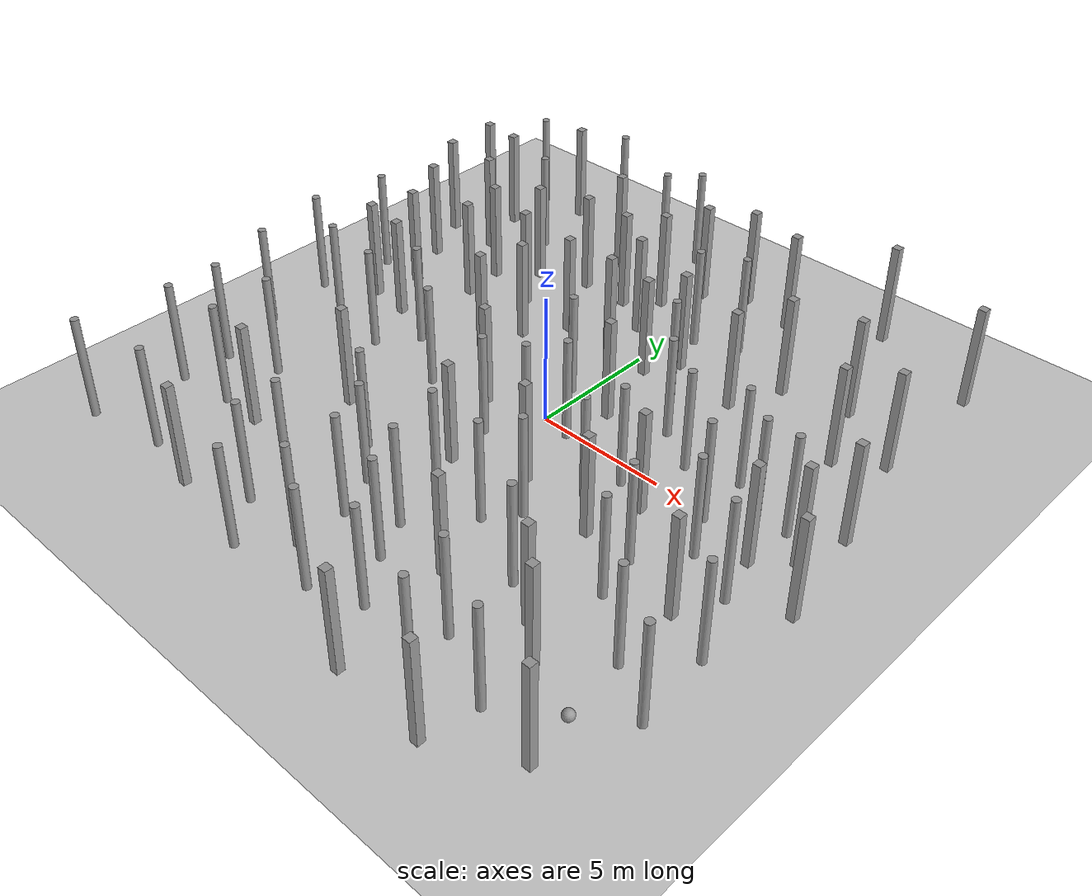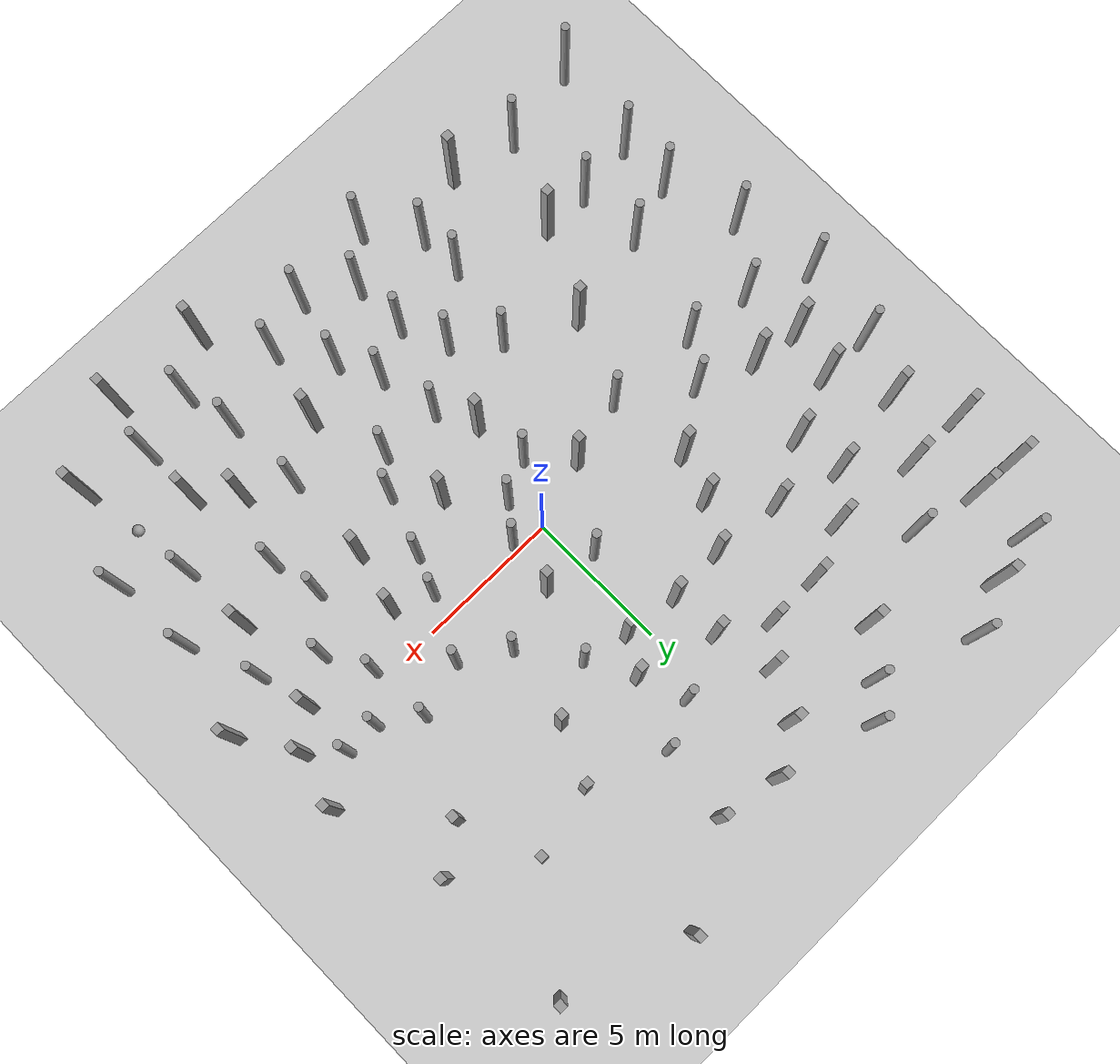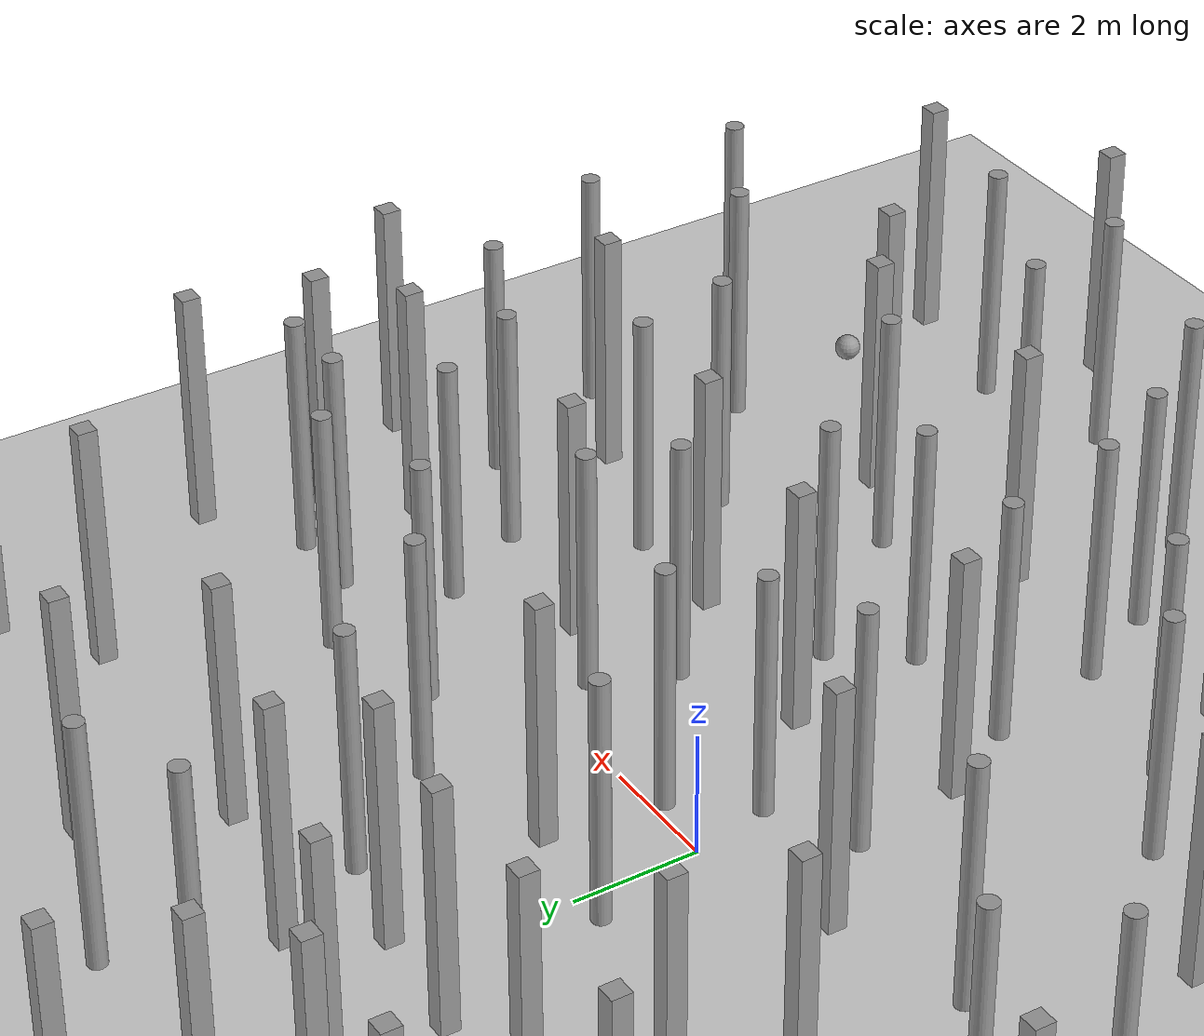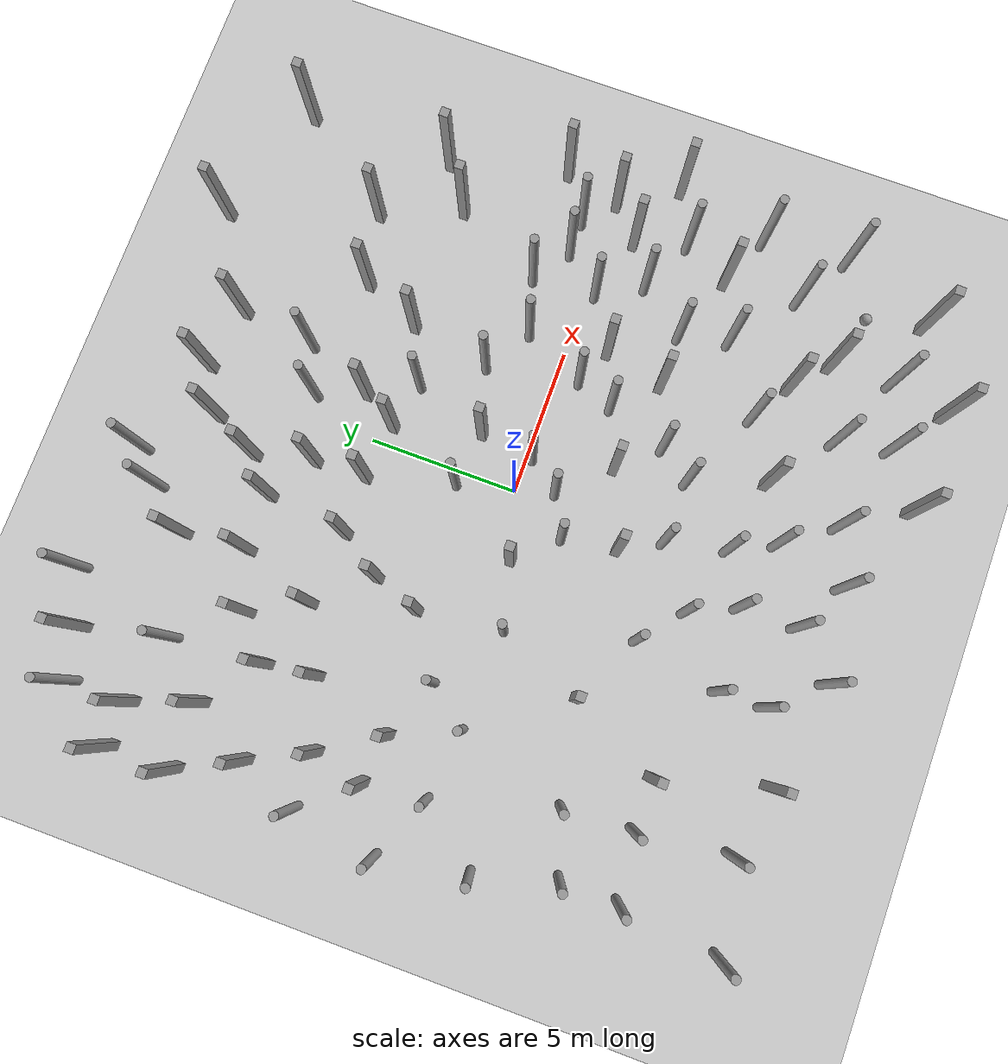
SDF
<sdf version="1.6">
 <world name="default">
  <light name="sun" type="directional">
   <pose>0 0 10 0 -0 0</pose>
   <diffuse>0.8 0.8 0.8 1</diffuse>
   <specular>0.2 0.2 0.2 1</specular>
   <attenuation>
    <range>1000</range>
    <constant>0.9</constant>
    <linear>0.01</linear>
    <quadratic>0.001</quadratic>
   </attenuation>
   <direction>-0.5 0.1 -0.9</direction>
  </light>
  <model name="ground_plane">
   <static>1</static>
   <link name="link">
    <collision name="collision">
     <geometry><plane><normal>0 0 1</normal><size>100 100</size></plane></geometry>
    </collision>
    <visual name="visual">
     <cast_shadows>0</cast_shadows>
     <geometry><plane><normal>0 0 1</normal><size>100 100</size></plane></geometry>
     <material>
      <script><uri>file://media/materials/scripts/gazebo.material</uri><name>Gazebo/Gray</name></script>
     </material>
    </visual>
   </link>
  </model>
  <gravity>0 0 -9.8</gravity>
  <magnetic_field>6e-06 2.3e-05 -4.2e-05</magnetic_field>
  <atmosphere type="adiabatic"/>
  <physics name="default_physics" default="0" type="ode">
   <max_step_size>0.002</max_step_size>
   <real_time_factor>1</real_time_factor>
   <real_time_update_rate>500</real_time_update_rate>
  </physics>
  <scene><ambient>0.4 0.4 0.4 1</ambient><background>0.7 0.7 0.7 1</background><shadows>1</shadows></scene>
  <spherical_coordinates>
   <surface_model>EARTH_WGS84</surface_model>
   <latitude_deg>0</latitude_deg>
   <longitude_deg>0</longitude_deg>
   <elevation>0</elevation>
   <heading_deg>0</heading_deg>
  </spherical_coordinates>
  <model name="unit_sphere">
   <link name="link">
    <inertial>
     <mass>1</mass>
     <inertia><ixx>0.1</ixx><ixy>0</ixy><ixz>0</ixz><iyy>0.1</iyy><iyz>0</iyz><izz>0.1</izz></inertia>
    </inertial>
    <gravity>0</gravity>
    <visual name="visual">
     <geometry><sphere><radius>0.203941</radius></sphere></geometry>
     <material>
      <script><name>Gazebo/Grey</name><uri>file://media/materials/scripts/gazebo.material</uri></script>
      <shader type="pixel"><normal_map>__default__</normal_map></shader>
     </material>
    </visual>
    <collision name="collision">
     <geometry><sphere><radius>0.203941</radius></sphere></geometry>
     <surface>
      <friction>
       <ode><mu>1</mu><mu2>1</mu2><fdir1>0 0 0</fdir1><slip1>0</slip1><slip2>0</slip2></ode>
       <torsional>
        <coefficient>1</coefficient>
        <patch_radius>0</patch_radius>
        <surface_radius>0</surface_radius>
        <use_patch_radius>1</use_patch_radius>
        <ode><slip>0</slip></ode>
       </torsional>
      </friction>
      <bounce><restitution_coefficient>0</restitution_coefficient><threshold>1e+06</threshold></bounce>
      <contact>
       <collide_without_contact>0</collide_without_contact>
       <collide_without_contact_bitmask>1</collide_without_contact_bitmask>
       <collide_bitmask>1</collide_bitmask>
       <ode>
        <soft_cfm>0</soft_cfm>
        <soft_erp>0.2</soft_erp>
        <kp>1e+13</kp>
        <kd>1</kd>
        <max_vel>0.01</max_vel>
        <min_depth>0</min_depth>
       </ode>
       <bullet>
        <split_impulse>1</split_impulse>
        <split_impulse_penetration_threshold>-0.01</split_impulse_penetration_threshold>
        <soft_cfm>0</soft_cfm>
        <soft_erp>0.2</soft_erp>
        <kp>1e+13</kp>
        <kd>1</kd>
       </bullet>
      </contact>
     </surface>
    </collision>
   </link>
   <static>0</static>
   <pose>9.54607 -9.14462 0.203941 0 -0 0</pose>
  </model>
  <audio><device>default</device></audio>
  <model name="unit_box">
   <link name="link">
    <inertial>
     <mass>1000</mass>
     <inertia><ixx>166.667</ixx><ixy>0</ixy><ixz>0</ixz><iyy>166.667</iyy><iyz>0</iyz><izz>166.667</izz></inertia>
    </inertial>
    <visual name="visual">
     <geometry><box><size>0.3 0.3 4</size></box></geometry>
     <material>
      <script><name>Gazebo/Grey</name><uri>file://media/materials/scripts/gazebo.material</uri></script>
      <shader type="vertex"><normal_map>__default__</normal_map></shader>
      <ambient>0.3 0.3 0.3 1</ambient>
      <diffuse>0.7 0.7 0.7 1</diffuse>
      <specular>0.01 0.01 0.01 1</specular>
      <emissive>0 0 0 1</emissive>
     </material>
    </visual>
    <collision name="collision">
     <geometry><box><size>0.3 0.3 4</size></box></geometry>
     <surface>
      <friction>
       <ode><mu>1</mu><mu2>1</mu2><fdir1>0 0 0</fdir1><slip1>0</slip1><slip2>0</slip2></ode>
       <torsional>
        <coefficient>1</coefficient>
        <patch_radius>0</patch_radius>
        <surface_radius>0</surface_radius>
        <use_patch_radius>1</use_patch_radius>
        <ode><slip>0</slip></ode>
       </torsional>
      </friction>
      <bounce><restitution_coefficient>0</restitution_coefficient><threshold>1e+06</threshold></bounce>
      <contact>
       <collide_without_contact>0</collide_without_contact>
       <collide_without_contact_bitmask>1</collide_without_contact_bitmask>
       <collide_bitmask>1</collide_bitmask>
       <ode>
        <soft_cfm>0</soft_cfm>
        <soft_erp>0.2</soft_erp>
        <kp>1e+13</kp>
        <kd>1</kd>
        <max_vel>0.01</max_vel>
        <min_depth>0</min_depth>
       </ode>
       <bullet>
        <split_impulse>1</split_impulse>
        <split_impulse_penetration_threshold>-0.01</split_impulse_penetration_threshold>
        <soft_cfm>0</soft_cfm>
        <soft_erp>0.2</soft_erp>
        <kp>1e+13</kp>
        <kd>1</kd>
       </bullet>
      </contact>
     </surface>
    </collision>
   </link>
   <static>0</static>
   <pose>-1.26727 4.71523 2 -1e-06 1e-06 -0.004556</pose>
  </model>
  <model name="unit_box_clone">
   <link name="link">
    <inertial>
     <mass>1000</mass>
     <inertia><ixx>166.667</ixx><ixy>0</ixy><ixz>0</ixz><iyy>166.667</iyy><iyz>0</iyz><izz>166.667</izz></inertia>
    </inertial>
    <visual name="visual">
     <geometry><box><size>0.3 0.3 4</size></box></geometry>
     <material>
      <script><name>Gazebo/Grey</name><uri>file://media/materials/scripts/gazebo.material</uri></script>
      <shader type="vertex"><normal_map>__default__</normal_map></shader>
      <ambient>0.3 0.3 0.3 1</ambient>
      <diffuse>0.7 0.7 0.7 1</diffuse>
      <specular>0.01 0.01 0.01 1</specular>
      <emissive>0 0 0 1</emissive>
     </material>
    </visual>
    <collision name="collision">
     <geometry><box><size>0.3 0.3 4</size></box></geometry>
     <surface>
      <friction>
       <ode><mu>1</mu><mu2>1</mu2><fdir1>0 0 0</fdir1><slip1>0</slip1><slip2>0</slip2></ode>
       <torsional>
        <coefficient>1</coefficient>
        <patch_radius>0</patch_radius>
        <surface_radius>0</surface_radius>
        <use_patch_radius>1</use_patch_radius>
        <ode><slip>0</slip></ode>
       </torsional>
      </friction>
      <bounce><restitution_coefficient>0</restitution_coefficient><threshold>1e+06</threshold></bounce>
      <contact>
       <collide_without_contact>0</collide_without_contact>
       <collide_without_contact_bitmask>1</collide_without_contact_bitmask>
       <collide_bitmask>1</collide_bitmask>
       <ode>
        <soft_cfm>0</soft_cfm>
        <soft_erp>0.2</soft_erp>
        <kp>1e+13</kp>
        <kd>1</kd>
        <max_vel>0.01</max_vel>
        <min_depth>0</min_depth>
       </ode>
       <bullet>
        <split_impulse>1</split_impulse>
        <split_impulse_penetration_threshold>-0.01</split_impulse_penetration_threshold>
        <soft_cfm>0</soft_cfm>
        <soft_erp>0.2</soft_erp>
        <kp>1e+13</kp>
        <kd>1</kd>
       </bullet>
      </contact>
     </surface>
    </collision>
   </link>
   <static>0</static>
   <pose>-2.25018 -0.681045 2 -9e-06 8e-06 -0.007469</pose>
  </model>
  <model name="unit_box_clone_1">
   <link name="link">
    <inertial>
     <mass>1000</mass>
     <inertia><ixx>166.667</ixx><ixy>0</ixy><ixz>0</ixz><iyy>166.667</iyy><iyz>0</iyz><izz>166.667</izz></inertia>
    </inertial>
    <visual name="visual">
     <geometry><box><size>0.3 0.3 4</size></box></geometry>
     <material>
      <script><name>Gazebo/Grey</name><uri>file://media/materials/scripts/gazebo.material</uri></script>
      <shader type="vertex"><normal_map>__default__</normal_map></shader>
      <ambient>0.3 0.3 0.3 1</ambient>
      <diffuse>0.7 0.7 0.7 1</diffuse>
      <specular>0.01 0.01 0.01 1</specular>
      <emissive>0 0 0 1</emissive>
     </material>
    </visual>
    <collision name="collision">
     <geometry><box><size>0.3 0.3 4</size></box></geometry>
     <surface>
      <friction>
       <ode><mu>1</mu><mu2>1</mu2><fdir1>0 0 0</fdir1><slip1>0</slip1><slip2>0</slip2></ode>
       <torsional>
        <coefficient>1</coefficient>
        <patch_radius>0</patch_radius>
        <surface_radius>0</surface_radius>
        <use_patch_radius>1</use_patch_radius>
        <ode><slip>0</slip></ode>
       </torsional>
      </friction>
      <bounce><restitution_coefficient>0</restitution_coefficient><threshold>1e+06</threshold></bounce>
      <contact>
       <collide_without_contact>0</collide_without_contact>
       <collide_without_contact_bitmask>1</collide_without_contact_bitmask>
       <collide_bitmask>1</collide_bitmask>
       <ode>
        <soft_cfm>0</soft_cfm>
        <soft_erp>0.2</soft_erp>
        <kp>1e+13</kp>
        <kd>1</kd>
        <max_vel>0.01</max_vel>
        <min_depth>0</min_depth>
       </ode>
       <bullet>
        <split_impulse>1</split_impulse>
        <split_impulse_penetration_threshold>-0.01</split_impulse_penetration_threshold>
        <soft_cfm>0</soft_cfm>
        <soft_erp>0.2</soft_erp>
        <kp>1e+13</kp>
        <kd>1</kd>
       </bullet>
      </contact>
     </surface>
    </collision>
   </link>
   <static>0</static>
   <pose>-2.89921 7.41397 2 1e-06 -1e-06 -0.001788</pose>
  </model>
  <model name="unit_box_clone_2">
   <link name="link">
    <inertial>
     <mass>1000</mass>
     <inertia><ixx>166.667</ixx><ixy>0</ixy><ixz>0</ixz><iyy>166.667</iyy><iyz>0</iyz><izz>166.667</izz></inertia>
    </inertial>
    <visual name="visual">
     <geometry><box><size>0.3 0.3 4</size></box></geometry>
     <material>
      <script><name>Gazebo/Grey</name><uri>file://media/materials/scripts/gazebo.material</uri></script>
      <shader type="vertex"><normal_map>__default__</normal_map></shader>
      <ambient>0.3 0.3 0.3 1</ambient>
      <diffuse>0.7 0.7 0.7 1</diffuse>
      <specular>0.01 0.01 0.01 1</specular>
      <emissive>0 0 0 1</emissive>
     </material>
    </visual>
    <collision name="collision">
     <geometry><box><size>0.3 0.3 4</size></box></geometry>
     <surface>
      <friction>
       <ode><mu>1</mu><mu2>1</mu2><fdir1>0 0 0</fdir1><slip1>0</slip1><slip2>0</slip2></ode>
       <torsional>
        <coefficient>1</coefficient>
        <patch_radius>0</patch_radius>
        <surface_radius>0</surface_radius>
        <use_patch_radius>1</use_patch_radius>
        <ode><slip>0</slip></ode>
       </torsional>
      </friction>
      <bounce><restitution_coefficient>0</restitution_coefficient><threshold>1e+06</threshold></bounce>
      <contact>
       <collide_without_contact>0</collide_without_contact>
       <collide_without_contact_bitmask>1</collide_without_contact_bitmask>
       <collide_bitmask>1</collide_bitmask>
       <ode>
        <soft_cfm>0</soft_cfm>
        <soft_erp>0.2</soft_erp>
        <kp>1e+13</kp>
        <kd>1</kd>
        <max_vel>0.01</max_vel>
        <min_depth>0</min_depth>
       </ode>
       <bullet>
        <split_impulse>1</split_impulse>
        <split_impulse_penetration_threshold>-0.01</split_impulse_penetration_threshold>
        <soft_cfm>0</soft_cfm>
        <soft_erp>0.2</soft_erp>
        <kp>1e+13</kp>
        <kd>1</kd>
       </bullet>
      </contact>
     </surface>
    </collision>
   </link>
   <static>0</static>
   <pose>4.92523 -3.34791 2 -1e-06 -7e-06 0.005354</pose>
  </model>
  <model name="unit_box_clone_3">
   <link name="link">
    <inertial>
     <mass>1000</mass>
     <inertia><ixx>166.667</ixx><ixy>0</ixy><ixz>0</ixz><iyy>166.667</iyy><iyz>0</iyz><izz>166.667</izz></inertia>
    </inertial>
    <visual name="visual">
     <geometry><box><size>0.3 0.3 4</size></box></geometry>
     <material>
      <script><name>Gazebo/Grey</name><uri>file://media/materials/scripts/gazebo.material</uri></script>
      <shader type="vertex"><normal_map>__default__</normal_map></shader>
      <ambient>0.3 0.3 0.3 1</ambient>
      <diffuse>0.7 0.7 0.7 1</diffuse>
      <specular>0.01 0.01 0.01 1</specular>
      <emissive>0 0 0 1</emissive>
     </material>
    </visual>
    <collision name="collision">
     <geometry><box><size>0.3 0.3 4</size></box></geometry>
     <surface>
      <friction>
       <ode><mu>1</mu><mu2>1</mu2><fdir1>0 0 0</fdir1><slip1>0</slip1><slip2>0</slip2></ode>
       <torsional>
        <coefficient>1</coefficient>
        <patch_radius>0</patch_radius>
        <surface_radius>0</surface_radius>
        <use_patch_radius>1</use_patch_radius>
        <ode><slip>0</slip></ode>
       </torsional>
      </friction>
      <bounce><restitution_coefficient>0</restitution_coefficient><threshold>1e+06</threshold></bounce>
      <contact>
       <collide_without_contact>0</collide_without_contact>
       <collide_without_contact_bitmask>1</collide_without_contact_bitmask>
       <collide_bitmask>1</collide_bitmask>
       <ode>
        <soft_cfm>0</soft_cfm>
        <soft_erp>0.2</soft_erp>
        <kp>1e+13</kp>
        <kd>1</kd>
        <max_vel>0.01</max_vel>
        <min_depth>0</min_depth>
       </ode>
       <bullet>
        <split_impulse>1</split_impulse>
        <split_impulse_penetration_threshold>-0.01</split_impulse_penetration_threshold>
        <soft_cfm>0</soft_cfm>
        <soft_erp>0.2</soft_erp>
        <kp>1e+13</kp>
        <kd>1</kd>
       </bullet>
      </contact>
     </surface>
    </collision>
   </link>
   <static>0</static>
   <pose>-9.81575 6.97351 2.00001 4.7e-05 5.2e-05 -0.001996</pose>
  </model>
  <model name="unit_box_clone_4">
   <link name="link">
    <inertial>
     <mass>1000</mass>
     <inertia><ixx>166.667</ixx><ixy>0</ixy><ixz>0</ixz><iyy>166.667</iyy><iyz>0</iyz><izz>166.667</izz></inertia>
    </inertial>
    <visual name="visual">
     <geometry><box><size>0.3 0.3 4</size></box></geometry>
     <material>
      <script><name>Gazebo/Grey</name><uri>file://media/materials/scripts/gazebo.material</uri></script>
      <shader type="vertex"><normal_map>__default__</normal_map></shader>
      <ambient>0.3 0.3 0.3 1</ambient>
      <diffuse>0.7 0.7 0.7 1</diffuse>
      <specular>0.01 0.01 0.01 1</specular>
      <emissive>0 0 0 1</emissive>
     </material>
    </visual>
    <collision name="collision">
     <geometry><box><size>0.3 0.3 4</size></box></geometry>
     <surface>
      <friction>
       <ode><mu>1</mu><mu2>1</mu2><fdir1>0 0 0</fdir1><slip1>0</slip1><slip2>0</slip2></ode>
       <torsional>
        <coefficient>1</coefficient>
        <patch_radius>0</patch_radius>
        <surface_radius>0</surface_radius>
        <use_patch_radius>1</use_patch_radius>
        <ode><slip>0</slip></ode>
       </torsional>
      </friction>
      <bounce><restitution_coefficient>0</restitution_coefficient><threshold>1e+06</threshold></bounce>
      <contact>
       <collide_without_contact>0</collide_without_contact>
       <collide_without_contact_bitmask>1</collide_without_contact_bitmask>
       <collide_bitmask>1</collide_bitmask>
       <ode>
        <soft_cfm>0</soft_cfm>
        <soft_erp>0.2</soft_erp>
        <kp>1e+13</kp>
        <kd>1</kd>
        <max_vel>0.01</max_vel>
        <min_depth>0</min_depth>
       </ode>
       <bullet>
        <split_impulse>1</split_impulse>
        <split_impulse_penetration_threshold>-0.01</split_impulse_penetration_threshold>
        <soft_cfm>0</soft_cfm>
        <soft_erp>0.2</soft_erp>
        <kp>1e+13</kp>
        <kd>1</kd>
       </bullet>
      </contact>
     </surface>
    </collision>
   </link>
   <static>0</static>
   <pose>-12.0641 9.20916 2.00001 -2e-06 -4.1e-05 -0.0015</pose>
  </model>
  <model name="unit_box_clone_6">
   <link name="link">
    <inertial>
     <mass>1000</mass>
     <inertia><ixx>166.667</ixx><ixy>0</ixy><ixz>0</ixz><iyy>166.667</iyy><iyz>0</iyz><izz>166.667</izz></inertia>
    </inertial>
    <visual name="visual">
     <geometry><box><size>0.3 0.3 4</size></box></geometry>
     <material>
      <script><name>Gazebo/Grey</name><uri>file://media/materials/scripts/gazebo.material</uri></script>
      <shader type="vertex"><normal_map>__default__</normal_map></shader>
      <ambient>0.3 0.3 0.3 1</ambient>
      <diffuse>0.7 0.7 0.7 1</diffuse>
      <specular>0.01 0.01 0.01 1</specular>
      <emissive>0 0 0 1</emissive>
     </material>
    </visual>
    <collision name="collision">
     <geometry><box><size>0.3 0.3 4</size></box></geometry>
     <surface>
      <friction>
       <ode><mu>1</mu><mu2>1</mu2><fdir1>0 0 0</fdir1><slip1>0</slip1><slip2>0</slip2></ode>
       <torsional>
        <coefficient>1</coefficient>
        <patch_radius>0</patch_radius>
        <surface_radius>0</surface_radius>
        <use_patch_radius>1</use_patch_radius>
        <ode><slip>0</slip></ode>
       </torsional>
      </friction>
      <bounce><restitution_coefficient>0</restitution_coefficient><threshold>1e+06</threshold></bounce>
      <contact>
       <collide_without_contact>0</collide_without_contact>
       <collide_without_contact_bitmask>1</collide_without_contact_bitmask>
       <collide_bitmask>1</collide_bitmask>
       <ode>
        <soft_cfm>0</soft_cfm>
        <soft_erp>0.2</soft_erp>
        <kp>1e+13</kp>
        <kd>1</kd>
        <max_vel>0.01</max_vel>
        <min_depth>0</min_depth>
       </ode>
       <bullet>
        <split_impulse>1</split_impulse>
        <split_impulse_penetration_threshold>-0.01</split_impulse_penetration_threshold>
        <soft_cfm>0</soft_cfm>
        <soft_erp>0.2</soft_erp>
        <kp>1e+13</kp>
        <kd>1</kd>
       </bullet>
      </contact>
     </surface>
    </collision>
   </link>
   <static>0</static>
   <pose>10.5124 0.091606 2 -3e-06 1e-05 -0.009171</pose>
  </model>
  <model name="unit_box_clone_7">
   <link name="link">
    <inertial>
     <mass>1000</mass>
     <inertia><ixx>166.667</ixx><ixy>0</ixy><ixz>0</ixz><iyy>166.667</iyy><iyz>0</iyz><izz>166.667</izz></inertia>
    </inertial>
    <visual name="visual">
     <geometry><box><size>0.3 0.3 4</size></box></geometry>
     <material>
      <script><name>Gazebo/Grey</name><uri>file://media/materials/scripts/gazebo.material</uri></script>
      <shader type="vertex"><normal_map>__default__</normal_map></shader>
      <ambient>0.3 0.3 0.3 1</ambient>
      <diffuse>0.7 0.7 0.7 1</diffuse>
      <specular>0.01 0.01 0.01 1</specular>
      <emissive>0 0 0 1</emissive>
     </material>
    </visual>
    <collision name="collision">
     <geometry><box><size>0.3 0.3 4</size></box></geometry>
     <surface>
      <friction>
       <ode><mu>1</mu><mu2>1</mu2><fdir1>0 0 0</fdir1><slip1>0</slip1><slip2>0</slip2></ode>
       <torsional>
        <coefficient>1</coefficient>
        <patch_radius>0</patch_radius>
        <surface_radius>0</surface_radius>
        <use_patch_radius>1</use_patch_radius>
        <ode><slip>0</slip></ode>
       </torsional>
      </friction>
      <bounce><restitution_coefficient>0</restitution_coefficient><threshold>1e+06</threshold></bounce>
      <contact>
       <collide_without_contact>0</collide_without_contact>
       <collide_without_contact_bitmask>1</collide_without_contact_bitmask>
       <collide_bitmask>1</collide_bitmask>
       <ode>
        <soft_cfm>0</soft_cfm>
        <soft_erp>0.2</soft_erp>
        <kp>1e+13</kp>
        <kd>1</kd>
        <max_vel>0.01</max_vel>
        <min_depth>0</min_depth>
       </ode>
       <bullet>
        <split_impulse>1</split_impulse>
        <split_impulse_penetration_threshold>-0.01</split_impulse_penetration_threshold>
        <soft_cfm>0</soft_cfm>
        <soft_erp>0.2</soft_erp>
        <kp>1e+13</kp>
        <kd>1</kd>
       </bullet>
      </contact>
     </surface>
    </collision>
   </link>
   <static>0</static>
   <pose>9.8605 -10.963 2 5e-06 -1.8e-05 -0.005667</pose>
  </model>
  <model name="unit_box_clone_8">
   <link name="link">
    <inertial>
     <mass>1000</mass>
     <inertia><ixx>166.667</ixx><ixy>0</ixy><ixz>0</ixz><iyy>166.667</iyy><iyz>0</iyz><izz>166.667</izz></inertia>
    </inertial>
    <visual name="visual">
     <geometry><box><size>0.3 0.3 4</size></box></geometry>
     <material>
      <script><name>Gazebo/Grey</name><uri>file://media/materials/scripts/gazebo.material</uri></script>
      <shader type="vertex"><normal_map>__default__</normal_map></shader>
      <ambient>0.3 0.3 0.3 1</ambient>
      <diffuse>0.7 0.7 0.7 1</diffuse>
      <specular>0.01 0.01 0.01 1</specular>
      <emissive>0 0 0 1</emissive>
     </material>
    </visual>
    <collision name="collision">
     <geometry><box><size>0.3 0.3 4</size></box></geometry>
     <surface>
      <friction>
       <ode><mu>1</mu><mu2>1</mu2><fdir1>0 0 0</fdir1><slip1>0</slip1><slip2>0</slip2></ode>
       <torsional>
        <coefficient>1</coefficient>
        <patch_radius>0</patch_radius>
        <surface_radius>0</surface_radius>
        <use_patch_radius>1</use_patch_radius>
        <ode><slip>0</slip></ode>
       </torsional>
      </friction>
      <bounce><restitution_coefficient>0</restitution_coefficient><threshold>1e+06</threshold></bounce>
      <contact>
       <collide_without_contact>0</collide_without_contact>
       <collide_without_contact_bitmask>1</collide_without_contact_bitmask>
       <collide_bitmask>1</collide_bitmask>
       <ode>
        <soft_cfm>0</soft_cfm>
        <soft_erp>0.2</soft_erp>
        <kp>1e+13</kp>
        <kd>1</kd>
        <max_vel>0.01</max_vel>
        <min_depth>0</min_depth>
       </ode>
       <bullet>
        <split_impulse>1</split_impulse>
        <split_impulse_penetration_threshold>-0.01</split_impulse_penetration_threshold>
        <soft_cfm>0</soft_cfm>
        <soft_erp>0.2</soft_erp>
        <kp>1e+13</kp>
        <kd>1</kd>
       </bullet>
      </contact>
     </surface>
    </collision>
   </link>
   <static>0</static>
   <pose>-6.68892 6.67579 2 -8e-06 -1.6e-05 -0.000352</pose>
  </model>
  <model name="unit_box_clone_9">
   <link name="link">
    <inertial>
     <mass>1000</mass>
     <inertia><ixx>166.667</ixx><ixy>0</ixy><ixz>0</ixz><iyy>166.667</iyy><iyz>0</iyz><izz>166.667</izz></inertia>
    </inertial>
    <visual name="visual">
     <geometry><box><size>0.3 0.3 4</size></box></geometry>
     <material>
      <script><name>Gazebo/Grey</name><uri>file://media/materials/scripts/gazebo.material</uri></script>
      <shader type="vertex"><normal_map>__default__</normal_map></shader>
      <ambient>0.3 0.3 0.3 1</ambient>
      <diffuse>0.7 0.7 0.7 1</diffuse>
      <specular>0.01 0.01 0.01 1</specular>
      <emissive>0 0 0 1</emissive>
     </material>
    </visual>
    <collision name="collision">
     <geometry><box><size>0.3 0.3 4</size></box></geometry>
     <surface>
      <friction>
       <ode><mu>1</mu><mu2>1</mu2><fdir1>0 0 0</fdir1><slip1>0</slip1><slip2>0</slip2></ode>
       <torsional>
        <coefficient>1</coefficient>
        <patch_radius>0</patch_radius>
        <surface_radius>0</surface_radius>
        <use_patch_radius>1</use_patch_radius>
        <ode><slip>0</slip></ode>
       </torsional>
      </friction>
      <bounce><restitution_coefficient>0</restitution_coefficient><threshold>1e+06</threshold></bounce>
      <contact>
       <collide_without_contact>0</collide_without_contact>
       <collide_without_contact_bitmask>1</collide_without_contact_bitmask>
       <collide_bitmask>1</collide_bitmask>
       <ode>
        <soft_cfm>0</soft_cfm>
        <soft_erp>0.2</soft_erp>
        <kp>1e+13</kp>
        <kd>1</kd>
        <max_vel>0.01</max_vel>
        <min_depth>0</min_depth>
       </ode>
       <bullet>
        <split_impulse>1</split_impulse>
        <split_impulse_penetration_threshold>-0.01</split_impulse_penetration_threshold>
        <soft_cfm>0</soft_cfm>
        <soft_erp>0.2</soft_erp>
        <kp>1e+13</kp>
        <kd>1</kd>
       </bullet>
      </contact>
     </surface>
    </collision>
   </link>
   <static>0</static>
   <pose>-8.00889 5.50015 2 0 -0 -0.003801</pose>
  </model>
  <model name="unit_box_clone_10">
   <link name="link">
    <inertial>
     <mass>1000</mass>
     <inertia><ixx>166.667</ixx><ixy>0</ixy><ixz>0</ixz><iyy>166.667</iyy><iyz>0</iyz><izz>166.667</izz></inertia>
    </inertial>
    <visual name="visual">
     <geometry><box><size>0.3 0.3 4</size></box></geometry>
     <material>
      <script><name>Gazebo/Grey</name><uri>file://media/materials/scripts/gazebo.material</uri></script>
      <shader type="vertex"><normal_map>__default__</normal_map></shader>
      <ambient>0.3 0.3 0.3 1</ambient>
      <diffuse>0.7 0.7 0.7 1</diffuse>
      <specular>0.01 0.01 0.01 1</specular>
      <emissive>0 0 0 1</emissive>
     </material>
    </visual>
    <collision name="collision">
     <geometry><box><size>0.3 0.3 4</size></box></geometry>
     <surface>
      <friction>
       <ode><mu>1</mu><mu2>1</mu2><fdir1>0 0 0</fdir1><slip1>0</slip1><slip2>0</slip2></ode>
       <torsional>
        <coefficient>1</coefficient>
        <patch_radius>0</patch_radius>
        <surface_radius>0</surface_radius>
        <use_patch_radius>1</use_patch_radius>
        <ode><slip>0</slip></ode>
       </torsional>
      </friction>
      <bounce><restitution_coefficient>0</restitution_coefficient><threshold>1e+06</threshold></bounce>
      <contact>
       <collide_without_contact>0</collide_without_contact>
       <collide_without_contact_bitmask>1</collide_without_contact_bitmask>
       <collide_bitmask>1</collide_bitmask>
       <ode>
        <soft_cfm>0</soft_cfm>
        <soft_erp>0.2</soft_erp>
        <kp>1e+13</kp>
        <kd>1</kd>
        <max_vel>0.01</max_vel>
        <min_depth>0</min_depth>
       </ode>
       <bullet>
        <split_impulse>1</split_impulse>
        <split_impulse_penetration_threshold>-0.01</split_impulse_penetration_threshold>
        <soft_cfm>0</soft_cfm>
        <soft_erp>0.2</soft_erp>
        <kp>1e+13</kp>
        <kd>1</kd>
       </bullet>
      </contact>
     </surface>
    </collision>
   </link>
   <static>0</static>
   <pose>-8.91735 11.4995 2 3e-06 1e-06 -0.003851</pose>
  </model>
  <model name="unit_box_clone_11">
   <link name="link">
    <inertial>
     <mass>1000</mass>
     <inertia><ixx>166.667</ixx><ixy>0</ixy><ixz>0</ixz><iyy>166.667</iyy><iyz>0</iyz><izz>166.667</izz></inertia>
    </inertial>
    <visual name="visual">
     <geometry><box><size>0.3 0.3 4</size></box></geometry>
     <material>
      <script><name>Gazebo/Grey</name><uri>file://media/materials/scripts/gazebo.material</uri></script>
      <shader type="vertex"><normal_map>__default__</normal_map></shader>
      <ambient>0.3 0.3 0.3 1</ambient>
      <diffuse>0.7 0.7 0.7 1</diffuse>
      <specular>0.01 0.01 0.01 1</specular>
      <emissive>0 0 0 1</emissive>
     </material>
    </visual>
    <collision name="collision">
     <geometry><box><size>0.3 0.3 4</size></box></geometry>
     <surface>
      <friction>
       <ode><mu>1</mu><mu2>1</mu2><fdir1>0 0 0</fdir1><slip1>0</slip1><slip2>0</slip2></ode>
       <torsional>
        <coefficient>1</coefficient>
        <patch_radius>0</patch_radius>
        <surface_radius>0</surface_radius>
        <use_patch_radius>1</use_patch_radius>
        <ode><slip>0</slip></ode>
       </torsional>
      </friction>
      <bounce><restitution_coefficient>0</restitution_coefficient><threshold>1e+06</threshold></bounce>
      <contact>
       <collide_without_contact>0</collide_without_contact>
       <collide_without_contact_bitmask>1</collide_without_contact_bitmask>
       <collide_bitmask>1</collide_bitmask>
       <ode>
        <soft_cfm>0</soft_cfm>
        <soft_erp>0.2</soft_erp>
        <kp>1e+13</kp>
        <kd>1</kd>
        <max_vel>0.01</max_vel>
        <min_depth>0</min_depth>
       </ode>
       <bullet>
        <split_impulse>1</split_impulse>
        <split_impulse_penetration_threshold>-0.01</split_impulse_penetration_threshold>
        <soft_cfm>0</soft_cfm>
        <soft_erp>0.2</soft_erp>
        <kp>1e+13</kp>
        <kd>1</kd>
       </bullet>
      </contact>
     </surface>
    </collision>
   </link>
   <static>0</static>
   <pose>-10.559 9.10965 2 0 5e-06 0.004017</pose>
  </model>
  <model name="unit_box_clone_13">
   <link name="link">
    <inertial>
     <mass>1000</mass>
     <inertia><ixx>166.667</ixx><ixy>0</ixy><ixz>0</ixz><iyy>166.667</iyy><iyz>0</iyz><izz>166.667</izz></inertia>
    </inertial>
    <visual name="visual">
     <geometry><box><size>0.3 0.3 4</size></box></geometry>
     <material>
      <script><name>Gazebo/Grey</name><uri>file://media/materials/scripts/gazebo.material</uri></script>
      <shader type="vertex"><normal_map>__default__</normal_map></shader>
      <ambient>0.3 0.3 0.3 1</ambient>
      <diffuse>0.7 0.7 0.7 1</diffuse>
      <specular>0.01 0.01 0.01 1</specular>
      <emissive>0 0 0 1</emissive>
     </material>
    </visual>
    <collision name="collision">
     <geometry><box><size>0.3 0.3 4</size></box></geometry>
     <surface>
      <friction>
       <ode><mu>1</mu><mu2>1</mu2><fdir1>0 0 0</fdir1><slip1>0</slip1><slip2>0</slip2></ode>
       <torsional>
        <coefficient>1</coefficient>
        <patch_radius>0</patch_radius>
        <surface_radius>0</surface_radius>
        <use_patch_radius>1</use_patch_radius>
        <ode><slip>0</slip></ode>
       </torsional>
      </friction>
      <bounce><restitution_coefficient>0</restitution_coefficient><threshold>1e+06</threshold></bounce>
      <contact>
       <collide_without_contact>0</collide_without_contact>
       <collide_without_contact_bitmask>1</collide_without_contact_bitmask>
       <collide_bitmask>1</collide_bitmask>
       <ode>
        <soft_cfm>0</soft_cfm>
        <soft_erp>0.2</soft_erp>
        <kp>1e+13</kp>
        <kd>1</kd>
        <max_vel>0.01</max_vel>
        <min_depth>0</min_depth>
       </ode>
       <bullet>
        <split_impulse>1</split_impulse>
        <split_impulse_penetration_threshold>-0.01</split_impulse_penetration_threshold>
        <soft_cfm>0</soft_cfm>
        <soft_erp>0.2</soft_erp>
        <kp>1e+13</kp>
        <kd>1</kd>
       </bullet>
      </contact>
     </surface>
    </collision>
   </link>
   <static>0</static>
   <pose>-10.0001 3.0001 2 -5e-06 5e-06 -0.001679</pose>
  </model>
  <model name="unit_box_clone_14">
   <link name="link">
    <inertial>
     <mass>1000</mass>
     <inertia><ixx>166.667</ixx><ixy>0</ixy><ixz>0</ixz><iyy>166.667</iyy><iyz>0</iyz><izz>166.667</izz></inertia>
    </inertial>
    <visual name="visual">
     <geometry><box><size>0.3 0.3 4</size></box></geometry>
     <material>
      <script><name>Gazebo/Grey</name><uri>file://media/materials/scripts/gazebo.material</uri></script>
      <shader type="vertex"><normal_map>__default__</normal_map></shader>
      <ambient>0.3 0.3 0.3 1</ambient>
      <diffuse>0.7 0.7 0.7 1</diffuse>
      <specular>0.01 0.01 0.01 1</specular>
      <emissive>0 0 0 1</emissive>
     </material>
    </visual>
    <collision name="collision">
     <geometry><box><size>0.3 0.3 4</size></box></geometry>
     <surface>
      <friction>
       <ode><mu>1</mu><mu2>1</mu2><fdir1>0 0 0</fdir1><slip1>0</slip1><slip2>0</slip2></ode>
       <torsional>
        <coefficient>1</coefficient>
        <patch_radius>0</patch_radius>
        <surface_radius>0</surface_radius>
        <use_patch_radius>1</use_patch_radius>
        <ode><slip>0</slip></ode>
       </torsional>
      </friction>
      <bounce><restitution_coefficient>0</restitution_coefficient><threshold>1e+06</threshold></bounce>
      <contact>
       <collide_without_contact>0</collide_without_contact>
       <collide_without_contact_bitmask>1</collide_without_contact_bitmask>
       <collide_bitmask>1</collide_bitmask>
       <ode>
        <soft_cfm>0</soft_cfm>
        <soft_erp>0.2</soft_erp>
        <kp>1e+13</kp>
        <kd>1</kd>
        <max_vel>0.01</max_vel>
        <min_depth>0</min_depth>
       </ode>
       <bullet>
        <split_impulse>1</split_impulse>
        <split_impulse_penetration_threshold>-0.01</split_impulse_penetration_threshold>
        <soft_cfm>0</soft_cfm>
        <soft_erp>0.2</soft_erp>
        <kp>1e+13</kp>
        <kd>1</kd>
       </bullet>
      </contact>
     </surface>
    </collision>
   </link>
   <static>0</static>
   <pose>-12 7.00014 2.00001 -1.8e-05 -3.9e-05 0.000878</pose>
  </model>
  <model name="unit_box_clone_15">
   <link name="link">
    <inertial>
     <mass>1000</mass>
     <inertia><ixx>166.667</ixx><ixy>0</ixy><ixz>0</ixz><iyy>166.667</iyy><iyz>0</iyz><izz>166.667</izz></inertia>
    </inertial>
    <visual name="visual">
     <geometry><box><size>0.3 0.3 4</size></box></geometry>
     <material>
      <script><name>Gazebo/Grey</name><uri>file://media/materials/scripts/gazebo.material</uri></script>
      <shader type="vertex"><normal_map>__default__</normal_map></shader>
      <ambient>0.3 0.3 0.3 1</ambient>
      <diffuse>0.7 0.7 0.7 1</diffuse>
      <specular>0.01 0.01 0.01 1</specular>
      <emissive>0 0 0 1</emissive>
     </material>
    </visual>
    <collision name="collision">
     <geometry><box><size>0.3 0.3 4</size></box></geometry>
     <surface>
      <friction>
       <ode><mu>1</mu><mu2>1</mu2><fdir1>0 0 0</fdir1><slip1>0</slip1><slip2>0</slip2></ode>
       <torsional>
        <coefficient>1</coefficient>
        <patch_radius>0</patch_radius>
        <surface_radius>0</surface_radius>
        <use_patch_radius>1</use_patch_radius>
        <ode><slip>0</slip></ode>
       </torsional>
      </friction>
      <bounce><restitution_coefficient>0</restitution_coefficient><threshold>1e+06</threshold></bounce>
      <contact>
       <collide_without_contact>0</collide_without_contact>
       <collide_without_contact_bitmask>1</collide_without_contact_bitmask>
       <collide_bitmask>1</collide_bitmask>
       <ode>
        <soft_cfm>0</soft_cfm>
        <soft_erp>0.2</soft_erp>
        <kp>1e+13</kp>
        <kd>1</kd>
        <max_vel>0.01</max_vel>
        <min_depth>0</min_depth>
       </ode>
       <bullet>
        <split_impulse>1</split_impulse>
        <split_impulse_penetration_threshold>-0.01</split_impulse_penetration_threshold>
        <soft_cfm>0</soft_cfm>
        <soft_erp>0.2</soft_erp>
        <kp>1e+13</kp>
        <kd>1</kd>
       </bullet>
      </contact>
     </surface>
    </collision>
   </link>
   <static>0</static>
   <pose>-8.74152 1.04876 2 -0 -1e-06 0.002214</pose>
  </model>
  <model name="unit_box_clone_16">
   <link name="link">
    <inertial>
     <mass>1000</mass>
     <inertia><ixx>166.667</ixx><ixy>0</ixy><ixz>0</ixz><iyy>166.667</iyy><iyz>0</iyz><izz>166.667</izz></inertia>
    </inertial>
    <visual name="visual">
     <geometry><box><size>0.3 0.3 4</size></box></geometry>
     <material>
      <script><name>Gazebo/Grey</name><uri>file://media/materials/scripts/gazebo.material</uri></script>
      <shader type="vertex"><normal_map>__default__</normal_map></shader>
      <ambient>0.3 0.3 0.3 1</ambient>
      <diffuse>0.7 0.7 0.7 1</diffuse>
      <specular>0.01 0.01 0.01 1</specular>
      <emissive>0 0 0 1</emissive>
     </material>
    </visual>
    <collision name="collision">
     <geometry><box><size>0.3 0.3 4</size></box></geometry>
     <surface>
      <friction>
       <ode><mu>1</mu><mu2>1</mu2><fdir1>0 0 0</fdir1><slip1>0</slip1><slip2>0</slip2></ode>
       <torsional>
        <coefficient>1</coefficient>
        <patch_radius>0</patch_radius>
        <surface_radius>0</surface_radius>
        <use_patch_radius>1</use_patch_radius>
        <ode><slip>0</slip></ode>
       </torsional>
      </friction>
      <bounce><restitution_coefficient>0</restitution_coefficient><threshold>1e+06</threshold></bounce>
      <contact>
       <collide_without_contact>0</collide_without_contact>
       <collide_without_contact_bitmask>1</collide_without_contact_bitmask>
       <collide_bitmask>1</collide_bitmask>
       <ode>
        <soft_cfm>0</soft_cfm>
        <soft_erp>0.2</soft_erp>
        <kp>1e+13</kp>
        <kd>1</kd>
        <max_vel>0.01</max_vel>
        <min_depth>0</min_depth>
       </ode>
       <bullet>
        <split_impulse>1</split_impulse>
        <split_impulse_penetration_threshold>-0.01</split_impulse_penetration_threshold>
        <soft_cfm>0</soft_cfm>
        <soft_erp>0.2</soft_erp>
        <kp>1e+13</kp>
        <kd>1</kd>
       </bullet>
      </contact>
     </surface>
    </collision>
   </link>
   <static>0</static>
   <pose>-11 5.00014 2.00001 -1.8e-05 -3.9e-05 0.000878</pose>
  </model>
  <model name="unit_box_clone_18">
   <link name="link">
    <inertial>
     <mass>1000</mass>
     <inertia><ixx>166.667</ixx><ixy>0</ixy><ixz>0</ixz><iyy>166.667</iyy><iyz>0</iyz><izz>166.667</izz></inertia>
    </inertial>
    <visual name="visual">
     <geometry><box><size>0.3 0.3 4</size></box></geometry>
     <material>
      <script><name>Gazebo/Grey</name><uri>file://media/materials/scripts/gazebo.material</uri></script>
      <shader type="vertex"><normal_map>__default__</normal_map></shader>
      <ambient>0.3 0.3 0.3 1</ambient>
      <diffuse>0.7 0.7 0.7 1</diffuse>
      <specular>0.01 0.01 0.01 1</specular>
      <emissive>0 0 0 1</emissive>
     </material>
    </visual>
    <collision name="collision">
     <geometry><box><size>0.3 0.3 4</size></box></geometry>
     <surface>
      <friction>
       <ode><mu>1</mu><mu2>1</mu2><fdir1>0 0 0</fdir1><slip1>0</slip1><slip2>0</slip2></ode>
       <torsional>
        <coefficient>1</coefficient>
        <patch_radius>0</patch_radius>
        <surface_radius>0</surface_radius>
        <use_patch_radius>1</use_patch_radius>
        <ode><slip>0</slip></ode>
       </torsional>
      </friction>
      <bounce><restitution_coefficient>0</restitution_coefficient><threshold>1e+06</threshold></bounce>
      <contact>
       <collide_without_contact>0</collide_without_contact>
       <collide_without_contact_bitmask>1</collide_without_contact_bitmask>
       <collide_bitmask>1</collide_bitmask>
       <ode>
        <soft_cfm>0</soft_cfm>
        <soft_erp>0.2</soft_erp>
        <kp>1e+13</kp>
        <kd>1</kd>
        <max_vel>0.01</max_vel>
        <min_depth>0</min_depth>
       </ode>
       <bullet>
        <split_impulse>1</split_impulse>
        <split_impulse_penetration_threshold>-0.01</split_impulse_penetration_threshold>
        <soft_cfm>0</soft_cfm>
        <soft_erp>0.2</soft_erp>
        <kp>1e+13</kp>
        <kd>1</kd>
       </bullet>
      </contact>
     </surface>
    </collision>
   </link>
   <static>0</static>
   <pose>-5.73006 4.87583 2 -1.4e-05 -1e-06 0.00022</pose>
  </model>
  <model name="unit_box_clone_19">
   <link name="link">
    <inertial>
     <mass>1000</mass>
     <inertia><ixx>166.667</ixx><ixy>0</ixy><ixz>0</ixz><iyy>166.667</iyy><iyz>0</iyz><izz>166.667</izz></inertia>
    </inertial>
    <visual name="visual">
     <geometry><box><size>0.3 0.3 4</size></box></geometry>
     <material>
      <script><name>Gazebo/Grey</name><uri>file://media/materials/scripts/gazebo.material</uri></script>
      <shader type="vertex"><normal_map>__default__</normal_map></shader>
      <ambient>0.3 0.3 0.3 1</ambient>
      <diffuse>0.7 0.7 0.7 1</diffuse>
      <specular>0.01 0.01 0.01 1</specular>
      <emissive>0 0 0 1</emissive>
     </material>
    </visual>
    <collision name="collision">
     <geometry><box><size>0.3 0.3 4</size></box></geometry>
     <surface>
      <friction>
       <ode><mu>1</mu><mu2>1</mu2><fdir1>0 0 0</fdir1><slip1>0</slip1><slip2>0</slip2></ode>
       <torsional>
        <coefficient>1</coefficient>
        <patch_radius>0</patch_radius>
        <surface_radius>0</surface_radius>
        <use_patch_radius>1</use_patch_radius>
        <ode><slip>0</slip></ode>
       </torsional>
      </friction>
      <bounce><restitution_coefficient>0</restitution_coefficient><threshold>1e+06</threshold></bounce>
      <contact>
       <collide_without_contact>0</collide_without_contact>
       <collide_without_contact_bitmask>1</collide_without_contact_bitmask>
       <collide_bitmask>1</collide_bitmask>
       <ode>
        <soft_cfm>0</soft_cfm>
        <soft_erp>0.2</soft_erp>
        <kp>1e+13</kp>
        <kd>1</kd>
        <max_vel>0.01</max_vel>
        <min_depth>0</min_depth>
       </ode>
       <bullet>
        <split_impulse>1</split_impulse>
        <split_impulse_penetration_threshold>-0.01</split_impulse_penetration_threshold>
        <soft_cfm>0</soft_cfm>
        <soft_erp>0.2</soft_erp>
        <kp>1e+13</kp>
        <kd>1</kd>
       </bullet>
      </contact>
     </surface>
    </collision>
   </link>
   <static>0</static>
   <pose>-1.32794 6.44932 2 -1e-06 1e-06 -0.004556</pose>
  </model>
  <model name="unit_box_clone_20">
   <link name="link">
    <inertial>
     <mass>1000</mass>
     <inertia><ixx>166.667</ixx><ixy>0</ixy><ixz>0</ixz><iyy>166.667</iyy><iyz>0</iyz><izz>166.667</izz></inertia>
    </inertial>
    <visual name="visual">
     <geometry><box><size>0.3 0.3 4</size></box></geometry>
     <material>
      <script><name>Gazebo/Grey</name><uri>file://media/materials/scripts/gazebo.material</uri></script>
      <shader type="vertex"><normal_map>__default__</normal_map></shader>
      <ambient>0.3 0.3 0.3 1</ambient>
      <diffuse>0.7 0.7 0.7 1</diffuse>
      <specular>0.01 0.01 0.01 1</specular>
      <emissive>0 0 0 1</emissive>
     </material>
    </visual>
    <collision name="collision">
     <geometry><box><size>0.3 0.3 4</size></box></geometry>
     <surface>
      <friction>
       <ode><mu>1</mu><mu2>1</mu2><fdir1>0 0 0</fdir1><slip1>0</slip1><slip2>0</slip2></ode>
       <torsional>
        <coefficient>1</coefficient>
        <patch_radius>0</patch_radius>
        <surface_radius>0</surface_radius>
        <use_patch_radius>1</use_patch_radius>
        <ode><slip>0</slip></ode>
       </torsional>
      </friction>
      <bounce><restitution_coefficient>0</restitution_coefficient><threshold>1e+06</threshold></bounce>
      <contact>
       <collide_without_contact>0</collide_without_contact>
       <collide_without_contact_bitmask>1</collide_without_contact_bitmask>
       <collide_bitmask>1</collide_bitmask>
       <ode>
        <soft_cfm>0</soft_cfm>
        <soft_erp>0.2</soft_erp>
        <kp>1e+13</kp>
        <kd>1</kd>
        <max_vel>0.01</max_vel>
        <min_depth>0</min_depth>
       </ode>
       <bullet>
        <split_impulse>1</split_impulse>
        <split_impulse_penetration_threshold>-0.01</split_impulse_penetration_threshold>
        <soft_cfm>0</soft_cfm>
        <soft_erp>0.2</soft_erp>
        <kp>1e+13</kp>
        <kd>1</kd>
       </bullet>
      </contact>
     </surface>
    </collision>
   </link>
   <static>0</static>
   <pose>0.641904 4.48442 2 -2e-06 -0 0.001535</pose>
  </model>
  <model name="unit_box_clone_21">
   <link name="link">
    <inertial>
     <mass>1000</mass>
     <inertia><ixx>166.667</ixx><ixy>0</ixy><ixz>0</ixz><iyy>166.667</iyy><iyz>0</iyz><izz>166.667</izz></inertia>
    </inertial>
    <visual name="visual">
     <geometry><box><size>0.3 0.3 4</size></box></geometry>
     <material>
      <script><name>Gazebo/Grey</name><uri>file://media/materials/scripts/gazebo.material</uri></script>
      <shader type="vertex"><normal_map>__default__</normal_map></shader>
      <ambient>0.3 0.3 0.3 1</ambient>
      <diffuse>0.7 0.7 0.7 1</diffuse>
      <specular>0.01 0.01 0.01 1</specular>
      <emissive>0 0 0 1</emissive>
     </material>
    </visual>
    <collision name="collision">
     <geometry><box><size>0.3 0.3 4</size></box></geometry>
     <surface>
      <friction>
       <ode><mu>1</mu><mu2>1</mu2><fdir1>0 0 0</fdir1><slip1>0</slip1><slip2>0</slip2></ode>
       <torsional>
        <coefficient>1</coefficient>
        <patch_radius>0</patch_radius>
        <surface_radius>0</surface_radius>
        <use_patch_radius>1</use_patch_radius>
        <ode><slip>0</slip></ode>
       </torsional>
      </friction>
      <bounce><restitution_coefficient>0</restitution_coefficient><threshold>1e+06</threshold></bounce>
      <contact>
       <collide_without_contact>0</collide_without_contact>
       <collide_without_contact_bitmask>1</collide_without_contact_bitmask>
       <collide_bitmask>1</collide_bitmask>
       <ode>
        <soft_cfm>0</soft_cfm>
        <soft_erp>0.2</soft_erp>
        <kp>1e+13</kp>
        <kd>1</kd>
        <max_vel>0.01</max_vel>
        <min_depth>0</min_depth>
       </ode>
       <bullet>
        <split_impulse>1</split_impulse>
        <split_impulse_penetration_threshold>-0.01</split_impulse_penetration_threshold>
        <soft_cfm>0</soft_cfm>
        <soft_erp>0.2</soft_erp>
        <kp>1e+13</kp>
        <kd>1</kd>
       </bullet>
      </contact>
     </surface>
    </collision>
   </link>
   <static>0</static>
   <pose>-1.80203 8.41594 2 9e-06 -1.3e-05 -0.006869</pose>
  </model>
  <model name="unit_box_clone_22">
   <link name="link">
    <inertial>
     <mass>1000</mass>
     <inertia><ixx>166.667</ixx><ixy>0</ixy><ixz>0</ixz><iyy>166.667</iyy><iyz>0</iyz><izz>166.667</izz></inertia>
    </inertial>
    <visual name="visual">
     <geometry><box><size>0.3 0.3 4</size></box></geometry>
     <material>
      <script><name>Gazebo/Grey</name><uri>file://media/materials/scripts/gazebo.material</uri></script>
      <shader type="vertex"><normal_map>__default__</normal_map></shader>
      <ambient>0.3 0.3 0.3 1</ambient>
      <diffuse>0.7 0.7 0.7 1</diffuse>
      <specular>0.01 0.01 0.01 1</specular>
      <emissive>0 0 0 1</emissive>
     </material>
    </visual>
    <collision name="collision">
     <geometry><box><size>0.3 0.3 4</size></box></geometry>
     <surface>
      <friction>
       <ode><mu>1</mu><mu2>1</mu2><fdir1>0 0 0</fdir1><slip1>0</slip1><slip2>0</slip2></ode>
       <torsional>
        <coefficient>1</coefficient>
        <patch_radius>0</patch_radius>
        <surface_radius>0</surface_radius>
        <use_patch_radius>1</use_patch_radius>
        <ode><slip>0</slip></ode>
       </torsional>
      </friction>
      <bounce><restitution_coefficient>0</restitution_coefficient><threshold>1e+06</threshold></bounce>
      <contact>
       <collide_without_contact>0</collide_without_contact>
       <collide_without_contact_bitmask>1</collide_without_contact_bitmask>
       <collide_bitmask>1</collide_bitmask>
       <ode>
        <soft_cfm>0</soft_cfm>
        <soft_erp>0.2</soft_erp>
        <kp>1e+13</kp>
        <kd>1</kd>
        <max_vel>0.01</max_vel>
        <min_depth>0</min_depth>
       </ode>
       <bullet>
        <split_impulse>1</split_impulse>
        <split_impulse_penetration_threshold>-0.01</split_impulse_penetration_threshold>
        <soft_cfm>0</soft_cfm>
        <soft_erp>0.2</soft_erp>
        <kp>1e+13</kp>
        <kd>1</kd>
       </bullet>
      </contact>
     </surface>
    </collision>
   </link>
   <static>0</static>
   <pose>-0.999863 9.99992 2 6e-06 2e-06 -0.013394</pose>
  </model>
  <model name="unit_box_clone_23">
   <link name="link">
    <inertial>
     <mass>1000</mass>
     <inertia><ixx>166.667</ixx><ixy>0</ixy><ixz>0</ixz><iyy>166.667</iyy><iyz>0</iyz><izz>166.667</izz></inertia>
    </inertial>
    <visual name="visual">
     <geometry><box><size>0.3 0.3 4</size></box></geometry>
     <material>
      <script><name>Gazebo/Grey</name><uri>file://media/materials/scripts/gazebo.material</uri></script>
      <shader type="vertex"><normal_map>__default__</normal_map></shader>
      <ambient>0.3 0.3 0.3 1</ambient>
      <diffuse>0.7 0.7 0.7 1</diffuse>
      <specular>0.01 0.01 0.01 1</specular>
      <emissive>0 0 0 1</emissive>
     </material>
    </visual>
    <collision name="collision">
     <geometry><box><size>0.3 0.3 4</size></box></geometry>
     <surface>
      <friction>
       <ode><mu>1</mu><mu2>1</mu2><fdir1>0 0 0</fdir1><slip1>0</slip1><slip2>0</slip2></ode>
       <torsional>
        <coefficient>1</coefficient>
        <patch_radius>0</patch_radius>
        <surface_radius>0</surface_radius>
        <use_patch_radius>1</use_patch_radius>
        <ode><slip>0</slip></ode>
       </torsional>
      </friction>
      <bounce><restitution_coefficient>0</restitution_coefficient><threshold>1e+06</threshold></bounce>
      <contact>
       <collide_without_contact>0</collide_without_contact>
       <collide_without_contact_bitmask>1</collide_without_contact_bitmask>
       <collide_bitmask>1</collide_bitmask>
       <ode>
        <soft_cfm>0</soft_cfm>
        <soft_erp>0.2</soft_erp>
        <kp>1e+13</kp>
        <kd>1</kd>
        <max_vel>0.01</max_vel>
        <min_depth>0</min_depth>
       </ode>
       <bullet>
        <split_impulse>1</split_impulse>
        <split_impulse_penetration_threshold>-0.01</split_impulse_penetration_threshold>
        <soft_cfm>0</soft_cfm>
        <soft_erp>0.2</soft_erp>
        <kp>1e+13</kp>
        <kd>1</kd>
       </bullet>
      </contact>
     </surface>
    </collision>
   </link>
   <static>0</static>
   <pose>-5.00227 9.59195 2 0 -2e-06 -0.002832</pose>
  </model>
  <model name="unit_box_clone_24">
   <link name="link">
    <inertial>
     <mass>1000</mass>
     <inertia><ixx>166.667</ixx><ixy>0</ixy><ixz>0</ixz><iyy>166.667</iyy><iyz>0</iyz><izz>166.667</izz></inertia>
    </inertial>
    <visual name="visual">
     <geometry><box><size>0.3 0.3 4</size></box></geometry>
     <material>
      <script><name>Gazebo/Grey</name><uri>file://media/materials/scripts/gazebo.material</uri></script>
      <shader type="vertex"><normal_map>__default__</normal_map></shader>
      <ambient>0.3 0.3 0.3 1</ambient>
      <diffuse>0.7 0.7 0.7 1</diffuse>
      <specular>0.01 0.01 0.01 1</specular>
      <emissive>0 0 0 1</emissive>
     </material>
    </visual>
    <collision name="collision">
     <geometry><box><size>0.3 0.3 4</size></box></geometry>
     <surface>
      <friction>
       <ode><mu>1</mu><mu2>1</mu2><fdir1>0 0 0</fdir1><slip1>0</slip1><slip2>0</slip2></ode>
       <torsional>
        <coefficient>1</coefficient>
        <patch_radius>0</patch_radius>
        <surface_radius>0</surface_radius>
        <use_patch_radius>1</use_patch_radius>
        <ode><slip>0</slip></ode>
       </torsional>
      </friction>
      <bounce><restitution_coefficient>0</restitution_coefficient><threshold>1e+06</threshold></bounce>
      <contact>
       <collide_without_contact>0</collide_without_contact>
       <collide_without_contact_bitmask>1</collide_without_contact_bitmask>
       <collide_bitmask>1</collide_bitmask>
       <ode>
        <soft_cfm>0</soft_cfm>
        <soft_erp>0.2</soft_erp>
        <kp>1e+13</kp>
        <kd>1</kd>
        <max_vel>0.01</max_vel>
        <min_depth>0</min_depth>
       </ode>
       <bullet>
        <split_impulse>1</split_impulse>
        <split_impulse_penetration_threshold>-0.01</split_impulse_penetration_threshold>
        <soft_cfm>0</soft_cfm>
        <soft_erp>0.2</soft_erp>
        <kp>1e+13</kp>
        <kd>1</kd>
       </bullet>
      </contact>
     </surface>
    </collision>
   </link>
   <static>0</static>
   <pose>-4.80948 7.40665 2 2e-06 -1.2e-05 0.001435</pose>
  </model>
  <model name="unit_box_clone_26">
   <link name="link">
    <inertial>
     <mass>1000</mass>
     <inertia><ixx>166.667</ixx><ixy>0</ixy><ixz>0</ixz><iyy>166.667</iyy><iyz>0</iyz><izz>166.667</izz></inertia>
    </inertial>
    <visual name="visual">
     <geometry><box><size>0.3 0.3 4</size></box></geometry>
     <material>
      <script><name>Gazebo/Grey</name><uri>file://media/materials/scripts/gazebo.material</uri></script>
      <shader type="vertex"><normal_map>__default__</normal_map></shader>
      <ambient>0.3 0.3 0.3 1</ambient>
      <diffuse>0.7 0.7 0.7 1</diffuse>
      <specular>0.01 0.01 0.01 1</specular>
      <emissive>0 0 0 1</emissive>
     </material>
    </visual>
    <collision name="collision">
     <geometry><box><size>0.3 0.3 4</size></box></geometry>
     <surface>
      <friction>
       <ode><mu>1</mu><mu2>1</mu2><fdir1>0 0 0</fdir1><slip1>0</slip1><slip2>0</slip2></ode>
       <torsional>
        <coefficient>1</coefficient>
        <patch_radius>0</patch_radius>
        <surface_radius>0</surface_radius>
        <use_patch_radius>1</use_patch_radius>
        <ode><slip>0</slip></ode>
       </torsional>
      </friction>
      <bounce><restitution_coefficient>0</restitution_coefficient><threshold>1e+06</threshold></bounce>
      <contact>
       <collide_without_contact>0</collide_without_contact>
       <collide_without_contact_bitmask>1</collide_without_contact_bitmask>
       <collide_bitmask>1</collide_bitmask>
       <ode>
        <soft_cfm>0</soft_cfm>
        <soft_erp>0.2</soft_erp>
        <kp>1e+13</kp>
        <kd>1</kd>
        <max_vel>0.01</max_vel>
        <min_depth>0</min_depth>
       </ode>
       <bullet>
        <split_impulse>1</split_impulse>
        <split_impulse_penetration_threshold>-0.01</split_impulse_penetration_threshold>
        <soft_cfm>0</soft_cfm>
        <soft_erp>0.2</soft_erp>
        <kp>1e+13</kp>
        <kd>1</kd>
       </bullet>
      </contact>
     </surface>
    </collision>
   </link>
   <static>0</static>
   <pose>-3.24166 4.64156 2.00001 1e-06 -8.5e-05 -0.004088</pose>
  </model>
  <model name="unit_box_clone_27">
   <link name="link">
    <inertial>
     <mass>1000</mass>
     <inertia><ixx>166.667</ixx><ixy>0</ixy><ixz>0</ixz><iyy>166.667</iyy><iyz>0</iyz><izz>166.667</izz></inertia>
    </inertial>
    <visual name="visual">
     <geometry><box><size>0.3 0.3 4</size></box></geometry>
     <material>
      <script><name>Gazebo/Grey</name><uri>file://media/materials/scripts/gazebo.material</uri></script>
      <shader type="vertex"><normal_map>__default__</normal_map></shader>
      <ambient>0.3 0.3 0.3 1</ambient>
      <diffuse>0.7 0.7 0.7 1</diffuse>
      <specular>0.01 0.01 0.01 1</specular>
      <emissive>0 0 0 1</emissive>
     </material>
    </visual>
    <collision name="collision">
     <geometry><box><size>0.3 0.3 4</size></box></geometry>
     <surface>
      <friction>
       <ode><mu>1</mu><mu2>1</mu2><fdir1>0 0 0</fdir1><slip1>0</slip1><slip2>0</slip2></ode>
       <torsional>
        <coefficient>1</coefficient>
        <patch_radius>0</patch_radius>
        <surface_radius>0</surface_radius>
        <use_patch_radius>1</use_patch_radius>
        <ode><slip>0</slip></ode>
       </torsional>
      </friction>
      <bounce><restitution_coefficient>0</restitution_coefficient><threshold>1e+06</threshold></bounce>
      <contact>
       <collide_without_contact>0</collide_without_contact>
       <collide_without_contact_bitmask>1</collide_without_contact_bitmask>
       <collide_bitmask>1</collide_bitmask>
       <ode>
        <soft_cfm>0</soft_cfm>
        <soft_erp>0.2</soft_erp>
        <kp>1e+13</kp>
        <kd>1</kd>
        <max_vel>0.01</max_vel>
        <min_depth>0</min_depth>
       </ode>
       <bullet>
        <split_impulse>1</split_impulse>
        <split_impulse_penetration_threshold>-0.01</split_impulse_penetration_threshold>
        <soft_cfm>0</soft_cfm>
        <soft_erp>0.2</soft_erp>
        <kp>1e+13</kp>
        <kd>1</kd>
       </bullet>
      </contact>
     </surface>
    </collision>
   </link>
   <static>0</static>
   <pose>-4.80577 1.58862 2 5e-06 1e-05 0.006274</pose>
  </model>
  <model name="unit_box_clone_28">
   <link name="link">
    <inertial>
     <mass>1000</mass>
     <inertia><ixx>166.667</ixx><ixy>0</ixy><ixz>0</ixz><iyy>166.667</iyy><iyz>0</iyz><izz>166.667</izz></inertia>
    </inertial>
    <visual name="visual">
     <geometry><box><size>0.3 0.3 4</size></box></geometry>
     <material>
      <script><name>Gazebo/Grey</name><uri>file://media/materials/scripts/gazebo.material</uri></script>
      <shader type="vertex"><normal_map>__default__</normal_map></shader>
      <ambient>0.3 0.3 0.3 1</ambient>
      <diffuse>0.7 0.7 0.7 1</diffuse>
      <specular>0.01 0.01 0.01 1</specular>
      <emissive>0 0 0 1</emissive>
     </material>
    </visual>
    <collision name="collision">
     <geometry><box><size>0.3 0.3 4</size></box></geometry>
     <surface>
      <friction>
       <ode><mu>1</mu><mu2>1</mu2><fdir1>0 0 0</fdir1><slip1>0</slip1><slip2>0</slip2></ode>
       <torsional>
        <coefficient>1</coefficient>
        <patch_radius>0</patch_radius>
        <surface_radius>0</surface_radius>
        <use_patch_radius>1</use_patch_radius>
        <ode><slip>0</slip></ode>
       </torsional>
      </friction>
      <bounce><restitution_coefficient>0</restitution_coefficient><threshold>1e+06</threshold></bounce>
      <contact>
       <collide_without_contact>0</collide_without_contact>
       <collide_without_contact_bitmask>1</collide_without_contact_bitmask>
       <collide_bitmask>1</collide_bitmask>
       <ode>
        <soft_cfm>0</soft_cfm>
        <soft_erp>0.2</soft_erp>
        <kp>1e+13</kp>
        <kd>1</kd>
        <max_vel>0.01</max_vel>
        <min_depth>0</min_depth>
       </ode>
       <bullet>
        <split_impulse>1</split_impulse>
        <split_impulse_penetration_threshold>-0.01</split_impulse_penetration_threshold>
        <soft_cfm>0</soft_cfm>
        <soft_erp>0.2</soft_erp>
        <kp>1e+13</kp>
        <kd>1</kd>
       </bullet>
      </contact>
     </surface>
    </collision>
   </link>
   <static>0</static>
   <pose>-7.80117 3.82478 2 1e-06 7e-06 -0.005516</pose>
  </model>
  <model name="unit_cylinder">
   <link name="link">
    <inertial>
     <mass>1000</mass>
     <inertia><ixx>145.833</ixx><ixy>0</ixy><ixz>0</ixz><iyy>145.833</iyy><iyz>0</iyz><izz>125</izz></inertia>
    </inertial>
    <visual name="visual">
     <geometry><cylinder><radius>0.15</radius><length>4</length></cylinder></geometry>
     <material>
      <script><name>Gazebo/Grey</name><uri>file://media/materials/scripts/gazebo.material</uri></script>
      <shader type="vertex"><normal_map>__default__</normal_map></shader>
      <ambient>0.3 0.3 0.3 1</ambient>
      <diffuse>0.7 0.7 0.7 1</diffuse>
      <specular>0.01 0.01 0.01 1</specular>
      <emissive>0 0 0 1</emissive>
     </material>
    </visual>
    <collision name="collision">
     <geometry><cylinder><radius>0.15</radius><length>4</length></cylinder></geometry>
     <surface>
      <friction>
       <ode><mu>1</mu><mu2>1</mu2><fdir1>0 0 0</fdir1><slip1>0</slip1><slip2>0</slip2></ode>
       <torsional>
        <coefficient>1</coefficient>
        <patch_radius>0</patch_radius>
        <surface_radius>0</surface_radius>
        <use_patch_radius>1</use_patch_radius>
        <ode><slip>0</slip></ode>
       </torsional>
      </friction>
      <bounce><restitution_coefficient>0</restitution_coefficient><threshold>1e+06</threshold></bounce>
      <contact>
       <collide_without_contact>0</collide_without_contact>
       <collide_without_contact_bitmask>1</collide_without_contact_bitmask>
       <collide_bitmask>1</collide_bitmask>
       <ode>
        <soft_cfm>0</soft_cfm>
        <soft_erp>0.2</soft_erp>
        <kp>1e+13</kp>
        <kd>1</kd>
        <max_vel>0.01</max_vel>
        <min_depth>0</min_depth>
       </ode>
       <bullet>
        <split_impulse>1</split_impulse>
        <split_impulse_penetration_threshold>-0.01</split_impulse_penetration_threshold>
        <soft_cfm>0</soft_cfm>
        <soft_erp>0.2</soft_erp>
        <kp>1e+13</kp>
        <kd>1</kd>
       </bullet>
      </contact>
     </surface>
    </collision>
   </link>
   <static>0</static>
   <pose>3.557 2.30203 1.99998 -1e-06 1e-06 -0.168337</pose>
  </model>
  <model name="unit_cylinder_clone_0">
   <link name="link">
    <inertial>
     <mass>1000</mass>
     <inertia><ixx>145.833</ixx><ixy>0</ixy><ixz>0</ixz><iyy>145.833</iyy><iyz>0</iyz><izz>125</izz></inertia>
    </inertial>
    <visual name="visual">
     <geometry><cylinder><radius>0.15</radius><length>4</length></cylinder></geometry>
     <material>
      <script><name>Gazebo/Grey</name><uri>file://media/materials/scripts/gazebo.material</uri></script>
      <shader type="vertex"><normal_map>__default__</normal_map></shader>
      <ambient>0.3 0.3 0.3 1</ambient>
      <diffuse>0.7 0.7 0.7 1</diffuse>
      <specular>0.01 0.01 0.01 1</specular>
      <emissive>0 0 0 1</emissive>
     </material>
    </visual>
    <collision name="collision">
     <geometry><cylinder><radius>0.15</radius><length>4</length></cylinder></geometry>
     <surface>
      <friction>
       <ode><mu>1</mu><mu2>1</mu2><fdir1>0 0 0</fdir1><slip1>0</slip1><slip2>0</slip2></ode>
       <torsional>
        <coefficient>1</coefficient>
        <patch_radius>0</patch_radius>
        <surface_radius>0</surface_radius>
        <use_patch_radius>1</use_patch_radius>
        <ode><slip>0</slip></ode>
       </torsional>
      </friction>
      <bounce><restitution_coefficient>0</restitution_coefficient><threshold>1e+06</threshold></bounce>
      <contact>
       <collide_without_contact>0</collide_without_contact>
       <collide_without_contact_bitmask>1</collide_without_contact_bitmask>
       <collide_bitmask>1</collide_bitmask>
       <ode>
        <soft_cfm>0</soft_cfm>
        <soft_erp>0.2</soft_erp>
        <kp>1e+13</kp>
        <kd>1</kd>
        <max_vel>0.01</max_vel>
        <min_depth>0</min_depth>
       </ode>
       <bullet>
        <split_impulse>1</split_impulse>
        <split_impulse_penetration_threshold>-0.01</split_impulse_penetration_threshold>
        <soft_cfm>0</soft_cfm>
        <soft_erp>0.2</soft_erp>
        <kp>1e+13</kp>
        <kd>1</kd>
       </bullet>
      </contact>
     </surface>
    </collision>
   </link>
   <static>0</static>
   <pose>6.72153 -3.36401 1.99998 -1e-06 1e-06 -0.161446</pose>
  </model>
  <model name="unit_cylinder_clone_1">
   <link name="link">
    <inertial>
     <mass>1000</mass>
     <inertia><ixx>145.833</ixx><ixy>0</ixy><ixz>0</ixz><iyy>145.833</iyy><iyz>0</iyz><izz>125</izz></inertia>
    </inertial>
    <visual name="visual">
     <geometry><cylinder><radius>0.15</radius><length>4</length></cylinder></geometry>
     <material>
      <script><name>Gazebo/Grey</name><uri>file://media/materials/scripts/gazebo.material</uri></script>
      <shader type="vertex"><normal_map>__default__</normal_map></shader>
      <ambient>0.3 0.3 0.3 1</ambient>
      <diffuse>0.7 0.7 0.7 1</diffuse>
      <specular>0.01 0.01 0.01 1</specular>
      <emissive>0 0 0 1</emissive>
     </material>
    </visual>
    <collision name="collision">
     <geometry><cylinder><radius>0.15</radius><length>4</length></cylinder></geometry>
     <surface>
      <friction>
       <ode><mu>1</mu><mu2>1</mu2><fdir1>0 0 0</fdir1><slip1>0</slip1><slip2>0</slip2></ode>
       <torsional>
        <coefficient>1</coefficient>
        <patch_radius>0</patch_radius>
        <surface_radius>0</surface_radius>
        <use_patch_radius>1</use_patch_radius>
        <ode><slip>0</slip></ode>
       </torsional>
      </friction>
      <bounce><restitution_coefficient>0</restitution_coefficient><threshold>1e+06</threshold></bounce>
      <contact>
       <collide_without_contact>0</collide_without_contact>
       <collide_without_contact_bitmask>1</collide_without_contact_bitmask>
       <collide_bitmask>1</collide_bitmask>
       <ode>
        <soft_cfm>0</soft_cfm>
        <soft_erp>0.2</soft_erp>
        <kp>1e+13</kp>
        <kd>1</kd>
        <max_vel>0.01</max_vel>
        <min_depth>0</min_depth>
       </ode>
       <bullet>
        <split_impulse>1</split_impulse>
        <split_impulse_penetration_threshold>-0.01</split_impulse_penetration_threshold>
        <soft_cfm>0</soft_cfm>
        <soft_erp>0.2</soft_erp>
        <kp>1e+13</kp>
        <kd>1</kd>
       </bullet>
      </contact>
     </surface>
    </collision>
   </link>
   <static>0</static>
   <pose>2.06797 -5.17657 1.99998 -2e-06 -0 -0.149269</pose>
  </model>
  <model name="unit_cylinder_clone_2">
   <link name="link">
    <inertial>
     <mass>1000</mass>
     <inertia><ixx>145.833</ixx><ixy>0</ixy><ixz>0</ixz><iyy>145.833</iyy><iyz>0</iyz><izz>125</izz></inertia>
    </inertial>
    <visual name="visual">
     <geometry><cylinder><radius>0.15</radius><length>4</length></cylinder></geometry>
     <material>
      <script><name>Gazebo/Grey</name><uri>file://media/materials/scripts/gazebo.material</uri></script>
      <shader type="vertex"><normal_map>__default__</normal_map></shader>
      <ambient>0.3 0.3 0.3 1</ambient>
      <diffuse>0.7 0.7 0.7 1</diffuse>
      <specular>0.01 0.01 0.01 1</specular>
      <emissive>0 0 0 1</emissive>
     </material>
    </visual>
    <collision name="collision">
     <geometry><cylinder><radius>0.15</radius><length>4</length></cylinder></geometry>
     <surface>
      <friction>
       <ode><mu>1</mu><mu2>1</mu2><fdir1>0 0 0</fdir1><slip1>0</slip1><slip2>0</slip2></ode>
       <torsional>
        <coefficient>1</coefficient>
        <patch_radius>0</patch_radius>
        <surface_radius>0</surface_radius>
        <use_patch_radius>1</use_patch_radius>
        <ode><slip>0</slip></ode>
       </torsional>
      </friction>
      <bounce><restitution_coefficient>0</restitution_coefficient><threshold>1e+06</threshold></bounce>
      <contact>
       <collide_without_contact>0</collide_without_contact>
       <collide_without_contact_bitmask>1</collide_without_contact_bitmask>
       <collide_bitmask>1</collide_bitmask>
       <ode>
        <soft_cfm>0</soft_cfm>
        <soft_erp>0.2</soft_erp>
        <kp>1e+13</kp>
        <kd>1</kd>
        <max_vel>0.01</max_vel>
        <min_depth>0</min_depth>
       </ode>
       <bullet>
        <split_impulse>1</split_impulse>
        <split_impulse_penetration_threshold>-0.01</split_impulse_penetration_threshold>
        <soft_cfm>0</soft_cfm>
        <soft_erp>0.2</soft_erp>
        <kp>1e+13</kp>
        <kd>1</kd>
       </bullet>
      </contact>
     </surface>
    </collision>
   </link>
   <static>0</static>
   <pose>4.97545 -9.30368 1.99998 -2e-06 -0 -0.167694</pose>
  </model>
  <model name="unit_cylinder_clone_3">
   <link name="link">
    <inertial>
     <mass>1000</mass>
     <inertia><ixx>145.833</ixx><ixy>0</ixy><ixz>0</ixz><iyy>145.833</iyy><iyz>0</iyz><izz>125</izz></inertia>
    </inertial>
    <visual name="visual">
     <geometry><cylinder><radius>0.15</radius><length>4</length></cylinder></geometry>
     <material>
      <script><name>Gazebo/Grey</name><uri>file://media/materials/scripts/gazebo.material</uri></script>
      <shader type="vertex"><normal_map>__default__</normal_map></shader>
      <ambient>0.3 0.3 0.3 1</ambient>
      <diffuse>0.7 0.7 0.7 1</diffuse>
      <specular>0.01 0.01 0.01 1</specular>
      <emissive>0 0 0 1</emissive>
     </material>
    </visual>
    <collision name="collision">
     <geometry><cylinder><radius>0.15</radius><length>4</length></cylinder></geometry>
     <surface>
      <friction>
       <ode><mu>1</mu><mu2>1</mu2><fdir1>0 0 0</fdir1><slip1>0</slip1><slip2>0</slip2></ode>
       <torsional>
        <coefficient>1</coefficient>
        <patch_radius>0</patch_radius>
        <surface_radius>0</surface_radius>
        <use_patch_radius>1</use_patch_radius>
        <ode><slip>0</slip></ode>
       </torsional>
      </friction>
      <bounce><restitution_coefficient>0</restitution_coefficient><threshold>1e+06</threshold></bounce>
      <contact>
       <collide_without_contact>0</collide_without_contact>
       <collide_without_contact_bitmask>1</collide_without_contact_bitmask>
       <collide_bitmask>1</collide_bitmask>
       <ode>
        <soft_cfm>0</soft_cfm>
        <soft_erp>0.2</soft_erp>
        <kp>1e+13</kp>
        <kd>1</kd>
        <max_vel>0.01</max_vel>
        <min_depth>0</min_depth>
       </ode>
       <bullet>
        <split_impulse>1</split_impulse>
        <split_impulse_penetration_threshold>-0.01</split_impulse_penetration_threshold>
        <soft_cfm>0</soft_cfm>
        <soft_erp>0.2</soft_erp>
        <kp>1e+13</kp>
        <kd>1</kd>
       </bullet>
      </contact>
     </surface>
    </collision>
   </link>
   <static>0</static>
   <pose>0.763384 7.25593 1.99998 -2e-06 1e-06 -0.167033</pose>
  </model>
  <model name="unit_cylinder_clone_0_clone">
   <link name="link">
    <inertial>
     <mass>1000</mass>
     <inertia><ixx>145.833</ixx><ixy>0</ixy><ixz>0</ixz><iyy>145.833</iyy><iyz>0</iyz><izz>125</izz></inertia>
    </inertial>
    <visual name="visual">
     <geometry><cylinder><radius>0.15</radius><length>4</length></cylinder></geometry>
     <material>
      <script><name>Gazebo/Grey</name><uri>file://media/materials/scripts/gazebo.material</uri></script>
      <shader type="vertex"><normal_map>__default__</normal_map></shader>
      <ambient>0.3 0.3 0.3 1</ambient>
      <diffuse>0.7 0.7 0.7 1</diffuse>
      <specular>0.01 0.01 0.01 1</specular>
      <emissive>0 0 0 1</emissive>
     </material>
    </visual>
    <collision name="collision">
     <geometry><cylinder><radius>0.15</radius><length>4</length></cylinder></geometry>
     <surface>
      <friction>
       <ode><mu>1</mu><mu2>1</mu2><fdir1>0 0 0</fdir1><slip1>0</slip1><slip2>0</slip2></ode>
       <torsional>
        <coefficient>1</coefficient>
        <patch_radius>0</patch_radius>
        <surface_radius>0</surface_radius>
        <use_patch_radius>1</use_patch_radius>
        <ode><slip>0</slip></ode>
       </torsional>
      </friction>
      <bounce><restitution_coefficient>0</restitution_coefficient><threshold>1e+06</threshold></bounce>
      <contact>
       <collide_without_contact>0</collide_without_contact>
       <collide_without_contact_bitmask>1</collide_without_contact_bitmask>
       <collide_bitmask>1</collide_bitmask>
       <ode>
        <soft_cfm>0</soft_cfm>
        <soft_erp>0.2</soft_erp>
        <kp>1e+13</kp>
        <kd>1</kd>
        <max_vel>0.01</max_vel>
        <min_depth>0</min_depth>
       </ode>
       <bullet>
        <split_impulse>1</split_impulse>
        <split_impulse_penetration_threshold>-0.01</split_impulse_penetration_threshold>
        <soft_cfm>0</soft_cfm>
        <soft_erp>0.2</soft_erp>
        <kp>1e+13</kp>
        <kd>1</kd>
       </bullet>
      </contact>
     </surface>
    </collision>
   </link>
   <static>0</static>
   <pose>10.8478 -4.98998 1.99998 -1e-06 1e-06 -0.145154</pose>
  </model>
  <model name="unit_cylinder_clone_4">
   <link name="link">
    <inertial>
     <mass>1000</mass>
     <inertia><ixx>145.833</ixx><ixy>0</ixy><ixz>0</ixz><iyy>145.833</iyy><iyz>0</iyz><izz>125</izz></inertia>
    </inertial>
    <visual name="visual">
     <geometry><cylinder><radius>0.15</radius><length>4</length></cylinder></geometry>
     <material>
      <script><name>Gazebo/Grey</name><uri>file://media/materials/scripts/gazebo.material</uri></script>
      <shader type="vertex"><normal_map>__default__</normal_map></shader>
      <ambient>0.3 0.3 0.3 1</ambient>
      <diffuse>0.7 0.7 0.7 1</diffuse>
      <specular>0.01 0.01 0.01 1</specular>
      <emissive>0 0 0 1</emissive>
     </material>
    </visual>
    <collision name="collision">
     <geometry><cylinder><radius>0.15</radius><length>4</length></cylinder></geometry>
     <surface>
      <friction>
       <ode><mu>1</mu><mu2>1</mu2><fdir1>0 0 0</fdir1><slip1>0</slip1><slip2>0</slip2></ode>
       <torsional>
        <coefficient>1</coefficient>
        <patch_radius>0</patch_radius>
        <surface_radius>0</surface_radius>
        <use_patch_radius>1</use_patch_radius>
        <ode><slip>0</slip></ode>
       </torsional>
      </friction>
      <bounce><restitution_coefficient>0</restitution_coefficient><threshold>1e+06</threshold></bounce>
      <contact>
       <collide_without_contact>0</collide_without_contact>
       <collide_without_contact_bitmask>1</collide_without_contact_bitmask>
       <collide_bitmask>1</collide_bitmask>
       <ode>
        <soft_cfm>0</soft_cfm>
        <soft_erp>0.2</soft_erp>
        <kp>1e+13</kp>
        <kd>1</kd>
        <max_vel>0.01</max_vel>
        <min_depth>0</min_depth>
       </ode>
       <bullet>
        <split_impulse>1</split_impulse>
        <split_impulse_penetration_threshold>-0.01</split_impulse_penetration_threshold>
        <soft_cfm>0</soft_cfm>
        <soft_erp>0.2</soft_erp>
        <kp>1e+13</kp>
        <kd>1</kd>
       </bullet>
      </contact>
     </surface>
    </collision>
   </link>
   <static>0</static>
   <pose>5.12504 1.32728 1.99998 -1e-06 1e-06 -0.163617</pose>
  </model>
  <model name="unit_cylinder_clone_1_clone">
   <link name="link">
    <inertial>
     <mass>1000</mass>
     <inertia><ixx>145.833</ixx><ixy>0</ixy><ixz>0</ixz><iyy>145.833</iyy><iyz>0</iyz><izz>125</izz></inertia>
    </inertial>
    <visual name="visual">
     <geometry><cylinder><radius>0.15</radius><length>4</length></cylinder></geometry>
     <material>
      <script><name>Gazebo/Grey</name><uri>file://media/materials/scripts/gazebo.material</uri></script>
      <shader type="vertex"><normal_map>__default__</normal_map></shader>
      <ambient>0.3 0.3 0.3 1</ambient>
      <diffuse>0.7 0.7 0.7 1</diffuse>
      <specular>0.01 0.01 0.01 1</specular>
      <emissive>0 0 0 1</emissive>
     </material>
    </visual>
    <collision name="collision">
     <geometry><cylinder><radius>0.15</radius><length>4</length></cylinder></geometry>
     <surface>
      <friction>
       <ode><mu>1</mu><mu2>1</mu2><fdir1>0 0 0</fdir1><slip1>0</slip1><slip2>0</slip2></ode>
       <torsional>
        <coefficient>1</coefficient>
        <patch_radius>0</patch_radius>
        <surface_radius>0</surface_radius>
        <use_patch_radius>1</use_patch_radius>
        <ode><slip>0</slip></ode>
       </torsional>
      </friction>
      <bounce><restitution_coefficient>0</restitution_coefficient><threshold>1e+06</threshold></bounce>
      <contact>
       <collide_without_contact>0</collide_without_contact>
       <collide_without_contact_bitmask>1</collide_without_contact_bitmask>
       <collide_bitmask>1</collide_bitmask>
       <ode>
        <soft_cfm>0</soft_cfm>
        <soft_erp>0.2</soft_erp>
        <kp>1e+13</kp>
        <kd>1</kd>
        <max_vel>0.01</max_vel>
        <min_depth>0</min_depth>
       </ode>
       <bullet>
        <split_impulse>1</split_impulse>
        <split_impulse_penetration_threshold>-0.01</split_impulse_penetration_threshold>
        <soft_cfm>0</soft_cfm>
        <soft_erp>0.2</soft_erp>
        <kp>1e+13</kp>
        <kd>1</kd>
       </bullet>
      </contact>
     </surface>
    </collision>
   </link>
   <static>0</static>
   <pose>-1.25133 -8.0211 1.99995 -0.000273 3e-06 -0.782921</pose>
  </model>
  <model name="unit_cylinder_clone_1_clone_1">
   <link name="link">
    <inertial>
     <mass>1000</mass>
     <inertia><ixx>145.833</ixx><ixy>0</ixy><ixz>0</ixz><iyy>145.833</iyy><iyz>0</iyz><izz>125</izz></inertia>
    </inertial>
    <visual name="visual">
     <geometry><cylinder><radius>0.15</radius><length>4</length></cylinder></geometry>
     <material>
      <script><name>Gazebo/Grey</name><uri>file://media/materials/scripts/gazebo.material</uri></script>
      <shader type="vertex"><normal_map>__default__</normal_map></shader>
      <ambient>0.3 0.3 0.3 1</ambient>
      <diffuse>0.7 0.7 0.7 1</diffuse>
      <specular>0.01 0.01 0.01 1</specular>
      <emissive>0 0 0 1</emissive>
     </material>
    </visual>
    <collision name="collision">
     <geometry><cylinder><radius>0.15</radius><length>4</length></cylinder></geometry>
     <surface>
      <friction>
       <ode><mu>1</mu><mu2>1</mu2><fdir1>0 0 0</fdir1><slip1>0</slip1><slip2>0</slip2></ode>
       <torsional>
        <coefficient>1</coefficient>
        <patch_radius>0</patch_radius>
        <surface_radius>0</surface_radius>
        <use_patch_radius>1</use_patch_radius>
        <ode><slip>0</slip></ode>
       </torsional>
      </friction>
      <bounce><restitution_coefficient>0</restitution_coefficient><threshold>1e+06</threshold></bounce>
      <contact>
       <collide_without_contact>0</collide_without_contact>
       <collide_without_contact_bitmask>1</collide_without_contact_bitmask>
       <collide_bitmask>1</collide_bitmask>
       <ode>
        <soft_cfm>0</soft_cfm>
        <soft_erp>0.2</soft_erp>
        <kp>1e+13</kp>
        <kd>1</kd>
        <max_vel>0.01</max_vel>
        <min_depth>0</min_depth>
       </ode>
       <bullet>
        <split_impulse>1</split_impulse>
        <split_impulse_penetration_threshold>-0.01</split_impulse_penetration_threshold>
        <soft_cfm>0</soft_cfm>
        <soft_erp>0.2</soft_erp>
        <kp>1e+13</kp>
        <kd>1</kd>
       </bullet>
      </contact>
     </surface>
    </collision>
   </link>
   <static>0</static>
   <pose>-11.8278 -2.81611 1.99995 -0.000273 1e-06 -0.789222</pose>
  </model>
  <model name="unit_cylinder_clone_1_clone_3">
   <link name="link">
    <inertial>
     <mass>1000</mass>
     <inertia><ixx>145.833</ixx><ixy>0</ixy><ixz>0</ixz><iyy>145.833</iyy><iyz>0</iyz><izz>125</izz></inertia>
    </inertial>
    <visual name="visual">
     <geometry><cylinder><radius>0.15</radius><length>4</length></cylinder></geometry>
     <material>
      <script><name>Gazebo/Grey</name><uri>file://media/materials/scripts/gazebo.material</uri></script>
      <shader type="vertex"><normal_map>__default__</normal_map></shader>
      <ambient>0.3 0.3 0.3 1</ambient>
      <diffuse>0.7 0.7 0.7 1</diffuse>
      <specular>0.01 0.01 0.01 1</specular>
      <emissive>0 0 0 1</emissive>
     </material>
    </visual>
    <collision name="collision">
     <geometry><cylinder><radius>0.15</radius><length>4</length></cylinder></geometry>
     <surface>
      <friction>
       <ode><mu>1</mu><mu2>1</mu2><fdir1>0 0 0</fdir1><slip1>0</slip1><slip2>0</slip2></ode>
       <torsional>
        <coefficient>1</coefficient>
        <patch_radius>0</patch_radius>
        <surface_radius>0</surface_radius>
        <use_patch_radius>1</use_patch_radius>
        <ode><slip>0</slip></ode>
       </torsional>
      </friction>
      <bounce><restitution_coefficient>0</restitution_coefficient><threshold>1e+06</threshold></bounce>
      <contact>
       <collide_without_contact>0</collide_without_contact>
       <collide_without_contact_bitmask>1</collide_without_contact_bitmask>
       <collide_bitmask>1</collide_bitmask>
       <ode>
        <soft_cfm>0</soft_cfm>
        <soft_erp>0.2</soft_erp>
        <kp>1e+13</kp>
        <kd>1</kd>
        <max_vel>0.01</max_vel>
        <min_depth>0</min_depth>
       </ode>
       <bullet>
        <split_impulse>1</split_impulse>
        <split_impulse_penetration_threshold>-0.01</split_impulse_penetration_threshold>
        <soft_cfm>0</soft_cfm>
        <soft_erp>0.2</soft_erp>
        <kp>1e+13</kp>
        <kd>1</kd>
       </bullet>
      </contact>
     </surface>
    </collision>
   </link>
   <static>0</static>
   <pose>-7.82327 -1.09345 1.99998 -1e-06 -1e-06 -0.52827</pose>
  </model>
  <model name="unit_cylinder_clone_1_clone_4">
   <link name="link">
    <inertial>
     <mass>1000</mass>
     <inertia><ixx>145.833</ixx><ixy>0</ixy><ixz>0</ixz><iyy>145.833</iyy><iyz>0</iyz><izz>125</izz></inertia>
    </inertial>
    <visual name="visual">
     <geometry><cylinder><radius>0.15</radius><length>4</length></cylinder></geometry>
     <material>
      <script><name>Gazebo/Grey</name><uri>file://media/materials/scripts/gazebo.material</uri></script>
      <shader type="vertex"><normal_map>__default__</normal_map></shader>
      <ambient>0.3 0.3 0.3 1</ambient>
      <diffuse>0.7 0.7 0.7 1</diffuse>
      <specular>0.01 0.01 0.01 1</specular>
      <emissive>0 0 0 1</emissive>
     </material>
    </visual>
    <collision name="collision">
     <geometry><cylinder><radius>0.15</radius><length>4</length></cylinder></geometry>
     <surface>
      <friction>
       <ode><mu>1</mu><mu2>1</mu2><fdir1>0 0 0</fdir1><slip1>0</slip1><slip2>0</slip2></ode>
       <torsional>
        <coefficient>1</coefficient>
        <patch_radius>0</patch_radius>
        <surface_radius>0</surface_radius>
        <use_patch_radius>1</use_patch_radius>
        <ode><slip>0</slip></ode>
       </torsional>
      </friction>
      <bounce><restitution_coefficient>0</restitution_coefficient><threshold>1e+06</threshold></bounce>
      <contact>
       <collide_without_contact>0</collide_without_contact>
       <collide_without_contact_bitmask>1</collide_without_contact_bitmask>
       <collide_bitmask>1</collide_bitmask>
       <ode>
        <soft_cfm>0</soft_cfm>
        <soft_erp>0.2</soft_erp>
        <kp>1e+13</kp>
        <kd>1</kd>
        <max_vel>0.01</max_vel>
        <min_depth>0</min_depth>
       </ode>
       <bullet>
        <split_impulse>1</split_impulse>
        <split_impulse_penetration_threshold>-0.01</split_impulse_penetration_threshold>
        <soft_cfm>0</soft_cfm>
        <soft_erp>0.2</soft_erp>
        <kp>1e+13</kp>
        <kd>1</kd>
       </bullet>
      </contact>
     </surface>
    </collision>
   </link>
   <static>0</static>
   <pose>-8.98337 -4.76712 1.99995 -0.000273 1e-06 -0.791185</pose>
  </model>
  <model name="unit_cylinder_clone_1_clone_6">
   <link name="link">
    <inertial>
     <mass>1000</mass>
     <inertia><ixx>145.833</ixx><ixy>0</ixy><ixz>0</ixz><iyy>145.833</iyy><iyz>0</iyz><izz>125</izz></inertia>
    </inertial>
    <visual name="visual">
     <geometry><cylinder><radius>0.15</radius><length>4</length></cylinder></geometry>
     <material>
      <script><name>Gazebo/Grey</name><uri>file://media/materials/scripts/gazebo.material</uri></script>
      <shader type="vertex"><normal_map>__default__</normal_map></shader>
      <ambient>0.3 0.3 0.3 1</ambient>
      <diffuse>0.7 0.7 0.7 1</diffuse>
      <specular>0.01 0.01 0.01 1</specular>
      <emissive>0 0 0 1</emissive>
     </material>
    </visual>
    <collision name="collision">
     <geometry><cylinder><radius>0.15</radius><length>4</length></cylinder></geometry>
     <surface>
      <friction>
       <ode><mu>1</mu><mu2>1</mu2><fdir1>0 0 0</fdir1><slip1>0</slip1><slip2>0</slip2></ode>
       <torsional>
        <coefficient>1</coefficient>
        <patch_radius>0</patch_radius>
        <surface_radius>0</surface_radius>
        <use_patch_radius>1</use_patch_radius>
        <ode><slip>0</slip></ode>
       </torsional>
      </friction>
      <bounce><restitution_coefficient>0</restitution_coefficient><threshold>1e+06</threshold></bounce>
      <contact>
       <collide_without_contact>0</collide_without_contact>
       <collide_without_contact_bitmask>1</collide_without_contact_bitmask>
       <collide_bitmask>1</collide_bitmask>
       <ode>
        <soft_cfm>0</soft_cfm>
        <soft_erp>0.2</soft_erp>
        <kp>1e+13</kp>
        <kd>1</kd>
        <max_vel>0.01</max_vel>
        <min_depth>0</min_depth>
       </ode>
       <bullet>
        <split_impulse>1</split_impulse>
        <split_impulse_penetration_threshold>-0.01</split_impulse_penetration_threshold>
        <soft_cfm>0</soft_cfm>
        <soft_erp>0.2</soft_erp>
        <kp>1e+13</kp>
        <kd>1</kd>
       </bullet>
      </contact>
     </surface>
    </collision>
   </link>
   <static>0</static>
   <pose>-3.34529 -5.28367 1.99998 -1e-06 -0 -0.187092</pose>
  </model>
  <model name="unit_cylinder_clone_1_clone_7">
   <link name="link">
    <inertial>
     <mass>1000</mass>
     <inertia><ixx>145.833</ixx><ixy>0</ixy><ixz>0</ixz><iyy>145.833</iyy><iyz>0</iyz><izz>125</izz></inertia>
    </inertial>
    <visual name="visual">
     <geometry><cylinder><radius>0.15</radius><length>4</length></cylinder></geometry>
     <material>
      <script><name>Gazebo/Grey</name><uri>file://media/materials/scripts/gazebo.material</uri></script>
      <shader type="vertex"><normal_map>__default__</normal_map></shader>
      <ambient>0.3 0.3 0.3 1</ambient>
      <diffuse>0.7 0.7 0.7 1</diffuse>
      <specular>0.01 0.01 0.01 1</specular>
      <emissive>0 0 0 1</emissive>
     </material>
    </visual>
    <collision name="collision">
     <geometry><cylinder><radius>0.15</radius><length>4</length></cylinder></geometry>
     <surface>
      <friction>
       <ode><mu>1</mu><mu2>1</mu2><fdir1>0 0 0</fdir1><slip1>0</slip1><slip2>0</slip2></ode>
       <torsional>
        <coefficient>1</coefficient>
        <patch_radius>0</patch_radius>
        <surface_radius>0</surface_radius>
        <use_patch_radius>1</use_patch_radius>
        <ode><slip>0</slip></ode>
       </torsional>
      </friction>
      <bounce><restitution_coefficient>0</restitution_coefficient><threshold>1e+06</threshold></bounce>
      <contact>
       <collide_without_contact>0</collide_without_contact>
       <collide_without_contact_bitmask>1</collide_without_contact_bitmask>
       <collide_bitmask>1</collide_bitmask>
       <ode>
        <soft_cfm>0</soft_cfm>
        <soft_erp>0.2</soft_erp>
        <kp>1e+13</kp>
        <kd>1</kd>
        <max_vel>0.01</max_vel>
        <min_depth>0</min_depth>
       </ode>
       <bullet>
        <split_impulse>1</split_impulse>
        <split_impulse_penetration_threshold>-0.01</split_impulse_penetration_threshold>
        <soft_cfm>0</soft_cfm>
        <soft_erp>0.2</soft_erp>
        <kp>1e+13</kp>
        <kd>1</kd>
       </bullet>
      </contact>
     </surface>
    </collision>
   </link>
   <static>0</static>
   <pose>7.98254 -1.76181 1.99995 -0.000273 3e-06 -0.784345</pose>
  </model>
  <model name="unit_cylinder_clone_1_clone_8">
   <link name="link">
    <inertial>
     <mass>1000</mass>
     <inertia><ixx>145.833</ixx><ixy>0</ixy><ixz>0</ixz><iyy>145.833</iyy><iyz>0</iyz><izz>125</izz></inertia>
    </inertial>
    <visual name="visual">
     <geometry><cylinder><radius>0.15</radius><length>4</length></cylinder></geometry>
     <material>
      <script><name>Gazebo/Grey</name><uri>file://media/materials/scripts/gazebo.material</uri></script>
      <shader type="vertex"><normal_map>__default__</normal_map></shader>
      <ambient>0.3 0.3 0.3 1</ambient>
      <diffuse>0.7 0.7 0.7 1</diffuse>
      <specular>0.01 0.01 0.01 1</specular>
      <emissive>0 0 0 1</emissive>
     </material>
    </visual>
    <collision name="collision">
     <geometry><cylinder><radius>0.15</radius><length>4</length></cylinder></geometry>
     <surface>
      <friction>
       <ode><mu>1</mu><mu2>1</mu2><fdir1>0 0 0</fdir1><slip1>0</slip1><slip2>0</slip2></ode>
       <torsional>
        <coefficient>1</coefficient>
        <patch_radius>0</patch_radius>
        <surface_radius>0</surface_radius>
        <use_patch_radius>1</use_patch_radius>
        <ode><slip>0</slip></ode>
       </torsional>
      </friction>
      <bounce><restitution_coefficient>0</restitution_coefficient><threshold>1e+06</threshold></bounce>
      <contact>
       <collide_without_contact>0</collide_without_contact>
       <collide_without_contact_bitmask>1</collide_without_contact_bitmask>
       <collide_bitmask>1</collide_bitmask>
       <ode>
        <soft_cfm>0</soft_cfm>
        <soft_erp>0.2</soft_erp>
        <kp>1e+13</kp>
        <kd>1</kd>
        <max_vel>0.01</max_vel>
        <min_depth>0</min_depth>
       </ode>
       <bullet>
        <split_impulse>1</split_impulse>
        <split_impulse_penetration_threshold>-0.01</split_impulse_penetration_threshold>
        <soft_cfm>0</soft_cfm>
        <soft_erp>0.2</soft_erp>
        <kp>1e+13</kp>
        <kd>1</kd>
       </bullet>
      </contact>
     </surface>
    </collision>
   </link>
   <static>0</static>
   <pose>0.294782 -1.28433 1.99995 -0.000273 3e-06 -0.784263</pose>
  </model>
  <model name="unit_cylinder_clone_1_clone_9">
   <link name="link">
    <inertial>
     <mass>1000</mass>
     <inertia><ixx>145.833</ixx><ixy>0</ixy><ixz>0</ixz><iyy>145.833</iyy><iyz>0</iyz><izz>125</izz></inertia>
    </inertial>
    <visual name="visual">
     <geometry><cylinder><radius>0.15</radius><length>4</length></cylinder></geometry>
     <material>
      <script><name>Gazebo/Grey</name><uri>file://media/materials/scripts/gazebo.material</uri></script>
      <shader type="vertex"><normal_map>__default__</normal_map></shader>
      <ambient>0.3 0.3 0.3 1</ambient>
      <diffuse>0.7 0.7 0.7 1</diffuse>
      <specular>0.01 0.01 0.01 1</specular>
      <emissive>0 0 0 1</emissive>
     </material>
    </visual>
    <collision name="collision">
     <geometry><cylinder><radius>0.15</radius><length>4</length></cylinder></geometry>
     <surface>
      <friction>
       <ode><mu>1</mu><mu2>1</mu2><fdir1>0 0 0</fdir1><slip1>0</slip1><slip2>0</slip2></ode>
       <torsional>
        <coefficient>1</coefficient>
        <patch_radius>0</patch_radius>
        <surface_radius>0</surface_radius>
        <use_patch_radius>1</use_patch_radius>
        <ode><slip>0</slip></ode>
       </torsional>
      </friction>
      <bounce><restitution_coefficient>0</restitution_coefficient><threshold>1e+06</threshold></bounce>
      <contact>
       <collide_without_contact>0</collide_without_contact>
       <collide_without_contact_bitmask>1</collide_without_contact_bitmask>
       <collide_bitmask>1</collide_bitmask>
       <ode>
        <soft_cfm>0</soft_cfm>
        <soft_erp>0.2</soft_erp>
        <kp>1e+13</kp>
        <kd>1</kd>
        <max_vel>0.01</max_vel>
        <min_depth>0</min_depth>
       </ode>
       <bullet>
        <split_impulse>1</split_impulse>
        <split_impulse_penetration_threshold>-0.01</split_impulse_penetration_threshold>
        <soft_cfm>0</soft_cfm>
        <soft_erp>0.2</soft_erp>
        <kp>1e+13</kp>
        <kd>1</kd>
       </bullet>
      </contact>
     </surface>
    </collision>
   </link>
   <static>0</static>
   <pose>11.0914 -7.86932 1.99995 -0.000273 2e-06 -0.785122</pose>
  </model>
  <model name="unit_cylinder_clone_1_clone_10">
   <link name="link">
    <inertial>
     <mass>1000</mass>
     <inertia><ixx>145.833</ixx><ixy>0</ixy><ixz>0</ixz><iyy>145.833</iyy><iyz>0</iyz><izz>125</izz></inertia>
    </inertial>
    <visual name="visual">
     <geometry><cylinder><radius>0.15</radius><length>4</length></cylinder></geometry>
     <material>
      <script><name>Gazebo/Grey</name><uri>file://media/materials/scripts/gazebo.material</uri></script>
      <shader type="vertex"><normal_map>__default__</normal_map></shader>
      <ambient>0.3 0.3 0.3 1</ambient>
      <diffuse>0.7 0.7 0.7 1</diffuse>
      <specular>0.01 0.01 0.01 1</specular>
      <emissive>0 0 0 1</emissive>
     </material>
    </visual>
    <collision name="collision">
     <geometry><cylinder><radius>0.15</radius><length>4</length></cylinder></geometry>
     <surface>
      <friction>
       <ode><mu>1</mu><mu2>1</mu2><fdir1>0 0 0</fdir1><slip1>0</slip1><slip2>0</slip2></ode>
       <torsional>
        <coefficient>1</coefficient>
        <patch_radius>0</patch_radius>
        <surface_radius>0</surface_radius>
        <use_patch_radius>1</use_patch_radius>
        <ode><slip>0</slip></ode>
       </torsional>
      </friction>
      <bounce><restitution_coefficient>0</restitution_coefficient><threshold>1e+06</threshold></bounce>
      <contact>
       <collide_without_contact>0</collide_without_contact>
       <collide_without_contact_bitmask>1</collide_without_contact_bitmask>
       <collide_bitmask>1</collide_bitmask>
       <ode>
        <soft_cfm>0</soft_cfm>
        <soft_erp>0.2</soft_erp>
        <kp>1e+13</kp>
        <kd>1</kd>
        <max_vel>0.01</max_vel>
        <min_depth>0</min_depth>
       </ode>
       <bullet>
        <split_impulse>1</split_impulse>
        <split_impulse_penetration_threshold>-0.01</split_impulse_penetration_threshold>
        <soft_cfm>0</soft_cfm>
        <soft_erp>0.2</soft_erp>
        <kp>1e+13</kp>
        <kd>1</kd>
       </bullet>
      </contact>
     </surface>
    </collision>
   </link>
   <static>0</static>
   <pose>-0.052579 -5.11156 1.99998 -1e-06 -0 -0.161195</pose>
  </model>
  <model name="unit_cylinder_clone_1_clone_11">
   <link name="link">
    <inertial>
     <mass>1000</mass>
     <inertia><ixx>145.833</ixx><ixy>0</ixy><ixz>0</ixz><iyy>145.833</iyy><iyz>0</iyz><izz>125</izz></inertia>
    </inertial>
    <visual name="visual">
     <geometry><cylinder><radius>0.15</radius><length>4</length></cylinder></geometry>
     <material>
      <script><name>Gazebo/Grey</name><uri>file://media/materials/scripts/gazebo.material</uri></script>
      <shader type="vertex"><normal_map>__default__</normal_map></shader>
      <ambient>0.3 0.3 0.3 1</ambient>
      <diffuse>0.7 0.7 0.7 1</diffuse>
      <specular>0.01 0.01 0.01 1</specular>
      <emissive>0 0 0 1</emissive>
     </material>
    </visual>
    <collision name="collision">
     <geometry><cylinder><radius>0.15</radius><length>4</length></cylinder></geometry>
     <surface>
      <friction>
       <ode><mu>1</mu><mu2>1</mu2><fdir1>0 0 0</fdir1><slip1>0</slip1><slip2>0</slip2></ode>
       <torsional>
        <coefficient>1</coefficient>
        <patch_radius>0</patch_radius>
        <surface_radius>0</surface_radius>
        <use_patch_radius>1</use_patch_radius>
        <ode><slip>0</slip></ode>
       </torsional>
      </friction>
      <bounce><restitution_coefficient>0</restitution_coefficient><threshold>1e+06</threshold></bounce>
      <contact>
       <collide_without_contact>0</collide_without_contact>
       <collide_without_contact_bitmask>1</collide_without_contact_bitmask>
       <collide_bitmask>1</collide_bitmask>
       <ode>
        <soft_cfm>0</soft_cfm>
        <soft_erp>0.2</soft_erp>
        <kp>1e+13</kp>
        <kd>1</kd>
        <max_vel>0.01</max_vel>
        <min_depth>0</min_depth>
       </ode>
       <bullet>
        <split_impulse>1</split_impulse>
        <split_impulse_penetration_threshold>-0.01</split_impulse_penetration_threshold>
        <soft_cfm>0</soft_cfm>
        <soft_erp>0.2</soft_erp>
        <kp>1e+13</kp>
        <kd>1</kd>
       </bullet>
      </contact>
     </surface>
    </collision>
   </link>
   <static>0</static>
   <pose>-4.48643 -1.24733 1.99995 -0.000273 3e-06 -0.783145</pose>
  </model>
  <model name="unit_cylinder_clone_1_clone_12">
   <link name="link">
    <inertial>
     <mass>1000</mass>
     <inertia><ixx>145.833</ixx><ixy>0</ixy><ixz>0</ixz><iyy>145.833</iyy><iyz>0</iyz><izz>125</izz></inertia>
    </inertial>
    <visual name="visual">
     <geometry><cylinder><radius>0.15</radius><length>4</length></cylinder></geometry>
     <material>
      <script><name>Gazebo/Grey</name><uri>file://media/materials/scripts/gazebo.material</uri></script>
      <shader type="vertex"><normal_map>__default__</normal_map></shader>
      <ambient>0.3 0.3 0.3 1</ambient>
      <diffuse>0.7 0.7 0.7 1</diffuse>
      <specular>0.01 0.01 0.01 1</specular>
      <emissive>0 0 0 1</emissive>
     </material>
    </visual>
    <collision name="collision">
     <geometry><cylinder><radius>0.15</radius><length>4</length></cylinder></geometry>
     <surface>
      <friction>
       <ode><mu>1</mu><mu2>1</mu2><fdir1>0 0 0</fdir1><slip1>0</slip1><slip2>0</slip2></ode>
       <torsional>
        <coefficient>1</coefficient>
        <patch_radius>0</patch_radius>
        <surface_radius>0</surface_radius>
        <use_patch_radius>1</use_patch_radius>
        <ode><slip>0</slip></ode>
       </torsional>
      </friction>
      <bounce><restitution_coefficient>0</restitution_coefficient><threshold>1e+06</threshold></bounce>
      <contact>
       <collide_without_contact>0</collide_without_contact>
       <collide_without_contact_bitmask>1</collide_without_contact_bitmask>
       <collide_bitmask>1</collide_bitmask>
       <ode>
        <soft_cfm>0</soft_cfm>
        <soft_erp>0.2</soft_erp>
        <kp>1e+13</kp>
        <kd>1</kd>
        <max_vel>0.01</max_vel>
        <min_depth>0</min_depth>
       </ode>
       <bullet>
        <split_impulse>1</split_impulse>
        <split_impulse_penetration_threshold>-0.01</split_impulse_penetration_threshold>
        <soft_cfm>0</soft_cfm>
        <soft_erp>0.2</soft_erp>
        <kp>1e+13</kp>
        <kd>1</kd>
       </bullet>
      </contact>
     </surface>
    </collision>
   </link>
   <static>0</static>
   <pose>-6.75881 0.278571 1.99995 -0.000273 2e-06 -0.78814</pose>
  </model>
  <model name="unit_cylinder_clone_1_clone_14">
   <link name="link">
    <inertial>
     <mass>1000</mass>
     <inertia><ixx>145.833</ixx><ixy>0</ixy><ixz>0</ixz><iyy>145.833</iyy><iyz>0</iyz><izz>125</izz></inertia>
    </inertial>
    <visual name="visual">
     <geometry><cylinder><radius>0.15</radius><length>4</length></cylinder></geometry>
     <material>
      <script><name>Gazebo/Grey</name><uri>file://media/materials/scripts/gazebo.material</uri></script>
      <shader type="vertex"><normal_map>__default__</normal_map></shader>
      <ambient>0.3 0.3 0.3 1</ambient>
      <diffuse>0.7 0.7 0.7 1</diffuse>
      <specular>0.01 0.01 0.01 1</specular>
      <emissive>0 0 0 1</emissive>
     </material>
    </visual>
    <collision name="collision">
     <geometry><cylinder><radius>0.15</radius><length>4</length></cylinder></geometry>
     <surface>
      <friction>
       <ode><mu>1</mu><mu2>1</mu2><fdir1>0 0 0</fdir1><slip1>0</slip1><slip2>0</slip2></ode>
       <torsional>
        <coefficient>1</coefficient>
        <patch_radius>0</patch_radius>
        <surface_radius>0</surface_radius>
        <use_patch_radius>1</use_patch_radius>
        <ode><slip>0</slip></ode>
       </torsional>
      </friction>
      <bounce><restitution_coefficient>0</restitution_coefficient><threshold>1e+06</threshold></bounce>
      <contact>
       <collide_without_contact>0</collide_without_contact>
       <collide_without_contact_bitmask>1</collide_without_contact_bitmask>
       <collide_bitmask>1</collide_bitmask>
       <ode>
        <soft_cfm>0</soft_cfm>
        <soft_erp>0.2</soft_erp>
        <kp>1e+13</kp>
        <kd>1</kd>
        <max_vel>0.01</max_vel>
        <min_depth>0</min_depth>
       </ode>
       <bullet>
        <split_impulse>1</split_impulse>
        <split_impulse_penetration_threshold>-0.01</split_impulse_penetration_threshold>
        <soft_cfm>0</soft_cfm>
        <soft_erp>0.2</soft_erp>
        <kp>1e+13</kp>
        <kd>1</kd>
       </bullet>
      </contact>
     </surface>
    </collision>
   </link>
   <static>0</static>
   <pose>-10.1911 -0.79954 1.99995 -0.000273 1e-06 -0.791175</pose>
  </model>
  <model name="unit_cylinder_clone_1_clone_15">
   <link name="link">
    <inertial>
     <mass>1000</mass>
     <inertia><ixx>145.833</ixx><ixy>0</ixy><ixz>0</ixz><iyy>145.833</iyy><iyz>0</iyz><izz>125</izz></inertia>
    </inertial>
    <visual name="visual">
     <geometry><cylinder><radius>0.15</radius><length>4</length></cylinder></geometry>
     <material>
      <script><name>Gazebo/Grey</name><uri>file://media/materials/scripts/gazebo.material</uri></script>
      <shader type="vertex"><normal_map>__default__</normal_map></shader>
      <ambient>0.3 0.3 0.3 1</ambient>
      <diffuse>0.7 0.7 0.7 1</diffuse>
      <specular>0.01 0.01 0.01 1</specular>
      <emissive>0 0 0 1</emissive>
     </material>
    </visual>
    <collision name="collision">
     <geometry><cylinder><radius>0.15</radius><length>4</length></cylinder></geometry>
     <surface>
      <friction>
       <ode><mu>1</mu><mu2>1</mu2><fdir1>0 0 0</fdir1><slip1>0</slip1><slip2>0</slip2></ode>
       <torsional>
        <coefficient>1</coefficient>
        <patch_radius>0</patch_radius>
        <surface_radius>0</surface_radius>
        <use_patch_radius>1</use_patch_radius>
        <ode><slip>0</slip></ode>
       </torsional>
      </friction>
      <bounce><restitution_coefficient>0</restitution_coefficient><threshold>1e+06</threshold></bounce>
      <contact>
       <collide_without_contact>0</collide_without_contact>
       <collide_without_contact_bitmask>1</collide_without_contact_bitmask>
       <collide_bitmask>1</collide_bitmask>
       <ode>
        <soft_cfm>0</soft_cfm>
        <soft_erp>0.2</soft_erp>
        <kp>1e+13</kp>
        <kd>1</kd>
        <max_vel>0.01</max_vel>
        <min_depth>0</min_depth>
       </ode>
       <bullet>
        <split_impulse>1</split_impulse>
        <split_impulse_penetration_threshold>-0.01</split_impulse_penetration_threshold>
        <soft_cfm>0</soft_cfm>
        <soft_erp>0.2</soft_erp>
        <kp>1e+13</kp>
        <kd>1</kd>
       </bullet>
      </contact>
     </surface>
    </collision>
   </link>
   <static>0</static>
   <pose>-11.0913 -7.37751 1.99995 -0.000273 2e-06 -0.786393</pose>
  </model>
  <model name="unit_cylinder_clone_1_clone_16">
   <link name="link">
    <inertial>
     <mass>1000</mass>
     <inertia><ixx>145.833</ixx><ixy>0</ixy><ixz>0</ixz><iyy>145.833</iyy><iyz>0</iyz><izz>125</izz></inertia>
    </inertial>
    <visual name="visual">
     <geometry><cylinder><radius>0.15</radius><length>4</length></cylinder></geometry>
     <material>
      <script><name>Gazebo/Grey</name><uri>file://media/materials/scripts/gazebo.material</uri></script>
      <shader type="vertex"><normal_map>__default__</normal_map></shader>
      <ambient>0.3 0.3 0.3 1</ambient>
      <diffuse>0.7 0.7 0.7 1</diffuse>
      <specular>0.01 0.01 0.01 1</specular>
      <emissive>0 0 0 1</emissive>
     </material>
    </visual>
    <collision name="collision">
     <geometry><cylinder><radius>0.15</radius><length>4</length></cylinder></geometry>
     <surface>
      <friction>
       <ode><mu>1</mu><mu2>1</mu2><fdir1>0 0 0</fdir1><slip1>0</slip1><slip2>0</slip2></ode>
       <torsional>
        <coefficient>1</coefficient>
        <patch_radius>0</patch_radius>
        <surface_radius>0</surface_radius>
        <use_patch_radius>1</use_patch_radius>
        <ode><slip>0</slip></ode>
       </torsional>
      </friction>
      <bounce><restitution_coefficient>0</restitution_coefficient><threshold>1e+06</threshold></bounce>
      <contact>
       <collide_without_contact>0</collide_without_contact>
       <collide_without_contact_bitmask>1</collide_without_contact_bitmask>
       <collide_bitmask>1</collide_bitmask>
       <ode>
        <soft_cfm>0</soft_cfm>
        <soft_erp>0.2</soft_erp>
        <kp>1e+13</kp>
        <kd>1</kd>
        <max_vel>0.01</max_vel>
        <min_depth>0</min_depth>
       </ode>
       <bullet>
        <split_impulse>1</split_impulse>
        <split_impulse_penetration_threshold>-0.01</split_impulse_penetration_threshold>
        <soft_cfm>0</soft_cfm>
        <soft_erp>0.2</soft_erp>
        <kp>1e+13</kp>
        <kd>1</kd>
       </bullet>
      </contact>
     </surface>
    </collision>
   </link>
   <static>0</static>
   <pose>-1.96564 -6.46035 1.99995 -0.000273 2e-06 -0.788121</pose>
  </model>
  <model name="unit_cylinder_clone_1_clone_17">
   <link name="link">
    <inertial>
     <mass>1000</mass>
     <inertia><ixx>145.833</ixx><ixy>0</ixy><ixz>0</ixz><iyy>145.833</iyy><iyz>0</iyz><izz>125</izz></inertia>
    </inertial>
    <visual name="visual">
     <geometry><cylinder><radius>0.15</radius><length>4</length></cylinder></geometry>
     <material>
      <script><name>Gazebo/Grey</name><uri>file://media/materials/scripts/gazebo.material</uri></script>
      <shader type="vertex"><normal_map>__default__</normal_map></shader>
      <ambient>0.3 0.3 0.3 1</ambient>
      <diffuse>0.7 0.7 0.7 1</diffuse>
      <specular>0.01 0.01 0.01 1</specular>
      <emissive>0 0 0 1</emissive>
     </material>
    </visual>
    <collision name="collision">
     <geometry><cylinder><radius>0.15</radius><length>4</length></cylinder></geometry>
     <surface>
      <friction>
       <ode><mu>1</mu><mu2>1</mu2><fdir1>0 0 0</fdir1><slip1>0</slip1><slip2>0</slip2></ode>
       <torsional>
        <coefficient>1</coefficient>
        <patch_radius>0</patch_radius>
        <surface_radius>0</surface_radius>
        <use_patch_radius>1</use_patch_radius>
        <ode><slip>0</slip></ode>
       </torsional>
      </friction>
      <bounce><restitution_coefficient>0</restitution_coefficient><threshold>1e+06</threshold></bounce>
      <contact>
       <collide_without_contact>0</collide_without_contact>
       <collide_without_contact_bitmask>1</collide_without_contact_bitmask>
       <collide_bitmask>1</collide_bitmask>
       <ode>
        <soft_cfm>0</soft_cfm>
        <soft_erp>0.2</soft_erp>
        <kp>1e+13</kp>
        <kd>1</kd>
        <max_vel>0.01</max_vel>
        <min_depth>0</min_depth>
       </ode>
       <bullet>
        <split_impulse>1</split_impulse>
        <split_impulse_penetration_threshold>-0.01</split_impulse_penetration_threshold>
        <soft_cfm>0</soft_cfm>
        <soft_erp>0.2</soft_erp>
        <kp>1e+13</kp>
        <kd>1</kd>
       </bullet>
      </contact>
     </surface>
    </collision>
   </link>
   <static>0</static>
   <pose>-1.21726 -9.94741 1.99995 -0.000273 2e-06 -0.788152</pose>
  </model>
  <model name="unit_cylinder_clone_1_clone_18">
   <link name="link">
    <inertial>
     <mass>1000</mass>
     <inertia><ixx>145.833</ixx><ixy>0</ixy><ixz>0</ixz><iyy>145.833</iyy><iyz>0</iyz><izz>125</izz></inertia>
    </inertial>
    <visual name="visual">
     <geometry><cylinder><radius>0.15</radius><length>4</length></cylinder></geometry>
     <material>
      <script><name>Gazebo/Grey</name><uri>file://media/materials/scripts/gazebo.material</uri></script>
      <shader type="vertex"><normal_map>__default__</normal_map></shader>
      <ambient>0.3 0.3 0.3 1</ambient>
      <diffuse>0.7 0.7 0.7 1</diffuse>
      <specular>0.01 0.01 0.01 1</specular>
      <emissive>0 0 0 1</emissive>
     </material>
    </visual>
    <collision name="collision">
     <geometry><cylinder><radius>0.15</radius><length>4</length></cylinder></geometry>
     <surface>
      <friction>
       <ode><mu>1</mu><mu2>1</mu2><fdir1>0 0 0</fdir1><slip1>0</slip1><slip2>0</slip2></ode>
       <torsional>
        <coefficient>1</coefficient>
        <patch_radius>0</patch_radius>
        <surface_radius>0</surface_radius>
        <use_patch_radius>1</use_patch_radius>
        <ode><slip>0</slip></ode>
       </torsional>
      </friction>
      <bounce><restitution_coefficient>0</restitution_coefficient><threshold>1e+06</threshold></bounce>
      <contact>
       <collide_without_contact>0</collide_without_contact>
       <collide_without_contact_bitmask>1</collide_without_contact_bitmask>
       <collide_bitmask>1</collide_bitmask>
       <ode>
        <soft_cfm>0</soft_cfm>
        <soft_erp>0.2</soft_erp>
        <kp>1e+13</kp>
        <kd>1</kd>
        <max_vel>0.01</max_vel>
        <min_depth>0</min_depth>
       </ode>
       <bullet>
        <split_impulse>1</split_impulse>
        <split_impulse_penetration_threshold>-0.01</split_impulse_penetration_threshold>
        <soft_cfm>0</soft_cfm>
        <soft_erp>0.2</soft_erp>
        <kp>1e+13</kp>
        <kd>1</kd>
       </bullet>
      </contact>
     </surface>
    </collision>
   </link>
   <static>0</static>
   <pose>-11.5625 -10.7603 1.99995 -0.000273 1e-06 -0.790079</pose>
  </model>
  <model name="unit_cylinder_clone_1_clone_19">
   <link name="link">
    <inertial>
     <mass>1000</mass>
     <inertia><ixx>145.833</ixx><ixy>0</ixy><ixz>0</ixz><iyy>145.833</iyy><iyz>0</iyz><izz>125</izz></inertia>
    </inertial>
    <visual name="visual">
     <geometry><cylinder><radius>0.15</radius><length>4</length></cylinder></geometry>
     <material>
      <script><name>Gazebo/Grey</name><uri>file://media/materials/scripts/gazebo.material</uri></script>
      <shader type="vertex"><normal_map>__default__</normal_map></shader>
      <ambient>0.3 0.3 0.3 1</ambient>
      <diffuse>0.7 0.7 0.7 1</diffuse>
      <specular>0.01 0.01 0.01 1</specular>
      <emissive>0 0 0 1</emissive>
     </material>
    </visual>
    <collision name="collision">
     <geometry><cylinder><radius>0.15</radius><length>4</length></cylinder></geometry>
     <surface>
      <friction>
       <ode><mu>1</mu><mu2>1</mu2><fdir1>0 0 0</fdir1><slip1>0</slip1><slip2>0</slip2></ode>
       <torsional>
        <coefficient>1</coefficient>
        <patch_radius>0</patch_radius>
        <surface_radius>0</surface_radius>
        <use_patch_radius>1</use_patch_radius>
        <ode><slip>0</slip></ode>
       </torsional>
      </friction>
      <bounce><restitution_coefficient>0</restitution_coefficient><threshold>1e+06</threshold></bounce>
      <contact>
       <collide_without_contact>0</collide_without_contact>
       <collide_without_contact_bitmask>1</collide_without_contact_bitmask>
       <collide_bitmask>1</collide_bitmask>
       <ode>
        <soft_cfm>0</soft_cfm>
        <soft_erp>0.2</soft_erp>
        <kp>1e+13</kp>
        <kd>1</kd>
        <max_vel>0.01</max_vel>
        <min_depth>0</min_depth>
       </ode>
       <bullet>
        <split_impulse>1</split_impulse>
        <split_impulse_penetration_threshold>-0.01</split_impulse_penetration_threshold>
        <soft_cfm>0</soft_cfm>
        <soft_erp>0.2</soft_erp>
        <kp>1e+13</kp>
        <kd>1</kd>
       </bullet>
      </contact>
     </surface>
    </collision>
   </link>
   <static>0</static>
   <pose>1.11239 -8.55759 1.99995 -0.000273 2e-06 -0.787119</pose>
  </model>
  <model name="unit_cylinder_clone_1_clone_20">
   <link name="link">
    <inertial>
     <mass>1000</mass>
     <inertia><ixx>145.833</ixx><ixy>0</ixy><ixz>0</ixz><iyy>145.833</iyy><iyz>0</iyz><izz>125</izz></inertia>
    </inertial>
    <visual name="visual">
     <geometry><cylinder><radius>0.15</radius><length>4</length></cylinder></geometry>
     <material>
      <script><name>Gazebo/Grey</name><uri>file://media/materials/scripts/gazebo.material</uri></script>
      <shader type="vertex"><normal_map>__default__</normal_map></shader>
      <ambient>0.3 0.3 0.3 1</ambient>
      <diffuse>0.7 0.7 0.7 1</diffuse>
      <specular>0.01 0.01 0.01 1</specular>
      <emissive>0 0 0 1</emissive>
     </material>
    </visual>
    <collision name="collision">
     <geometry><cylinder><radius>0.15</radius><length>4</length></cylinder></geometry>
     <surface>
      <friction>
       <ode><mu>1</mu><mu2>1</mu2><fdir1>0 0 0</fdir1><slip1>0</slip1><slip2>0</slip2></ode>
       <torsional>
        <coefficient>1</coefficient>
        <patch_radius>0</patch_radius>
        <surface_radius>0</surface_radius>
        <use_patch_radius>1</use_patch_radius>
        <ode><slip>0</slip></ode>
       </torsional>
      </friction>
      <bounce><restitution_coefficient>0</restitution_coefficient><threshold>1e+06</threshold></bounce>
      <contact>
       <collide_without_contact>0</collide_without_contact>
       <collide_without_contact_bitmask>1</collide_without_contact_bitmask>
       <collide_bitmask>1</collide_bitmask>
       <ode>
        <soft_cfm>0</soft_cfm>
        <soft_erp>0.2</soft_erp>
        <kp>1e+13</kp>
        <kd>1</kd>
        <max_vel>0.01</max_vel>
        <min_depth>0</min_depth>
       </ode>
       <bullet>
        <split_impulse>1</split_impulse>
        <split_impulse_penetration_threshold>-0.01</split_impulse_penetration_threshold>
        <soft_cfm>0</soft_cfm>
        <soft_erp>0.2</soft_erp>
        <kp>1e+13</kp>
        <kd>1</kd>
       </bullet>
      </contact>
     </surface>
    </collision>
   </link>
   <static>0</static>
   <pose>0.405452 -7.12777 1.99995 -0.000273 1e-06 -0.78869</pose>
  </model>
  <model name="unit_cylinder_clone_1_clone_21">
   <link name="link">
    <inertial>
     <mass>1000</mass>
     <inertia><ixx>145.833</ixx><ixy>0</ixy><ixz>0</ixz><iyy>145.833</iyy><iyz>0</iyz><izz>125</izz></inertia>
    </inertial>
    <visual name="visual">
     <geometry><cylinder><radius>0.15</radius><length>4</length></cylinder></geometry>
     <material>
      <script><name>Gazebo/Grey</name><uri>file://media/materials/scripts/gazebo.material</uri></script>
      <shader type="vertex"><normal_map>__default__</normal_map></shader>
      <ambient>0.3 0.3 0.3 1</ambient>
      <diffuse>0.7 0.7 0.7 1</diffuse>
      <specular>0.01 0.01 0.01 1</specular>
      <emissive>0 0 0 1</emissive>
     </material>
    </visual>
    <collision name="collision">
     <geometry><cylinder><radius>0.15</radius><length>4</length></cylinder></geometry>
     <surface>
      <friction>
       <ode><mu>1</mu><mu2>1</mu2><fdir1>0 0 0</fdir1><slip1>0</slip1><slip2>0</slip2></ode>
       <torsional>
        <coefficient>1</coefficient>
        <patch_radius>0</patch_radius>
        <surface_radius>0</surface_radius>
        <use_patch_radius>1</use_patch_radius>
        <ode><slip>0</slip></ode>
       </torsional>
      </friction>
      <bounce><restitution_coefficient>0</restitution_coefficient><threshold>1e+06</threshold></bounce>
      <contact>
       <collide_without_contact>0</collide_without_contact>
       <collide_without_contact_bitmask>1</collide_without_contact_bitmask>
       <collide_bitmask>1</collide_bitmask>
       <ode>
        <soft_cfm>0</soft_cfm>
        <soft_erp>0.2</soft_erp>
        <kp>1e+13</kp>
        <kd>1</kd>
        <max_vel>0.01</max_vel>
        <min_depth>0</min_depth>
       </ode>
       <bullet>
        <split_impulse>1</split_impulse>
        <split_impulse_penetration_threshold>-0.01</split_impulse_penetration_threshold>
        <soft_cfm>0</soft_cfm>
        <soft_erp>0.2</soft_erp>
        <kp>1e+13</kp>
        <kd>1</kd>
       </bullet>
      </contact>
     </surface>
    </collision>
   </link>
   <static>0</static>
   <pose>0.47207 -10.9339 1.99995 -0.000273 2e-06 -0.784849</pose>
  </model>
  <model name="unit_cylinder_clone_1_clone_22">
   <link name="link">
    <inertial>
     <mass>1000</mass>
     <inertia><ixx>145.833</ixx><ixy>0</ixy><ixz>0</ixz><iyy>145.833</iyy><iyz>0</iyz><izz>125</izz></inertia>
    </inertial>
    <visual name="visual">
     <geometry><cylinder><radius>0.15</radius><length>4</length></cylinder></geometry>
     <material>
      <script><name>Gazebo/Grey</name><uri>file://media/materials/scripts/gazebo.material</uri></script>
      <shader type="vertex"><normal_map>__default__</normal_map></shader>
      <ambient>0.3 0.3 0.3 1</ambient>
      <diffuse>0.7 0.7 0.7 1</diffuse>
      <specular>0.01 0.01 0.01 1</specular>
      <emissive>0 0 0 1</emissive>
     </material>
    </visual>
    <collision name="collision">
     <geometry><cylinder><radius>0.15</radius><length>4</length></cylinder></geometry>
     <surface>
      <friction>
       <ode><mu>1</mu><mu2>1</mu2><fdir1>0 0 0</fdir1><slip1>0</slip1><slip2>0</slip2></ode>
       <torsional>
        <coefficient>1</coefficient>
        <patch_radius>0</patch_radius>
        <surface_radius>0</surface_radius>
        <use_patch_radius>1</use_patch_radius>
        <ode><slip>0</slip></ode>
       </torsional>
      </friction>
      <bounce><restitution_coefficient>0</restitution_coefficient><threshold>1e+06</threshold></bounce>
      <contact>
       <collide_without_contact>0</collide_without_contact>
       <collide_without_contact_bitmask>1</collide_without_contact_bitmask>
       <collide_bitmask>1</collide_bitmask>
       <ode>
        <soft_cfm>0</soft_cfm>
        <soft_erp>0.2</soft_erp>
        <kp>1e+13</kp>
        <kd>1</kd>
        <max_vel>0.01</max_vel>
        <min_depth>0</min_depth>
       </ode>
       <bullet>
        <split_impulse>1</split_impulse>
        <split_impulse_penetration_threshold>-0.01</split_impulse_penetration_threshold>
        <soft_cfm>0</soft_cfm>
        <soft_erp>0.2</soft_erp>
        <kp>1e+13</kp>
        <kd>1</kd>
       </bullet>
      </contact>
     </surface>
    </collision>
   </link>
   <static>0</static>
   <pose>8.28134 1.01064 1.99995 -0.000273 4e-06 -0.779422</pose>
  </model>
  <model name="unit_cylinder_clone_1_clone_23">
   <link name="link">
    <inertial>
     <mass>1000</mass>
     <inertia><ixx>145.833</ixx><ixy>0</ixy><ixz>0</ixz><iyy>145.833</iyy><iyz>0</iyz><izz>125</izz></inertia>
    </inertial>
    <visual name="visual">
     <geometry><cylinder><radius>0.15</radius><length>4</length></cylinder></geometry>
     <material>
      <script><name>Gazebo/Grey</name><uri>file://media/materials/scripts/gazebo.material</uri></script>
      <shader type="vertex"><normal_map>__default__</normal_map></shader>
      <ambient>0.3 0.3 0.3 1</ambient>
      <diffuse>0.7 0.7 0.7 1</diffuse>
      <specular>0.01 0.01 0.01 1</specular>
      <emissive>0 0 0 1</emissive>
     </material>
    </visual>
    <collision name="collision">
     <geometry><cylinder><radius>0.15</radius><length>4</length></cylinder></geometry>
     <surface>
      <friction>
       <ode><mu>1</mu><mu2>1</mu2><fdir1>0 0 0</fdir1><slip1>0</slip1><slip2>0</slip2></ode>
       <torsional>
        <coefficient>1</coefficient>
        <patch_radius>0</patch_radius>
        <surface_radius>0</surface_radius>
        <use_patch_radius>1</use_patch_radius>
        <ode><slip>0</slip></ode>
       </torsional>
      </friction>
      <bounce><restitution_coefficient>0</restitution_coefficient><threshold>1e+06</threshold></bounce>
      <contact>
       <collide_without_contact>0</collide_without_contact>
       <collide_without_contact_bitmask>1</collide_without_contact_bitmask>
       <collide_bitmask>1</collide_bitmask>
       <ode>
        <soft_cfm>0</soft_cfm>
        <soft_erp>0.2</soft_erp>
        <kp>1e+13</kp>
        <kd>1</kd>
        <max_vel>0.01</max_vel>
        <min_depth>0</min_depth>
       </ode>
       <bullet>
        <split_impulse>1</split_impulse>
        <split_impulse_penetration_threshold>-0.01</split_impulse_penetration_threshold>
        <soft_cfm>0</soft_cfm>
        <soft_erp>0.2</soft_erp>
        <kp>1e+13</kp>
        <kd>1</kd>
       </bullet>
      </contact>
     </surface>
    </collision>
   </link>
   <static>0</static>
   <pose>7.09414 -5.00762 1.99998 -2e-06 -0 -0.323582</pose>
  </model>
  <model name="unit_cylinder_clone_1_clone_24">
   <link name="link">
    <inertial>
     <mass>1000</mass>
     <inertia><ixx>145.833</ixx><ixy>0</ixy><ixz>0</ixz><iyy>145.833</iyy><iyz>0</iyz><izz>125</izz></inertia>
    </inertial>
    <visual name="visual">
     <geometry><cylinder><radius>0.15</radius><length>4</length></cylinder></geometry>
     <material>
      <script><name>Gazebo/Grey</name><uri>file://media/materials/scripts/gazebo.material</uri></script>
      <shader type="vertex"><normal_map>__default__</normal_map></shader>
      <ambient>0.3 0.3 0.3 1</ambient>
      <diffuse>0.7 0.7 0.7 1</diffuse>
      <specular>0.01 0.01 0.01 1</specular>
      <emissive>0 0 0 1</emissive>
     </material>
    </visual>
    <collision name="collision">
     <geometry><cylinder><radius>0.15</radius><length>4</length></cylinder></geometry>
     <surface>
      <friction>
       <ode><mu>1</mu><mu2>1</mu2><fdir1>0 0 0</fdir1><slip1>0</slip1><slip2>0</slip2></ode>
       <torsional>
        <coefficient>1</coefficient>
        <patch_radius>0</patch_radius>
        <surface_radius>0</surface_radius>
        <use_patch_radius>1</use_patch_radius>
        <ode><slip>0</slip></ode>
       </torsional>
      </friction>
      <bounce><restitution_coefficient>0</restitution_coefficient><threshold>1e+06</threshold></bounce>
      <contact>
       <collide_without_contact>0</collide_without_contact>
       <collide_without_contact_bitmask>1</collide_without_contact_bitmask>
       <collide_bitmask>1</collide_bitmask>
       <ode>
        <soft_cfm>0</soft_cfm>
        <soft_erp>0.2</soft_erp>
        <kp>1e+13</kp>
        <kd>1</kd>
        <max_vel>0.01</max_vel>
        <min_depth>0</min_depth>
       </ode>
       <bullet>
        <split_impulse>1</split_impulse>
        <split_impulse_penetration_threshold>-0.01</split_impulse_penetration_threshold>
        <soft_cfm>0</soft_cfm>
        <soft_erp>0.2</soft_erp>
        <kp>1e+13</kp>
        <kd>1</kd>
       </bullet>
      </contact>
     </surface>
    </collision>
   </link>
   <static>0</static>
   <pose>9.22788 -6.732 1.99995 -0.000273 2e-06 -0.788119</pose>
  </model>
  <model name="unit_cylinder_clone_1_clone_25">
   <link name="link">
    <inertial>
     <mass>1000</mass>
     <inertia><ixx>145.833</ixx><ixy>0</ixy><ixz>0</ixz><iyy>145.833</iyy><iyz>0</iyz><izz>125</izz></inertia>
    </inertial>
    <visual name="visual">
     <geometry><cylinder><radius>0.15</radius><length>4</length></cylinder></geometry>
     <material>
      <script><name>Gazebo/Grey</name><uri>file://media/materials/scripts/gazebo.material</uri></script>
      <shader type="vertex"><normal_map>__default__</normal_map></shader>
      <ambient>0.3 0.3 0.3 1</ambient>
      <diffuse>0.7 0.7 0.7 1</diffuse>
      <specular>0.01 0.01 0.01 1</specular>
      <emissive>0 0 0 1</emissive>
     </material>
    </visual>
    <collision name="collision">
     <geometry><cylinder><radius>0.15</radius><length>4</length></cylinder></geometry>
     <surface>
      <friction>
       <ode><mu>1</mu><mu2>1</mu2><fdir1>0 0 0</fdir1><slip1>0</slip1><slip2>0</slip2></ode>
       <torsional>
        <coefficient>1</coefficient>
        <patch_radius>0</patch_radius>
        <surface_radius>0</surface_radius>
        <use_patch_radius>1</use_patch_radius>
        <ode><slip>0</slip></ode>
       </torsional>
      </friction>
      <bounce><restitution_coefficient>0</restitution_coefficient><threshold>1e+06</threshold></bounce>
      <contact>
       <collide_without_contact>0</collide_without_contact>
       <collide_without_contact_bitmask>1</collide_without_contact_bitmask>
       <collide_bitmask>1</collide_bitmask>
       <ode>
        <soft_cfm>0</soft_cfm>
        <soft_erp>0.2</soft_erp>
        <kp>1e+13</kp>
        <kd>1</kd>
        <max_vel>0.01</max_vel>
        <min_depth>0</min_depth>
       </ode>
       <bullet>
        <split_impulse>1</split_impulse>
        <split_impulse_penetration_threshold>-0.01</split_impulse_penetration_threshold>
        <soft_cfm>0</soft_cfm>
        <soft_erp>0.2</soft_erp>
        <kp>1e+13</kp>
        <kd>1</kd>
       </bullet>
      </contact>
     </surface>
    </collision>
   </link>
   <static>0</static>
   <pose>-11.0409 -5.448 1.99995 -0.000273 1e-06 -0.791175</pose>
  </model>
  <model name="unit_cylinder_clone_1_clone_26">
   <link name="link">
    <inertial>
     <mass>1000</mass>
     <inertia><ixx>145.833</ixx><ixy>0</ixy><ixz>0</ixz><iyy>145.833</iyy><iyz>0</iyz><izz>125</izz></inertia>
    </inertial>
    <visual name="visual">
     <geometry><cylinder><radius>0.15</radius><length>4</length></cylinder></geometry>
     <material>
      <script><name>Gazebo/Grey</name><uri>file://media/materials/scripts/gazebo.material</uri></script>
      <shader type="vertex"><normal_map>__default__</normal_map></shader>
      <ambient>0.3 0.3 0.3 1</ambient>
      <diffuse>0.7 0.7 0.7 1</diffuse>
      <specular>0.01 0.01 0.01 1</specular>
      <emissive>0 0 0 1</emissive>
     </material>
    </visual>
    <collision name="collision">
     <geometry><cylinder><radius>0.15</radius><length>4</length></cylinder></geometry>
     <surface>
      <friction>
       <ode><mu>1</mu><mu2>1</mu2><fdir1>0 0 0</fdir1><slip1>0</slip1><slip2>0</slip2></ode>
       <torsional>
        <coefficient>1</coefficient>
        <patch_radius>0</patch_radius>
        <surface_radius>0</surface_radius>
        <use_patch_radius>1</use_patch_radius>
        <ode><slip>0</slip></ode>
       </torsional>
      </friction>
      <bounce><restitution_coefficient>0</restitution_coefficient><threshold>1e+06</threshold></bounce>
      <contact>
       <collide_without_contact>0</collide_without_contact>
       <collide_without_contact_bitmask>1</collide_without_contact_bitmask>
       <collide_bitmask>1</collide_bitmask>
       <ode>
        <soft_cfm>0</soft_cfm>
        <soft_erp>0.2</soft_erp>
        <kp>1e+13</kp>
        <kd>1</kd>
        <max_vel>0.01</max_vel>
        <min_depth>0</min_depth>
       </ode>
       <bullet>
        <split_impulse>1</split_impulse>
        <split_impulse_penetration_threshold>-0.01</split_impulse_penetration_threshold>
        <soft_cfm>0</soft_cfm>
        <soft_erp>0.2</soft_erp>
        <kp>1e+13</kp>
        <kd>1</kd>
       </bullet>
      </contact>
     </surface>
    </collision>
   </link>
   <static>0</static>
   <pose>-3.95991 -9.7278 1.99995 -0.000273 1e-06 -0.790327</pose>
  </model>
  <model name="unit_cylinder_clone_1_clone_27">
   <link name="link">
    <inertial>
     <mass>1000</mass>
     <inertia><ixx>145.833</ixx><ixy>0</ixy><ixz>0</ixz><iyy>145.833</iyy><iyz>0</iyz><izz>125</izz></inertia>
    </inertial>
    <visual name="visual">
     <geometry><cylinder><radius>0.15</radius><length>4</length></cylinder></geometry>
     <material>
      <script><name>Gazebo/Grey</name><uri>file://media/materials/scripts/gazebo.material</uri></script>
      <shader type="vertex"><normal_map>__default__</normal_map></shader>
      <ambient>0.3 0.3 0.3 1</ambient>
      <diffuse>0.7 0.7 0.7 1</diffuse>
      <specular>0.01 0.01 0.01 1</specular>
      <emissive>0 0 0 1</emissive>
     </material>
    </visual>
    <collision name="collision">
     <geometry><cylinder><radius>0.15</radius><length>4</length></cylinder></geometry>
     <surface>
      <friction>
       <ode><mu>1</mu><mu2>1</mu2><fdir1>0 0 0</fdir1><slip1>0</slip1><slip2>0</slip2></ode>
       <torsional>
        <coefficient>1</coefficient>
        <patch_radius>0</patch_radius>
        <surface_radius>0</surface_radius>
        <use_patch_radius>1</use_patch_radius>
        <ode><slip>0</slip></ode>
       </torsional>
      </friction>
      <bounce><restitution_coefficient>0</restitution_coefficient><threshold>1e+06</threshold></bounce>
      <contact>
       <collide_without_contact>0</collide_without_contact>
       <collide_without_contact_bitmask>1</collide_without_contact_bitmask>
       <collide_bitmask>1</collide_bitmask>
       <ode>
        <soft_cfm>0</soft_cfm>
        <soft_erp>0.2</soft_erp>
        <kp>1e+13</kp>
        <kd>1</kd>
        <max_vel>0.01</max_vel>
        <min_depth>0</min_depth>
       </ode>
       <bullet>
        <split_impulse>1</split_impulse>
        <split_impulse_penetration_threshold>-0.01</split_impulse_penetration_threshold>
        <soft_cfm>0</soft_cfm>
        <soft_erp>0.2</soft_erp>
        <kp>1e+13</kp>
        <kd>1</kd>
       </bullet>
      </contact>
     </surface>
    </collision>
   </link>
   <static>0</static>
   <pose>-3.99444 -8.17825 1.99995 -0.000273 2e-06 -0.784882</pose>
  </model>
  <model name="unit_cylinder_clone_1_clone_28">
   <link name="link">
    <inertial>
     <mass>1000</mass>
     <inertia><ixx>145.833</ixx><ixy>0</ixy><ixz>0</ixz><iyy>145.833</iyy><iyz>0</iyz><izz>125</izz></inertia>
    </inertial>
    <visual name="visual">
     <geometry><cylinder><radius>0.15</radius><length>4</length></cylinder></geometry>
     <material>
      <script><name>Gazebo/Grey</name><uri>file://media/materials/scripts/gazebo.material</uri></script>
      <shader type="vertex"><normal_map>__default__</normal_map></shader>
      <ambient>0.3 0.3 0.3 1</ambient>
      <diffuse>0.7 0.7 0.7 1</diffuse>
      <specular>0.01 0.01 0.01 1</specular>
      <emissive>0 0 0 1</emissive>
     </material>
    </visual>
    <collision name="collision">
     <geometry><cylinder><radius>0.15</radius><length>4</length></cylinder></geometry>
     <surface>
      <friction>
       <ode><mu>1</mu><mu2>1</mu2><fdir1>0 0 0</fdir1><slip1>0</slip1><slip2>0</slip2></ode>
       <torsional>
        <coefficient>1</coefficient>
        <patch_radius>0</patch_radius>
        <surface_radius>0</surface_radius>
        <use_patch_radius>1</use_patch_radius>
        <ode><slip>0</slip></ode>
       </torsional>
      </friction>
      <bounce><restitution_coefficient>0</restitution_coefficient><threshold>1e+06</threshold></bounce>
      <contact>
       <collide_without_contact>0</collide_without_contact>
       <collide_without_contact_bitmask>1</collide_without_contact_bitmask>
       <collide_bitmask>1</collide_bitmask>
       <ode>
        <soft_cfm>0</soft_cfm>
        <soft_erp>0.2</soft_erp>
        <kp>1e+13</kp>
        <kd>1</kd>
        <max_vel>0.01</max_vel>
        <min_depth>0</min_depth>
       </ode>
       <bullet>
        <split_impulse>1</split_impulse>
        <split_impulse_penetration_threshold>-0.01</split_impulse_penetration_threshold>
        <soft_cfm>0</soft_cfm>
        <soft_erp>0.2</soft_erp>
        <kp>1e+13</kp>
        <kd>1</kd>
       </bullet>
      </contact>
     </surface>
    </collision>
   </link>
   <static>0</static>
   <pose>-2.60349 -11.3622 1.99995 -0.000273 1e-06 -0.791184</pose>
  </model>
  <model name="unit_cylinder_clone_1_clone_29">
   <link name="link">
    <inertial>
     <mass>1000</mass>
     <inertia><ixx>145.833</ixx><ixy>0</ixy><ixz>0</ixz><iyy>145.833</iyy><iyz>0</iyz><izz>125</izz></inertia>
    </inertial>
    <visual name="visual">
     <geometry><cylinder><radius>0.15</radius><length>4</length></cylinder></geometry>
     <material>
      <script><name>Gazebo/Grey</name><uri>file://media/materials/scripts/gazebo.material</uri></script>
      <shader type="vertex"><normal_map>__default__</normal_map></shader>
      <ambient>0.3 0.3 0.3 1</ambient>
      <diffuse>0.7 0.7 0.7 1</diffuse>
      <specular>0.01 0.01 0.01 1</specular>
      <emissive>0 0 0 1</emissive>
     </material>
    </visual>
    <collision name="collision">
     <geometry><cylinder><radius>0.15</radius><length>4</length></cylinder></geometry>
     <surface>
      <friction>
       <ode><mu>1</mu><mu2>1</mu2><fdir1>0 0 0</fdir1><slip1>0</slip1><slip2>0</slip2></ode>
       <torsional>
        <coefficient>1</coefficient>
        <patch_radius>0</patch_radius>
        <surface_radius>0</surface_radius>
        <use_patch_radius>1</use_patch_radius>
        <ode><slip>0</slip></ode>
       </torsional>
      </friction>
      <bounce><restitution_coefficient>0</restitution_coefficient><threshold>1e+06</threshold></bounce>
      <contact>
       <collide_without_contact>0</collide_without_contact>
       <collide_without_contact_bitmask>1</collide_without_contact_bitmask>
       <collide_bitmask>1</collide_bitmask>
       <ode>
        <soft_cfm>0</soft_cfm>
        <soft_erp>0.2</soft_erp>
        <kp>1e+13</kp>
        <kd>1</kd>
        <max_vel>0.01</max_vel>
        <min_depth>0</min_depth>
       </ode>
       <bullet>
        <split_impulse>1</split_impulse>
        <split_impulse_penetration_threshold>-0.01</split_impulse_penetration_threshold>
        <soft_cfm>0</soft_cfm>
        <soft_erp>0.2</soft_erp>
        <kp>1e+13</kp>
        <kd>1</kd>
       </bullet>
      </contact>
     </surface>
    </collision>
   </link>
   <static>0</static>
   <pose>9.85103 -2.63333 1.99995 -0.000273 2e-06 -0.784957</pose>
  </model>
  <model name="unit_cylinder_clone_1_clone_30">
   <link name="link">
    <inertial>
     <mass>1000</mass>
     <inertia><ixx>145.833</ixx><ixy>0</ixy><ixz>0</ixz><iyy>145.833</iyy><iyz>0</iyz><izz>125</izz></inertia>
    </inertial>
    <visual name="visual">
     <geometry><cylinder><radius>0.15</radius><length>4</length></cylinder></geometry>
     <material>
      <script><name>Gazebo/Grey</name><uri>file://media/materials/scripts/gazebo.material</uri></script>
      <shader type="vertex"><normal_map>__default__</normal_map></shader>
      <ambient>0.3 0.3 0.3 1</ambient>
      <diffuse>0.7 0.7 0.7 1</diffuse>
      <specular>0.01 0.01 0.01 1</specular>
      <emissive>0 0 0 1</emissive>
     </material>
    </visual>
    <collision name="collision">
     <geometry><cylinder><radius>0.15</radius><length>4</length></cylinder></geometry>
     <surface>
      <friction>
       <ode><mu>1</mu><mu2>1</mu2><fdir1>0 0 0</fdir1><slip1>0</slip1><slip2>0</slip2></ode>
       <torsional>
        <coefficient>1</coefficient>
        <patch_radius>0</patch_radius>
        <surface_radius>0</surface_radius>
        <use_patch_radius>1</use_patch_radius>
        <ode><slip>0</slip></ode>
       </torsional>
      </friction>
      <bounce><restitution_coefficient>0</restitution_coefficient><threshold>1e+06</threshold></bounce>
      <contact>
       <collide_without_contact>0</collide_without_contact>
       <collide_without_contact_bitmask>1</collide_without_contact_bitmask>
       <collide_bitmask>1</collide_bitmask>
       <ode>
        <soft_cfm>0</soft_cfm>
        <soft_erp>0.2</soft_erp>
        <kp>1e+13</kp>
        <kd>1</kd>
        <max_vel>0.01</max_vel>
        <min_depth>0</min_depth>
       </ode>
       <bullet>
        <split_impulse>1</split_impulse>
        <split_impulse_penetration_threshold>-0.01</split_impulse_penetration_threshold>
        <soft_cfm>0</soft_cfm>
        <soft_erp>0.2</soft_erp>
        <kp>1e+13</kp>
        <kd>1</kd>
       </bullet>
      </contact>
     </surface>
    </collision>
   </link>
   <static>0</static>
   <pose>-8.56709 -10.1821 1.99995 -0.000273 1e-06 -0.79117</pose>
  </model>
  <model name="unit_cylinder_clone_1_clone_31">
   <link name="link">
    <inertial>
     <mass>1000</mass>
     <inertia><ixx>145.833</ixx><ixy>0</ixy><ixz>0</ixz><iyy>145.833</iyy><iyz>0</iyz><izz>125</izz></inertia>
    </inertial>
    <visual name="visual">
     <geometry><cylinder><radius>0.15</radius><length>4</length></cylinder></geometry>
     <material>
      <script><name>Gazebo/Grey</name><uri>file://media/materials/scripts/gazebo.material</uri></script>
      <shader type="vertex"><normal_map>__default__</normal_map></shader>
      <ambient>0.3 0.3 0.3 1</ambient>
      <diffuse>0.7 0.7 0.7 1</diffuse>
      <specular>0.01 0.01 0.01 1</specular>
      <emissive>0 0 0 1</emissive>
     </material>
    </visual>
    <collision name="collision">
     <geometry><cylinder><radius>0.15</radius><length>4</length></cylinder></geometry>
     <surface>
      <friction>
       <ode><mu>1</mu><mu2>1</mu2><fdir1>0 0 0</fdir1><slip1>0</slip1><slip2>0</slip2></ode>
       <torsional>
        <coefficient>1</coefficient>
        <patch_radius>0</patch_radius>
        <surface_radius>0</surface_radius>
        <use_patch_radius>1</use_patch_radius>
        <ode><slip>0</slip></ode>
       </torsional>
      </friction>
      <bounce><restitution_coefficient>0</restitution_coefficient><threshold>1e+06</threshold></bounce>
      <contact>
       <collide_without_contact>0</collide_without_contact>
       <collide_without_contact_bitmask>1</collide_without_contact_bitmask>
       <collide_bitmask>1</collide_bitmask>
       <ode>
        <soft_cfm>0</soft_cfm>
        <soft_erp>0.2</soft_erp>
        <kp>1e+13</kp>
        <kd>1</kd>
        <max_vel>0.01</max_vel>
        <min_depth>0</min_depth>
       </ode>
       <bullet>
        <split_impulse>1</split_impulse>
        <split_impulse_penetration_threshold>-0.01</split_impulse_penetration_threshold>
        <soft_cfm>0</soft_cfm>
        <soft_erp>0.2</soft_erp>
        <kp>1e+13</kp>
        <kd>1</kd>
       </bullet>
      </contact>
     </surface>
    </collision>
   </link>
   <static>0</static>
   <pose>-8.88692 -7.0925 1.99995 -0.000273 3e-06 -0.782585</pose>
  </model>
  <model name="unit_cylinder_clone_1_clone_33">
   <link name="link">
    <inertial>
     <mass>1000</mass>
     <inertia><ixx>145.833</ixx><ixy>0</ixy><ixz>0</ixz><iyy>145.833</iyy><iyz>0</iyz><izz>125</izz></inertia>
    </inertial>
    <visual name="visual">
     <geometry><cylinder><radius>0.15</radius><length>4</length></cylinder></geometry>
     <material>
      <script><name>Gazebo/Grey</name><uri>file://media/materials/scripts/gazebo.material</uri></script>
      <shader type="vertex"><normal_map>__default__</normal_map></shader>
      <ambient>0.3 0.3 0.3 1</ambient>
      <diffuse>0.7 0.7 0.7 1</diffuse>
      <specular>0.01 0.01 0.01 1</specular>
      <emissive>0 0 0 1</emissive>
     </material>
    </visual>
    <collision name="collision">
     <geometry><cylinder><radius>0.15</radius><length>4</length></cylinder></geometry>
     <surface>
      <friction>
       <ode><mu>1</mu><mu2>1</mu2><fdir1>0 0 0</fdir1><slip1>0</slip1><slip2>0</slip2></ode>
       <torsional>
        <coefficient>1</coefficient>
        <patch_radius>0</patch_radius>
        <surface_radius>0</surface_radius>
        <use_patch_radius>1</use_patch_radius>
        <ode><slip>0</slip></ode>
       </torsional>
      </friction>
      <bounce><restitution_coefficient>0</restitution_coefficient><threshold>1e+06</threshold></bounce>
      <contact>
       <collide_without_contact>0</collide_without_contact>
       <collide_without_contact_bitmask>1</collide_without_contact_bitmask>
       <collide_bitmask>1</collide_bitmask>
       <ode>
        <soft_cfm>0</soft_cfm>
        <soft_erp>0.2</soft_erp>
        <kp>1e+13</kp>
        <kd>1</kd>
        <max_vel>0.01</max_vel>
        <min_depth>0</min_depth>
       </ode>
       <bullet>
        <split_impulse>1</split_impulse>
        <split_impulse_penetration_threshold>-0.01</split_impulse_penetration_threshold>
        <soft_cfm>0</soft_cfm>
        <soft_erp>0.2</soft_erp>
        <kp>1e+13</kp>
        <kd>1</kd>
       </bullet>
      </contact>
     </surface>
    </collision>
   </link>
   <static>0</static>
   <pose>-1.0552 -1.9718 1.99995 -0.000273 4e-06 -0.777211</pose>
  </model>
  <model name="unit_cylinder_clone_1_clone_7_clone">
   <link name="link">
    <inertial>
     <mass>1000</mass>
     <inertia><ixx>145.833</ixx><ixy>0</ixy><ixz>0</ixz><iyy>145.833</iyy><iyz>0</iyz><izz>125</izz></inertia>
    </inertial>
    <visual name="visual">
     <geometry><cylinder><radius>0.15</radius><length>4</length></cylinder></geometry>
     <material>
      <script><name>Gazebo/Grey</name><uri>file://media/materials/scripts/gazebo.material</uri></script>
      <shader type="vertex"><normal_map>__default__</normal_map></shader>
      <ambient>0.3 0.3 0.3 1</ambient>
      <diffuse>0.7 0.7 0.7 1</diffuse>
      <specular>0.01 0.01 0.01 1</specular>
      <emissive>0 0 0 1</emissive>
     </material>
    </visual>
    <collision name="collision">
     <geometry><cylinder><radius>0.15</radius><length>4</length></cylinder></geometry>
     <surface>
      <friction>
       <ode><mu>1</mu><mu2>1</mu2><fdir1>0 0 0</fdir1><slip1>0</slip1><slip2>0</slip2></ode>
       <torsional>
        <coefficient>1</coefficient>
        <patch_radius>0</patch_radius>
        <surface_radius>0</surface_radius>
        <use_patch_radius>1</use_patch_radius>
        <ode><slip>0</slip></ode>
       </torsional>
      </friction>
      <bounce><restitution_coefficient>0</restitution_coefficient><threshold>1e+06</threshold></bounce>
      <contact>
       <collide_without_contact>0</collide_without_contact>
       <collide_without_contact_bitmask>1</collide_without_contact_bitmask>
       <collide_bitmask>1</collide_bitmask>
       <ode>
        <soft_cfm>0</soft_cfm>
        <soft_erp>0.2</soft_erp>
        <kp>1e+13</kp>
        <kd>1</kd>
        <max_vel>0.01</max_vel>
        <min_depth>0</min_depth>
       </ode>
       <bullet>
        <split_impulse>1</split_impulse>
        <split_impulse_penetration_threshold>-0.01</split_impulse_penetration_threshold>
        <soft_cfm>0</soft_cfm>
        <soft_erp>0.2</soft_erp>
        <kp>1e+13</kp>
        <kd>1</kd>
       </bullet>
      </contact>
     </surface>
    </collision>
   </link>
   <static>0</static>
   <pose>2.21538 4.11821 1.99995 -0.000273 2e-06 -0.785195</pose>
  </model>
  <model name="unit_cylinder_clone_1_clone_7_clone_0">
   <link name="link">
    <inertial>
     <mass>1000</mass>
     <inertia><ixx>145.833</ixx><ixy>0</ixy><ixz>0</ixz><iyy>145.833</iyy><iyz>0</iyz><izz>125</izz></inertia>
    </inertial>
    <visual name="visual">
     <geometry><cylinder><radius>0.15</radius><length>4</length></cylinder></geometry>
     <material>
      <script><name>Gazebo/Grey</name><uri>file://media/materials/scripts/gazebo.material</uri></script>
      <shader type="vertex"><normal_map>__default__</normal_map></shader>
      <ambient>0.3 0.3 0.3 1</ambient>
      <diffuse>0.7 0.7 0.7 1</diffuse>
      <specular>0.01 0.01 0.01 1</specular>
      <emissive>0 0 0 1</emissive>
     </material>
    </visual>
    <collision name="collision">
     <geometry><cylinder><radius>0.15</radius><length>4</length></cylinder></geometry>
     <surface>
      <friction>
       <ode><mu>1</mu><mu2>1</mu2><fdir1>0 0 0</fdir1><slip1>0</slip1><slip2>0</slip2></ode>
       <torsional>
        <coefficient>1</coefficient>
        <patch_radius>0</patch_radius>
        <surface_radius>0</surface_radius>
        <use_patch_radius>1</use_patch_radius>
        <ode><slip>0</slip></ode>
       </torsional>
      </friction>
      <bounce><restitution_coefficient>0</restitution_coefficient><threshold>1e+06</threshold></bounce>
      <contact>
       <collide_without_contact>0</collide_without_contact>
       <collide_without_contact_bitmask>1</collide_without_contact_bitmask>
       <collide_bitmask>1</collide_bitmask>
       <ode>
        <soft_cfm>0</soft_cfm>
        <soft_erp>0.2</soft_erp>
        <kp>1e+13</kp>
        <kd>1</kd>
        <max_vel>0.01</max_vel>
        <min_depth>0</min_depth>
       </ode>
       <bullet>
        <split_impulse>1</split_impulse>
        <split_impulse_penetration_threshold>-0.01</split_impulse_penetration_threshold>
        <soft_cfm>0</soft_cfm>
        <soft_erp>0.2</soft_erp>
        <kp>1e+13</kp>
        <kd>1</kd>
       </bullet>
      </contact>
     </surface>
    </collision>
   </link>
   <static>0</static>
   <pose>-7.15007 12.2387 1.99995 -0.000273 2e-06 -0.788003</pose>
  </model>
  <model name="unit_cylinder_clone_1_clone_7_clone_1">
   <link name="link">
    <inertial>
     <mass>1000</mass>
     <inertia><ixx>145.833</ixx><ixy>0</ixy><ixz>0</ixz><iyy>145.833</iyy><iyz>0</iyz><izz>125</izz></inertia>
    </inertial>
    <visual name="visual">
     <geometry><cylinder><radius>0.15</radius><length>4</length></cylinder></geometry>
     <material>
      <script><name>Gazebo/Grey</name><uri>file://media/materials/scripts/gazebo.material</uri></script>
      <shader type="vertex"><normal_map>__default__</normal_map></shader>
      <ambient>0.3 0.3 0.3 1</ambient>
      <diffuse>0.7 0.7 0.7 1</diffuse>
      <specular>0.01 0.01 0.01 1</specular>
      <emissive>0 0 0 1</emissive>
     </material>
    </visual>
    <collision name="collision">
     <geometry><cylinder><radius>0.15</radius><length>4</length></cylinder></geometry>
     <surface>
      <friction>
       <ode><mu>1</mu><mu2>1</mu2><fdir1>0 0 0</fdir1><slip1>0</slip1><slip2>0</slip2></ode>
       <torsional>
        <coefficient>1</coefficient>
        <patch_radius>0</patch_radius>
        <surface_radius>0</surface_radius>
        <use_patch_radius>1</use_patch_radius>
        <ode><slip>0</slip></ode>
       </torsional>
      </friction>
      <bounce><restitution_coefficient>0</restitution_coefficient><threshold>1e+06</threshold></bounce>
      <contact>
       <collide_without_contact>0</collide_without_contact>
       <collide_without_contact_bitmask>1</collide_without_contact_bitmask>
       <collide_bitmask>1</collide_bitmask>
       <ode>
        <soft_cfm>0</soft_cfm>
        <soft_erp>0.2</soft_erp>
        <kp>1e+13</kp>
        <kd>1</kd>
        <max_vel>0.01</max_vel>
        <min_depth>0</min_depth>
       </ode>
       <bullet>
        <split_impulse>1</split_impulse>
        <split_impulse_penetration_threshold>-0.01</split_impulse_penetration_threshold>
        <soft_cfm>0</soft_cfm>
        <soft_erp>0.2</soft_erp>
        <kp>1e+13</kp>
        <kd>1</kd>
       </bullet>
      </contact>
     </surface>
    </collision>
   </link>
   <static>0</static>
   <pose>6.99733 1.88163 1.99995 -0.000273 6e-06 -0.770471</pose>
  </model>
  <model name="unit_cylinder_clone_1_clone_7_clone_2">
   <link name="link">
    <inertial>
     <mass>1000</mass>
     <inertia><ixx>145.833</ixx><ixy>0</ixy><ixz>0</ixz><iyy>145.833</iyy><iyz>0</iyz><izz>125</izz></inertia>
    </inertial>
    <visual name="visual">
     <geometry><cylinder><radius>0.15</radius><length>4</length></cylinder></geometry>
     <material>
      <script><name>Gazebo/Grey</name><uri>file://media/materials/scripts/gazebo.material</uri></script>
      <shader type="vertex"><normal_map>__default__</normal_map></shader>
      <ambient>0.3 0.3 0.3 1</ambient>
      <diffuse>0.7 0.7 0.7 1</diffuse>
      <specular>0.01 0.01 0.01 1</specular>
      <emissive>0 0 0 1</emissive>
     </material>
    </visual>
    <collision name="collision">
     <geometry><cylinder><radius>0.15</radius><length>4</length></cylinder></geometry>
     <surface>
      <friction>
       <ode><mu>1</mu><mu2>1</mu2><fdir1>0 0 0</fdir1><slip1>0</slip1><slip2>0</slip2></ode>
       <torsional>
        <coefficient>1</coefficient>
        <patch_radius>0</patch_radius>
        <surface_radius>0</surface_radius>
        <use_patch_radius>1</use_patch_radius>
        <ode><slip>0</slip></ode>
       </torsional>
      </friction>
      <bounce><restitution_coefficient>0</restitution_coefficient><threshold>1e+06</threshold></bounce>
      <contact>
       <collide_without_contact>0</collide_without_contact>
       <collide_without_contact_bitmask>1</collide_without_contact_bitmask>
       <collide_bitmask>1</collide_bitmask>
       <ode>
        <soft_cfm>0</soft_cfm>
        <soft_erp>0.2</soft_erp>
        <kp>1e+13</kp>
        <kd>1</kd>
        <max_vel>0.01</max_vel>
        <min_depth>0</min_depth>
       </ode>
       <bullet>
        <split_impulse>1</split_impulse>
        <split_impulse_penetration_threshold>-0.01</split_impulse_penetration_threshold>
        <soft_cfm>0</soft_cfm>
        <soft_erp>0.2</soft_erp>
        <kp>1e+13</kp>
        <kd>1</kd>
       </bullet>
      </contact>
     </surface>
    </collision>
   </link>
   <static>0</static>
   <pose>-2.8288 11.8758 1.99995 -0.000273 2e-06 -0.788003</pose>
  </model>
  <model name="unit_cylinder_clone_1_clone_7_clone_3">
   <link name="link">
    <inertial>
     <mass>1000</mass>
     <inertia><ixx>145.833</ixx><ixy>0</ixy><ixz>0</ixz><iyy>145.833</iyy><iyz>0</iyz><izz>125</izz></inertia>
    </inertial>
    <visual name="visual">
     <geometry><cylinder><radius>0.15</radius><length>4</length></cylinder></geometry>
     <material>
      <script><name>Gazebo/Grey</name><uri>file://media/materials/scripts/gazebo.material</uri></script>
      <shader type="vertex"><normal_map>__default__</normal_map></shader>
      <ambient>0.3 0.3 0.3 1</ambient>
      <diffuse>0.7 0.7 0.7 1</diffuse>
      <specular>0.01 0.01 0.01 1</specular>
      <emissive>0 0 0 1</emissive>
     </material>
    </visual>
    <collision name="collision">
     <geometry><cylinder><radius>0.15</radius><length>4</length></cylinder></geometry>
     <surface>
      <friction>
       <ode><mu>1</mu><mu2>1</mu2><fdir1>0 0 0</fdir1><slip1>0</slip1><slip2>0</slip2></ode>
       <torsional>
        <coefficient>1</coefficient>
        <patch_radius>0</patch_radius>
        <surface_radius>0</surface_radius>
        <use_patch_radius>1</use_patch_radius>
        <ode><slip>0</slip></ode>
       </torsional>
      </friction>
      <bounce><restitution_coefficient>0</restitution_coefficient><threshold>1e+06</threshold></bounce>
      <contact>
       <collide_without_contact>0</collide_without_contact>
       <collide_without_contact_bitmask>1</collide_without_contact_bitmask>
       <collide_bitmask>1</collide_bitmask>
       <ode>
        <soft_cfm>0</soft_cfm>
        <soft_erp>0.2</soft_erp>
        <kp>1e+13</kp>
        <kd>1</kd>
        <max_vel>0.01</max_vel>
        <min_depth>0</min_depth>
       </ode>
       <bullet>
        <split_impulse>1</split_impulse>
        <split_impulse_penetration_threshold>-0.01</split_impulse_penetration_threshold>
        <soft_cfm>0</soft_cfm>
        <soft_erp>0.2</soft_erp>
        <kp>1e+13</kp>
        <kd>1</kd>
       </bullet>
      </contact>
     </surface>
    </collision>
   </link>
   <static>0</static>
   <pose>-12.3496 0.129999 1.99995 -0.000273 2e-06 -0.785557</pose>
  </model>
  <model name="unit_cylinder_clone_1_clone_7_clone_4">
   <link name="link">
    <inertial>
     <mass>1000</mass>
     <inertia><ixx>145.833</ixx><ixy>0</ixy><ixz>0</ixz><iyy>145.833</iyy><iyz>0</iyz><izz>125</izz></inertia>
    </inertial>
    <visual name="visual">
     <geometry><cylinder><radius>0.15</radius><length>4</length></cylinder></geometry>
     <material>
      <script><name>Gazebo/Grey</name><uri>file://media/materials/scripts/gazebo.material</uri></script>
      <shader type="vertex"><normal_map>__default__</normal_map></shader>
      <ambient>0.3 0.3 0.3 1</ambient>
      <diffuse>0.7 0.7 0.7 1</diffuse>
      <specular>0.01 0.01 0.01 1</specular>
      <emissive>0 0 0 1</emissive>
     </material>
    </visual>
    <collision name="collision">
     <geometry><cylinder><radius>0.15</radius><length>4</length></cylinder></geometry>
     <surface>
      <friction>
       <ode><mu>1</mu><mu2>1</mu2><fdir1>0 0 0</fdir1><slip1>0</slip1><slip2>0</slip2></ode>
       <torsional>
        <coefficient>1</coefficient>
        <patch_radius>0</patch_radius>
        <surface_radius>0</surface_radius>
        <use_patch_radius>1</use_patch_radius>
        <ode><slip>0</slip></ode>
       </torsional>
      </friction>
      <bounce><restitution_coefficient>0</restitution_coefficient><threshold>1e+06</threshold></bounce>
      <contact>
       <collide_without_contact>0</collide_without_contact>
       <collide_without_contact_bitmask>1</collide_without_contact_bitmask>
       <collide_bitmask>1</collide_bitmask>
       <ode>
        <soft_cfm>0</soft_cfm>
        <soft_erp>0.2</soft_erp>
        <kp>1e+13</kp>
        <kd>1</kd>
        <max_vel>0.01</max_vel>
        <min_depth>0</min_depth>
       </ode>
       <bullet>
        <split_impulse>1</split_impulse>
        <split_impulse_penetration_threshold>-0.01</split_impulse_penetration_threshold>
        <soft_cfm>0</soft_cfm>
        <soft_erp>0.2</soft_erp>
        <kp>1e+13</kp>
        <kd>1</kd>
       </bullet>
      </contact>
     </surface>
    </collision>
   </link>
   <static>0</static>
   <pose>2.32944 -10.2408 1.99995 -0.000273 2e-06 -0.784968</pose>
  </model>
  <model name="unit_cylinder_clone_1_clone_7_clone_5">
   <link name="link">
    <inertial>
     <mass>1000</mass>
     <inertia><ixx>145.833</ixx><ixy>0</ixy><ixz>0</ixz><iyy>145.833</iyy><iyz>0</iyz><izz>125</izz></inertia>
    </inertial>
    <visual name="visual">
     <geometry><cylinder><radius>0.15</radius><length>4</length></cylinder></geometry>
     <material>
      <script><name>Gazebo/Grey</name><uri>file://media/materials/scripts/gazebo.material</uri></script>
      <shader type="vertex"><normal_map>__default__</normal_map></shader>
      <ambient>0.3 0.3 0.3 1</ambient>
      <diffuse>0.7 0.7 0.7 1</diffuse>
      <specular>0.01 0.01 0.01 1</specular>
      <emissive>0 0 0 1</emissive>
     </material>
    </visual>
    <collision name="collision">
     <geometry><cylinder><radius>0.15</radius><length>4</length></cylinder></geometry>
     <surface>
      <friction>
       <ode><mu>1</mu><mu2>1</mu2><fdir1>0 0 0</fdir1><slip1>0</slip1><slip2>0</slip2></ode>
       <torsional>
        <coefficient>1</coefficient>
        <patch_radius>0</patch_radius>
        <surface_radius>0</surface_radius>
        <use_patch_radius>1</use_patch_radius>
        <ode><slip>0</slip></ode>
       </torsional>
      </friction>
      <bounce><restitution_coefficient>0</restitution_coefficient><threshold>1e+06</threshold></bounce>
      <contact>
       <collide_without_contact>0</collide_without_contact>
       <collide_without_contact_bitmask>1</collide_without_contact_bitmask>
       <collide_bitmask>1</collide_bitmask>
       <ode>
        <soft_cfm>0</soft_cfm>
        <soft_erp>0.2</soft_erp>
        <kp>1e+13</kp>
        <kd>1</kd>
        <max_vel>0.01</max_vel>
        <min_depth>0</min_depth>
       </ode>
       <bullet>
        <split_impulse>1</split_impulse>
        <split_impulse_penetration_threshold>-0.01</split_impulse_penetration_threshold>
        <soft_cfm>0</soft_cfm>
        <soft_erp>0.2</soft_erp>
        <kp>1e+13</kp>
        <kd>1</kd>
       </bullet>
      </contact>
     </surface>
    </collision>
   </link>
   <static>0</static>
   <pose>-10.6073 11.1104 1.99995 -0.000273 2e-06 -0.788003</pose>
  </model>
  <model name="unit_cylinder_clone_1_clone_7_clone_6">
   <link name="link">
    <inertial>
     <mass>1000</mass>
     <inertia><ixx>145.833</ixx><ixy>0</ixy><ixz>0</ixz><iyy>145.833</iyy><iyz>0</iyz><izz>125</izz></inertia>
    </inertial>
    <visual name="visual">
     <geometry><cylinder><radius>0.15</radius><length>4</length></cylinder></geometry>
     <material>
      <script><name>Gazebo/Grey</name><uri>file://media/materials/scripts/gazebo.material</uri></script>
      <shader type="vertex"><normal_map>__default__</normal_map></shader>
      <ambient>0.3 0.3 0.3 1</ambient>
      <diffuse>0.7 0.7 0.7 1</diffuse>
      <specular>0.01 0.01 0.01 1</specular>
      <emissive>0 0 0 1</emissive>
     </material>
    </visual>
    <collision name="collision">
     <geometry><cylinder><radius>0.15</radius><length>4</length></cylinder></geometry>
     <surface>
      <friction>
       <ode><mu>1</mu><mu2>1</mu2><fdir1>0 0 0</fdir1><slip1>0</slip1><slip2>0</slip2></ode>
       <torsional>
        <coefficient>1</coefficient>
        <patch_radius>0</patch_radius>
        <surface_radius>0</surface_radius>
        <use_patch_radius>1</use_patch_radius>
        <ode><slip>0</slip></ode>
       </torsional>
      </friction>
      <bounce><restitution_coefficient>0</restitution_coefficient><threshold>1e+06</threshold></bounce>
      <contact>
       <collide_without_contact>0</collide_without_contact>
       <collide_without_contact_bitmask>1</collide_without_contact_bitmask>
       <collide_bitmask>1</collide_bitmask>
       <ode>
        <soft_cfm>0</soft_cfm>
        <soft_erp>0.2</soft_erp>
        <kp>1e+13</kp>
        <kd>1</kd>
        <max_vel>0.01</max_vel>
        <min_depth>0</min_depth>
       </ode>
       <bullet>
        <split_impulse>1</split_impulse>
        <split_impulse_penetration_threshold>-0.01</split_impulse_penetration_threshold>
        <soft_cfm>0</soft_cfm>
        <soft_erp>0.2</soft_erp>
        <kp>1e+13</kp>
        <kd>1</kd>
       </bullet>
      </contact>
     </surface>
    </collision>
   </link>
   <static>0</static>
   <pose>-8.24575 8.5808 1.99995 -0.000273 2e-06 -0.786772</pose>
  </model>
  <model name="unit_cylinder_clone_1_clone_7_clone_7">
   <link name="link">
    <inertial>
     <mass>1000</mass>
     <inertia><ixx>145.833</ixx><ixy>0</ixy><ixz>0</ixz><iyy>145.833</iyy><iyz>0</iyz><izz>125</izz></inertia>
    </inertial>
    <visual name="visual">
     <geometry><cylinder><radius>0.15</radius><length>4</length></cylinder></geometry>
     <material>
      <script><name>Gazebo/Grey</name><uri>file://media/materials/scripts/gazebo.material</uri></script>
      <shader type="vertex"><normal_map>__default__</normal_map></shader>
      <ambient>0.3 0.3 0.3 1</ambient>
      <diffuse>0.7 0.7 0.7 1</diffuse>
      <specular>0.01 0.01 0.01 1</specular>
      <emissive>0 0 0 1</emissive>
     </material>
    </visual>
    <collision name="collision">
     <geometry><cylinder><radius>0.15</radius><length>4</length></cylinder></geometry>
     <surface>
      <friction>
       <ode><mu>1</mu><mu2>1</mu2><fdir1>0 0 0</fdir1><slip1>0</slip1><slip2>0</slip2></ode>
       <torsional>
        <coefficient>1</coefficient>
        <patch_radius>0</patch_radius>
        <surface_radius>0</surface_radius>
        <use_patch_radius>1</use_patch_radius>
        <ode><slip>0</slip></ode>
       </torsional>
      </friction>
      <bounce><restitution_coefficient>0</restitution_coefficient><threshold>1e+06</threshold></bounce>
      <contact>
       <collide_without_contact>0</collide_without_contact>
       <collide_without_contact_bitmask>1</collide_without_contact_bitmask>
       <collide_bitmask>1</collide_bitmask>
       <ode>
        <soft_cfm>0</soft_cfm>
        <soft_erp>0.2</soft_erp>
        <kp>1e+13</kp>
        <kd>1</kd>
        <max_vel>0.01</max_vel>
        <min_depth>0</min_depth>
       </ode>
       <bullet>
        <split_impulse>1</split_impulse>
        <split_impulse_penetration_threshold>-0.01</split_impulse_penetration_threshold>
        <soft_cfm>0</soft_cfm>
        <soft_erp>0.2</soft_erp>
        <kp>1e+13</kp>
        <kd>1</kd>
       </bullet>
      </contact>
     </surface>
    </collision>
   </link>
   <static>0</static>
   <pose>-3.82599 10.9303 1.99995 -0.000273 2e-06 -0.788003</pose>
  </model>
  <model name="unit_cylinder_clone_1_clone_7_clone_8">
   <link name="link">
    <inertial>
     <mass>1000</mass>
     <inertia><ixx>145.833</ixx><ixy>0</ixy><ixz>0</ixz><iyy>145.833</iyy><iyz>0</iyz><izz>125</izz></inertia>
    </inertial>
    <visual name="visual">
     <geometry><cylinder><radius>0.15</radius><length>4</length></cylinder></geometry>
     <material>
      <script><name>Gazebo/Grey</name><uri>file://media/materials/scripts/gazebo.material</uri></script>
      <shader type="vertex"><normal_map>__default__</normal_map></shader>
      <ambient>0.3 0.3 0.3 1</ambient>
      <diffuse>0.7 0.7 0.7 1</diffuse>
      <specular>0.01 0.01 0.01 1</specular>
      <emissive>0 0 0 1</emissive>
     </material>
    </visual>
    <collision name="collision">
     <geometry><cylinder><radius>0.15</radius><length>4</length></cylinder></geometry>
     <surface>
      <friction>
       <ode><mu>1</mu><mu2>1</mu2><fdir1>0 0 0</fdir1><slip1>0</slip1><slip2>0</slip2></ode>
       <torsional>
        <coefficient>1</coefficient>
        <patch_radius>0</patch_radius>
        <surface_radius>0</surface_radius>
        <use_patch_radius>1</use_patch_radius>
        <ode><slip>0</slip></ode>
       </torsional>
      </friction>
      <bounce><restitution_coefficient>0</restitution_coefficient><threshold>1e+06</threshold></bounce>
      <contact>
       <collide_without_contact>0</collide_without_contact>
       <collide_without_contact_bitmask>1</collide_without_contact_bitmask>
       <collide_bitmask>1</collide_bitmask>
       <ode>
        <soft_cfm>0</soft_cfm>
        <soft_erp>0.2</soft_erp>
        <kp>1e+13</kp>
        <kd>1</kd>
        <max_vel>0.01</max_vel>
        <min_depth>0</min_depth>
       </ode>
       <bullet>
        <split_impulse>1</split_impulse>
        <split_impulse_penetration_threshold>-0.01</split_impulse_penetration_threshold>
        <soft_cfm>0</soft_cfm>
        <soft_erp>0.2</soft_erp>
        <kp>1e+13</kp>
        <kd>1</kd>
       </bullet>
      </contact>
     </surface>
    </collision>
   </link>
   <static>0</static>
   <pose>-11.8394 2.99477 1.99995 -0.000273 2e-06 -0.787991</pose>
  </model>
  <model name="unit_cylinder_clone_1_clone_7_clone_9">
   <link name="link">
    <inertial>
     <mass>1000</mass>
     <inertia><ixx>145.833</ixx><ixy>0</ixy><ixz>0</ixz><iyy>145.833</iyy><iyz>0</iyz><izz>125</izz></inertia>
    </inertial>
    <visual name="visual">
     <geometry><cylinder><radius>0.15</radius><length>4</length></cylinder></geometry>
     <material>
      <script><name>Gazebo/Grey</name><uri>file://media/materials/scripts/gazebo.material</uri></script>
      <shader type="vertex"><normal_map>__default__</normal_map></shader>
      <ambient>0.3 0.3 0.3 1</ambient>
      <diffuse>0.7 0.7 0.7 1</diffuse>
      <specular>0.01 0.01 0.01 1</specular>
      <emissive>0 0 0 1</emissive>
     </material>
    </visual>
    <collision name="collision">
     <geometry><cylinder><radius>0.15</radius><length>4</length></cylinder></geometry>
     <surface>
      <friction>
       <ode><mu>1</mu><mu2>1</mu2><fdir1>0 0 0</fdir1><slip1>0</slip1><slip2>0</slip2></ode>
       <torsional>
        <coefficient>1</coefficient>
        <patch_radius>0</patch_radius>
        <surface_radius>0</surface_radius>
        <use_patch_radius>1</use_patch_radius>
        <ode><slip>0</slip></ode>
       </torsional>
      </friction>
      <bounce><restitution_coefficient>0</restitution_coefficient><threshold>1e+06</threshold></bounce>
      <contact>
       <collide_without_contact>0</collide_without_contact>
       <collide_without_contact_bitmask>1</collide_without_contact_bitmask>
       <collide_bitmask>1</collide_bitmask>
       <ode>
        <soft_cfm>0</soft_cfm>
        <soft_erp>0.2</soft_erp>
        <kp>1e+13</kp>
        <kd>1</kd>
        <max_vel>0.01</max_vel>
        <min_depth>0</min_depth>
       </ode>
       <bullet>
        <split_impulse>1</split_impulse>
        <split_impulse_penetration_threshold>-0.01</split_impulse_penetration_threshold>
        <soft_cfm>0</soft_cfm>
        <soft_erp>0.2</soft_erp>
        <kp>1e+13</kp>
        <kd>1</kd>
       </bullet>
      </contact>
     </surface>
    </collision>
   </link>
   <static>0</static>
   <pose>2.88643 -4.0864 1.99995 -0.000273 4e-06 -0.780124</pose>
  </model>
  <model name="unit_cylinder_clone_1_clone_7_clone_10">
   <link name="link">
    <inertial>
     <mass>1000</mass>
     <inertia><ixx>145.833</ixx><ixy>0</ixy><ixz>0</ixz><iyy>145.833</iyy><iyz>0</iyz><izz>125</izz></inertia>
    </inertial>
    <visual name="visual">
     <geometry><cylinder><radius>0.15</radius><length>4</length></cylinder></geometry>
     <material>
      <script><name>Gazebo/Grey</name><uri>file://media/materials/scripts/gazebo.material</uri></script>
      <shader type="vertex"><normal_map>__default__</normal_map></shader>
      <ambient>0.3 0.3 0.3 1</ambient>
      <diffuse>0.7 0.7 0.7 1</diffuse>
      <specular>0.01 0.01 0.01 1</specular>
      <emissive>0 0 0 1</emissive>
     </material>
    </visual>
    <collision name="collision">
     <geometry><cylinder><radius>0.15</radius><length>4</length></cylinder></geometry>
     <surface>
      <friction>
       <ode><mu>1</mu><mu2>1</mu2><fdir1>0 0 0</fdir1><slip1>0</slip1><slip2>0</slip2></ode>
       <torsional>
        <coefficient>1</coefficient>
        <patch_radius>0</patch_radius>
        <surface_radius>0</surface_radius>
        <use_patch_radius>1</use_patch_radius>
        <ode><slip>0</slip></ode>
       </torsional>
      </friction>
      <bounce><restitution_coefficient>0</restitution_coefficient><threshold>1e+06</threshold></bounce>
      <contact>
       <collide_without_contact>0</collide_without_contact>
       <collide_without_contact_bitmask>1</collide_without_contact_bitmask>
       <collide_bitmask>1</collide_bitmask>
       <ode>
        <soft_cfm>0</soft_cfm>
        <soft_erp>0.2</soft_erp>
        <kp>1e+13</kp>
        <kd>1</kd>
        <max_vel>0.01</max_vel>
        <min_depth>0</min_depth>
       </ode>
       <bullet>
        <split_impulse>1</split_impulse>
        <split_impulse_penetration_threshold>-0.01</split_impulse_penetration_threshold>
        <soft_cfm>0</soft_cfm>
        <soft_erp>0.2</soft_erp>
        <kp>1e+13</kp>
        <kd>1</kd>
       </bullet>
      </contact>
     </surface>
    </collision>
   </link>
   <static>0</static>
   <pose>-0.493535 1.8592 1.99995 -0.000273 4e-06 -0.779035</pose>
  </model>
  <model name="unit_cylinder_clone_7">
   <link name="link">
    <inertial>
     <mass>1000</mass>
     <inertia><ixx>145.833</ixx><ixy>0</ixy><ixz>0</ixz><iyy>145.833</iyy><iyz>0</iyz><izz>125</izz></inertia>
    </inertial>
    <visual name="visual">
     <geometry><cylinder><radius>0.15</radius><length>4</length></cylinder></geometry>
     <material>
      <script><name>Gazebo/Grey</name><uri>file://media/materials/scripts/gazebo.material</uri></script>
      <shader type="vertex"><normal_map>__default__</normal_map></shader>
      <ambient>0.3 0.3 0.3 1</ambient>
      <diffuse>0.7 0.7 0.7 1</diffuse>
      <specular>0.01 0.01 0.01 1</specular>
      <emissive>0 0 0 1</emissive>
     </material>
    </visual>
    <collision name="collision">
     <geometry><cylinder><radius>0.15</radius><length>4</length></cylinder></geometry>
     <surface>
      <friction>
       <ode><mu>1</mu><mu2>1</mu2><fdir1>0 0 0</fdir1><slip1>0</slip1><slip2>0</slip2></ode>
       <torsional>
        <coefficient>1</coefficient>
        <patch_radius>0</patch_radius>
        <surface_radius>0</surface_radius>
        <use_patch_radius>1</use_patch_radius>
        <ode><slip>0</slip></ode>
       </torsional>
      </friction>
      <bounce><restitution_coefficient>0</restitution_coefficient><threshold>1e+06</threshold></bounce>
      <contact>
       <collide_without_contact>0</collide_without_contact>
       <collide_without_contact_bitmask>1</collide_without_contact_bitmask>
       <collide_bitmask>1</collide_bitmask>
       <ode>
        <soft_cfm>0</soft_cfm>
        <soft_erp>0.2</soft_erp>
        <kp>1e+13</kp>
        <kd>1</kd>
        <max_vel>0.01</max_vel>
        <min_depth>0</min_depth>
       </ode>
       <bullet>
        <split_impulse>1</split_impulse>
        <split_impulse_penetration_threshold>-0.01</split_impulse_penetration_threshold>
        <soft_cfm>0</soft_cfm>
        <soft_erp>0.2</soft_erp>
        <kp>1e+13</kp>
        <kd>1</kd>
       </bullet>
      </contact>
     </surface>
    </collision>
   </link>
   <static>0</static>
   <pose>1.14844 -0.198281 1.99998 -1e-06 -1e-06 -0.171361</pose>
  </model>
  <model name="unit_cylinder_clone_8">
   <link name="link">
    <inertial>
     <mass>1000</mass>
     <inertia><ixx>145.833</ixx><ixy>0</ixy><ixz>0</ixz><iyy>145.833</iyy><iyz>0</iyz><izz>125</izz></inertia>
    </inertial>
    <visual name="visual">
     <geometry><cylinder><radius>0.15</radius><length>4</length></cylinder></geometry>
     <material>
      <script><name>Gazebo/Grey</name><uri>file://media/materials/scripts/gazebo.material</uri></script>
      <shader type="vertex"><normal_map>__default__</normal_map></shader>
      <ambient>0.3 0.3 0.3 1</ambient>
      <diffuse>0.7 0.7 0.7 1</diffuse>
      <specular>0.01 0.01 0.01 1</specular>
      <emissive>0 0 0 1</emissive>
     </material>
    </visual>
    <collision name="collision">
     <geometry><cylinder><radius>0.15</radius><length>4</length></cylinder></geometry>
     <surface>
      <friction>
       <ode><mu>1</mu><mu2>1</mu2><fdir1>0 0 0</fdir1><slip1>0</slip1><slip2>0</slip2></ode>
       <torsional>
        <coefficient>1</coefficient>
        <patch_radius>0</patch_radius>
        <surface_radius>0</surface_radius>
        <use_patch_radius>1</use_patch_radius>
        <ode><slip>0</slip></ode>
       </torsional>
      </friction>
      <bounce><restitution_coefficient>0</restitution_coefficient><threshold>1e+06</threshold></bounce>
      <contact>
       <collide_without_contact>0</collide_without_contact>
       <collide_without_contact_bitmask>1</collide_without_contact_bitmask>
       <collide_bitmask>1</collide_bitmask>
       <ode>
        <soft_cfm>0</soft_cfm>
        <soft_erp>0.2</soft_erp>
        <kp>1e+13</kp>
        <kd>1</kd>
        <max_vel>0.01</max_vel>
        <min_depth>0</min_depth>
       </ode>
       <bullet>
        <split_impulse>1</split_impulse>
        <split_impulse_penetration_threshold>-0.01</split_impulse_penetration_threshold>
        <soft_cfm>0</soft_cfm>
        <soft_erp>0.2</soft_erp>
        <kp>1e+13</kp>
        <kd>1</kd>
       </bullet>
      </contact>
     </surface>
    </collision>
   </link>
   <static>0</static>
   <pose>2.29914 7.97405 1.99998 -2e-06 1e-06 -0.174152</pose>
  </model>
  <model name="unit_cylinder_clone_9">
   <link name="link">
    <inertial>
     <mass>1000</mass>
     <inertia><ixx>145.833</ixx><ixy>0</ixy><ixz>0</ixz><iyy>145.833</iyy><iyz>0</iyz><izz>125</izz></inertia>
    </inertial>
    <visual name="visual">
     <geometry><cylinder><radius>0.15</radius><length>4</length></cylinder></geometry>
     <material>
      <script><name>Gazebo/Grey</name><uri>file://media/materials/scripts/gazebo.material</uri></script>
      <shader type="vertex"><normal_map>__default__</normal_map></shader>
      <ambient>0.3 0.3 0.3 1</ambient>
      <diffuse>0.7 0.7 0.7 1</diffuse>
      <specular>0.01 0.01 0.01 1</specular>
      <emissive>0 0 0 1</emissive>
     </material>
    </visual>
    <collision name="collision">
     <geometry><cylinder><radius>0.15</radius><length>4</length></cylinder></geometry>
     <surface>
      <friction>
       <ode><mu>1</mu><mu2>1</mu2><fdir1>0 0 0</fdir1><slip1>0</slip1><slip2>0</slip2></ode>
       <torsional>
        <coefficient>1</coefficient>
        <patch_radius>0</patch_radius>
        <surface_radius>0</surface_radius>
        <use_patch_radius>1</use_patch_radius>
        <ode><slip>0</slip></ode>
       </torsional>
      </friction>
      <bounce><restitution_coefficient>0</restitution_coefficient><threshold>1e+06</threshold></bounce>
      <contact>
       <collide_without_contact>0</collide_without_contact>
       <collide_without_contact_bitmask>1</collide_without_contact_bitmask>
       <collide_bitmask>1</collide_bitmask>
       <ode>
        <soft_cfm>0</soft_cfm>
        <soft_erp>0.2</soft_erp>
        <kp>1e+13</kp>
        <kd>1</kd>
        <max_vel>0.01</max_vel>
        <min_depth>0</min_depth>
       </ode>
       <bullet>
        <split_impulse>1</split_impulse>
        <split_impulse_penetration_threshold>-0.01</split_impulse_penetration_threshold>
        <soft_cfm>0</soft_cfm>
        <soft_erp>0.2</soft_erp>
        <kp>1e+13</kp>
        <kd>1</kd>
       </bullet>
      </contact>
     </surface>
    </collision>
   </link>
   <static>0</static>
   <pose>4.1185 -0.771527 1.99998 -1e-06 1e-06 -0.174189</pose>
  </model>
  <model name="unit_cylinder_clone_10">
   <link name="link">
    <inertial>
     <mass>1000</mass>
     <inertia><ixx>145.833</ixx><ixy>0</ixy><ixz>0</ixz><iyy>145.833</iyy><iyz>0</iyz><izz>125</izz></inertia>
    </inertial>
    <visual name="visual">
     <geometry><cylinder><radius>0.15</radius><length>4</length></cylinder></geometry>
     <material>
      <script><name>Gazebo/Grey</name><uri>file://media/materials/scripts/gazebo.material</uri></script>
      <shader type="vertex"><normal_map>__default__</normal_map></shader>
      <ambient>0.3 0.3 0.3 1</ambient>
      <diffuse>0.7 0.7 0.7 1</diffuse>
      <specular>0.01 0.01 0.01 1</specular>
      <emissive>0 0 0 1</emissive>
     </material>
    </visual>
    <collision name="collision">
     <geometry><cylinder><radius>0.15</radius><length>4</length></cylinder></geometry>
     <surface>
      <friction>
       <ode><mu>1</mu><mu2>1</mu2><fdir1>0 0 0</fdir1><slip1>0</slip1><slip2>0</slip2></ode>
       <torsional>
        <coefficient>1</coefficient>
        <patch_radius>0</patch_radius>
        <surface_radius>0</surface_radius>
        <use_patch_radius>1</use_patch_radius>
        <ode><slip>0</slip></ode>
       </torsional>
      </friction>
      <bounce><restitution_coefficient>0</restitution_coefficient><threshold>1e+06</threshold></bounce>
      <contact>
       <collide_without_contact>0</collide_without_contact>
       <collide_without_contact_bitmask>1</collide_without_contact_bitmask>
       <collide_bitmask>1</collide_bitmask>
       <ode>
        <soft_cfm>0</soft_cfm>
        <soft_erp>0.2</soft_erp>
        <kp>1e+13</kp>
        <kd>1</kd>
        <max_vel>0.01</max_vel>
        <min_depth>0</min_depth>
       </ode>
       <bullet>
        <split_impulse>1</split_impulse>
        <split_impulse_penetration_threshold>-0.01</split_impulse_penetration_threshold>
        <soft_cfm>0</soft_cfm>
        <soft_erp>0.2</soft_erp>
        <kp>1e+13</kp>
        <kd>1</kd>
       </bullet>
      </contact>
     </surface>
    </collision>
   </link>
   <static>0</static>
   <pose>9.4797 1.0038 1.99998 -2e-06 1e-06 -0.164449</pose>
  </model>
  <model name="unit_cylinder_clone_11">
   <link name="link">
    <inertial>
     <mass>1000</mass>
     <inertia><ixx>145.833</ixx><ixy>0</ixy><ixz>0</ixz><iyy>145.833</iyy><iyz>0</iyz><izz>125</izz></inertia>
    </inertial>
    <visual name="visual">
     <geometry><cylinder><radius>0.15</radius><length>4</length></cylinder></geometry>
     <material>
      <script><name>Gazebo/Grey</name><uri>file://media/materials/scripts/gazebo.material</uri></script>
      <shader type="vertex"><normal_map>__default__</normal_map></shader>
      <ambient>0.3 0.3 0.3 1</ambient>
      <diffuse>0.7 0.7 0.7 1</diffuse>
      <specular>0.01 0.01 0.01 1</specular>
      <emissive>0 0 0 1</emissive>
     </material>
    </visual>
    <collision name="collision">
     <geometry><cylinder><radius>0.15</radius><length>4</length></cylinder></geometry>
     <surface>
      <friction>
       <ode><mu>1</mu><mu2>1</mu2><fdir1>0 0 0</fdir1><slip1>0</slip1><slip2>0</slip2></ode>
       <torsional>
        <coefficient>1</coefficient>
        <patch_radius>0</patch_radius>
        <surface_radius>0</surface_radius>
        <use_patch_radius>1</use_patch_radius>
        <ode><slip>0</slip></ode>
       </torsional>
      </friction>
      <bounce><restitution_coefficient>0</restitution_coefficient><threshold>1e+06</threshold></bounce>
      <contact>
       <collide_without_contact>0</collide_without_contact>
       <collide_without_contact_bitmask>1</collide_without_contact_bitmask>
       <collide_bitmask>1</collide_bitmask>
       <ode>
        <soft_cfm>0</soft_cfm>
        <soft_erp>0.2</soft_erp>
        <kp>1e+13</kp>
        <kd>1</kd>
        <max_vel>0.01</max_vel>
        <min_depth>0</min_depth>
       </ode>
       <bullet>
        <split_impulse>1</split_impulse>
        <split_impulse_penetration_threshold>-0.01</split_impulse_penetration_threshold>
        <soft_cfm>0</soft_cfm>
        <soft_erp>0.2</soft_erp>
        <kp>1e+13</kp>
        <kd>1</kd>
       </bullet>
      </contact>
     </surface>
    </collision>
   </link>
   <static>0</static>
   <pose>7.15879 -0.271153 1.99998 -1e-06 1e-06 -0.172653</pose>
  </model>
  <model name="unit_cylinder_clone_clone">
   <link name="link">
    <inertial>
     <mass>1000</mass>
     <inertia><ixx>145.833</ixx><ixy>0</ixy><ixz>0</ixz><iyy>145.833</iyy><iyz>0</iyz><izz>125</izz></inertia>
    </inertial>
    <visual name="visual">
     <geometry><cylinder><radius>0.15</radius><length>4</length></cylinder></geometry>
     <material>
      <script><name>Gazebo/Grey</name><uri>file://media/materials/scripts/gazebo.material</uri></script>
      <shader type="vertex"><normal_map>__default__</normal_map></shader>
      <ambient>0.3 0.3 0.3 1</ambient>
      <diffuse>0.7 0.7 0.7 1</diffuse>
      <specular>0.01 0.01 0.01 1</specular>
      <emissive>0 0 0 1</emissive>
     </material>
    </visual>
    <collision name="collision">
     <geometry><cylinder><radius>0.15</radius><length>4</length></cylinder></geometry>
     <surface>
      <friction>
       <ode><mu>1</mu><mu2>1</mu2><fdir1>0 0 0</fdir1><slip1>0</slip1><slip2>0</slip2></ode>
       <torsional>
        <coefficient>1</coefficient>
        <patch_radius>0</patch_radius>
        <surface_radius>0</surface_radius>
        <use_patch_radius>1</use_patch_radius>
        <ode><slip>0</slip></ode>
       </torsional>
      </friction>
      <bounce><restitution_coefficient>0</restitution_coefficient><threshold>1e+06</threshold></bounce>
      <contact>
       <collide_without_contact>0</collide_without_contact>
       <collide_without_contact_bitmask>1</collide_without_contact_bitmask>
       <collide_bitmask>1</collide_bitmask>
       <ode>
        <soft_cfm>0</soft_cfm>
        <soft_erp>0.2</soft_erp>
        <kp>1e+13</kp>
        <kd>1</kd>
        <max_vel>0.01</max_vel>
        <min_depth>0</min_depth>
       </ode>
       <bullet>
        <split_impulse>1</split_impulse>
        <split_impulse_penetration_threshold>-0.01</split_impulse_penetration_threshold>
        <soft_cfm>0</soft_cfm>
        <soft_erp>0.2</soft_erp>
        <kp>1e+13</kp>
        <kd>1</kd>
       </bullet>
      </contact>
     </surface>
    </collision>
   </link>
   <static>0</static>
   <pose>5.35031 -11.105 1.99998 -1e-06 1e-06 -0.158126</pose>
  </model>
  <model name="unit_cylinder_clone_clone_0">
   <link name="link">
    <inertial>
     <mass>1000</mass>
     <inertia><ixx>145.833</ixx><ixy>0</ixy><ixz>0</ixz><iyy>145.833</iyy><iyz>0</iyz><izz>125</izz></inertia>
    </inertial>
    <visual name="visual">
     <geometry><cylinder><radius>0.15</radius><length>4</length></cylinder></geometry>
     <material>
      <script><name>Gazebo/Grey</name><uri>file://media/materials/scripts/gazebo.material</uri></script>
      <shader type="vertex"><normal_map>__default__</normal_map></shader>
      <ambient>0.3 0.3 0.3 1</ambient>
      <diffuse>0.7 0.7 0.7 1</diffuse>
      <specular>0.01 0.01 0.01 1</specular>
      <emissive>0 0 0 1</emissive>
     </material>
    </visual>
    <collision name="collision">
     <geometry><cylinder><radius>0.15</radius><length>4</length></cylinder></geometry>
     <surface>
      <friction>
       <ode><mu>1</mu><mu2>1</mu2><fdir1>0 0 0</fdir1><slip1>0</slip1><slip2>0</slip2></ode>
       <torsional>
        <coefficient>1</coefficient>
        <patch_radius>0</patch_radius>
        <surface_radius>0</surface_radius>
        <use_patch_radius>1</use_patch_radius>
        <ode><slip>0</slip></ode>
       </torsional>
      </friction>
      <bounce><restitution_coefficient>0</restitution_coefficient><threshold>1e+06</threshold></bounce>
      <contact>
       <collide_without_contact>0</collide_without_contact>
       <collide_without_contact_bitmask>1</collide_without_contact_bitmask>
       <collide_bitmask>1</collide_bitmask>
       <ode>
        <soft_cfm>0</soft_cfm>
        <soft_erp>0.2</soft_erp>
        <kp>1e+13</kp>
        <kd>1</kd>
        <max_vel>0.01</max_vel>
        <min_depth>0</min_depth>
       </ode>
       <bullet>
        <split_impulse>1</split_impulse>
        <split_impulse_penetration_threshold>-0.01</split_impulse_penetration_threshold>
        <soft_cfm>0</soft_cfm>
        <soft_erp>0.2</soft_erp>
        <kp>1e+13</kp>
        <kd>1</kd>
       </bullet>
      </contact>
     </surface>
    </collision>
   </link>
   <static>0</static>
   <pose>7.53521 -10.4999 1.99998 -2e-06 1e-06 -0.157755</pose>
  </model>
  <model name="unit_cylinder_clone_clone_1">
   <link name="link">
    <inertial>
     <mass>1000</mass>
     <inertia><ixx>145.833</ixx><ixy>0</ixy><ixz>0</ixz><iyy>145.833</iyy><iyz>0</iyz><izz>125</izz></inertia>
    </inertial>
    <visual name="visual">
     <geometry><cylinder><radius>0.15</radius><length>4</length></cylinder></geometry>
     <material>
      <script><name>Gazebo/Grey</name><uri>file://media/materials/scripts/gazebo.material</uri></script>
      <shader type="vertex"><normal_map>__default__</normal_map></shader>
      <ambient>0.3 0.3 0.3 1</ambient>
      <diffuse>0.7 0.7 0.7 1</diffuse>
      <specular>0.01 0.01 0.01 1</specular>
      <emissive>0 0 0 1</emissive>
     </material>
    </visual>
    <collision name="collision">
     <geometry><cylinder><radius>0.15</radius><length>4</length></cylinder></geometry>
     <surface>
      <friction>
       <ode><mu>1</mu><mu2>1</mu2><fdir1>0 0 0</fdir1><slip1>0</slip1><slip2>0</slip2></ode>
       <torsional>
        <coefficient>1</coefficient>
        <patch_radius>0</patch_radius>
        <surface_radius>0</surface_radius>
        <use_patch_radius>1</use_patch_radius>
        <ode><slip>0</slip></ode>
       </torsional>
      </friction>
      <bounce><restitution_coefficient>0</restitution_coefficient><threshold>1e+06</threshold></bounce>
      <contact>
       <collide_without_contact>0</collide_without_contact>
       <collide_without_contact_bitmask>1</collide_without_contact_bitmask>
       <collide_bitmask>1</collide_bitmask>
       <ode>
        <soft_cfm>0</soft_cfm>
        <soft_erp>0.2</soft_erp>
        <kp>1e+13</kp>
        <kd>1</kd>
        <max_vel>0.01</max_vel>
        <min_depth>0</min_depth>
       </ode>
       <bullet>
        <split_impulse>1</split_impulse>
        <split_impulse_penetration_threshold>-0.01</split_impulse_penetration_threshold>
        <soft_cfm>0</soft_cfm>
        <soft_erp>0.2</soft_erp>
        <kp>1e+13</kp>
        <kd>1</kd>
       </bullet>
      </contact>
     </surface>
    </collision>
   </link>
   <static>0</static>
   <pose>4.81924 -6.50849 1.99998 -1e-06 -1e-06 -0.169069</pose>
  </model>
  <model name="unit_cylinder_clone_clone_2">
   <link name="link">
    <inertial>
     <mass>1000</mass>
     <inertia><ixx>145.833</ixx><ixy>0</ixy><ixz>0</ixz><iyy>145.833</iyy><iyz>0</iyz><izz>125</izz></inertia>
    </inertial>
    <visual name="visual">
     <geometry><cylinder><radius>0.15</radius><length>4</length></cylinder></geometry>
     <material>
      <script><name>Gazebo/Grey</name><uri>file://media/materials/scripts/gazebo.material</uri></script>
      <shader type="vertex"><normal_map>__default__</normal_map></shader>
      <ambient>0.3 0.3 0.3 1</ambient>
      <diffuse>0.7 0.7 0.7 1</diffuse>
      <specular>0.01 0.01 0.01 1</specular>
      <emissive>0 0 0 1</emissive>
     </material>
    </visual>
    <collision name="collision">
     <geometry><cylinder><radius>0.15</radius><length>4</length></cylinder></geometry>
     <surface>
      <friction>
       <ode><mu>1</mu><mu2>1</mu2><fdir1>0 0 0</fdir1><slip1>0</slip1><slip2>0</slip2></ode>
       <torsional>
        <coefficient>1</coefficient>
        <patch_radius>0</patch_radius>
        <surface_radius>0</surface_radius>
        <use_patch_radius>1</use_patch_radius>
        <ode><slip>0</slip></ode>
       </torsional>
      </friction>
      <bounce><restitution_coefficient>0</restitution_coefficient><threshold>1e+06</threshold></bounce>
      <contact>
       <collide_without_contact>0</collide_without_contact>
       <collide_without_contact_bitmask>1</collide_without_contact_bitmask>
       <collide_bitmask>1</collide_bitmask>
       <ode>
        <soft_cfm>0</soft_cfm>
        <soft_erp>0.2</soft_erp>
        <kp>1e+13</kp>
        <kd>1</kd>
        <max_vel>0.01</max_vel>
        <min_depth>0</min_depth>
       </ode>
       <bullet>
        <split_impulse>1</split_impulse>
        <split_impulse_penetration_threshold>-0.01</split_impulse_penetration_threshold>
        <soft_cfm>0</soft_cfm>
        <soft_erp>0.2</soft_erp>
        <kp>1e+13</kp>
        <kd>1</kd>
       </bullet>
      </contact>
     </surface>
    </collision>
   </link>
   <static>0</static>
   <pose>3.61552 -2.0312 1.99998 -1e-06 1e-06 -0.158868</pose>
  </model>
  <model name="unit_box_clone_27_clone">
   <link name="link">
    <inertial>
     <mass>1000</mass>
     <inertia><ixx>166.667</ixx><ixy>0</ixy><ixz>0</ixz><iyy>166.667</iyy><iyz>0</iyz><izz>166.667</izz></inertia>
    </inertial>
    <visual name="visual">
     <geometry><box><size>0.3 0.3 4</size></box></geometry>
     <material>
      <script><name>Gazebo/Grey</name><uri>file://media/materials/scripts/gazebo.material</uri></script>
      <shader type="vertex"><normal_map>__default__</normal_map></shader>
      <ambient>0.3 0.3 0.3 1</ambient>
      <diffuse>0.7 0.7 0.7 1</diffuse>
      <specular>0.01 0.01 0.01 1</specular>
      <emissive>0 0 0 1</emissive>
     </material>
    </visual>
    <collision name="collision">
     <geometry><box><size>0.3 0.3 4</size></box></geometry>
     <surface>
      <friction>
       <ode><mu>1</mu><mu2>1</mu2><fdir1>0 0 0</fdir1><slip1>0</slip1><slip2>0</slip2></ode>
       <torsional>
        <coefficient>1</coefficient>
        <patch_radius>0</patch_radius>
        <surface_radius>0</surface_radius>
        <use_patch_radius>1</use_patch_radius>
        <ode><slip>0</slip></ode>
       </torsional>
      </friction>
      <bounce><restitution_coefficient>0</restitution_coefficient><threshold>1e+06</threshold></bounce>
      <contact>
       <collide_without_contact>0</collide_without_contact>
       <collide_without_contact_bitmask>1</collide_without_contact_bitmask>
       <collide_bitmask>1</collide_bitmask>
       <ode>
        <soft_cfm>0</soft_cfm>
        <soft_erp>0.2</soft_erp>
        <kp>1e+13</kp>
        <kd>1</kd>
        <max_vel>0.01</max_vel>
        <min_depth>0</min_depth>
       </ode>
       <bullet>
        <split_impulse>1</split_impulse>
        <split_impulse_penetration_threshold>-0.01</split_impulse_penetration_threshold>
        <soft_cfm>0</soft_cfm>
        <soft_erp>0.2</soft_erp>
        <kp>1e+13</kp>
        <kd>1</kd>
       </bullet>
      </contact>
     </surface>
    </collision>
   </link>
   <static>0</static>
   <pose>-4.23565 3.15928 2 -1e-06 1e-06 -0.005768</pose>
  </model>
  <model name="unit_box_clone_27_clone_0">
   <link name="link">
    <inertial>
     <mass>1000</mass>
     <inertia><ixx>166.667</ixx><ixy>0</ixy><ixz>0</ixz><iyy>166.667</iyy><iyz>0</iyz><izz>166.667</izz></inertia>
    </inertial>
    <visual name="visual">
     <geometry><box><size>0.3 0.3 4</size></box></geometry>
     <material>
      <script><name>Gazebo/Grey</name><uri>file://media/materials/scripts/gazebo.material</uri></script>
      <shader type="vertex"><normal_map>__default__</normal_map></shader>
      <ambient>0.3 0.3 0.3 1</ambient>
      <diffuse>0.7 0.7 0.7 1</diffuse>
      <specular>0.01 0.01 0.01 1</specular>
      <emissive>0 0 0 1</emissive>
     </material>
    </visual>
    <collision name="collision">
     <geometry><box><size>0.3 0.3 4</size></box></geometry>
     <surface>
      <friction>
       <ode><mu>1</mu><mu2>1</mu2><fdir1>0 0 0</fdir1><slip1>0</slip1><slip2>0</slip2></ode>
       <torsional>
        <coefficient>1</coefficient>
        <patch_radius>0</patch_radius>
        <surface_radius>0</surface_radius>
        <use_patch_radius>1</use_patch_radius>
        <ode><slip>0</slip></ode>
       </torsional>
      </friction>
      <bounce><restitution_coefficient>0</restitution_coefficient><threshold>1e+06</threshold></bounce>
      <contact>
       <collide_without_contact>0</collide_without_contact>
       <collide_without_contact_bitmask>1</collide_without_contact_bitmask>
       <collide_bitmask>1</collide_bitmask>
       <ode>
        <soft_cfm>0</soft_cfm>
        <soft_erp>0.2</soft_erp>
        <kp>1e+13</kp>
        <kd>1</kd>
        <max_vel>0.01</max_vel>
        <min_depth>0</min_depth>
       </ode>
       <bullet>
        <split_impulse>1</split_impulse>
        <split_impulse_penetration_threshold>-0.01</split_impulse_penetration_threshold>
        <soft_cfm>0</soft_cfm>
        <soft_erp>0.2</soft_erp>
        <kp>1e+13</kp>
        <kd>1</kd>
       </bullet>
      </contact>
     </surface>
    </collision>
   </link>
   <static>0</static>
   <pose>1.37488 5.67873 2.00001 5.2e-05 1.5e-05 -0.006634</pose>
  </model>
  <model name="unit_box_clone_27_clone_1">
   <link name="link">
    <inertial>
     <mass>1000</mass>
     <inertia><ixx>166.667</ixx><ixy>0</ixy><ixz>0</ixz><iyy>166.667</iyy><iyz>0</iyz><izz>166.667</izz></inertia>
    </inertial>
    <visual name="visual">
     <geometry><box><size>0.3 0.3 4</size></box></geometry>
     <material>
      <script><name>Gazebo/Grey</name><uri>file://media/materials/scripts/gazebo.material</uri></script>
      <shader type="vertex"><normal_map>__default__</normal_map></shader>
      <ambient>0.3 0.3 0.3 1</ambient>
      <diffuse>0.7 0.7 0.7 1</diffuse>
      <specular>0.01 0.01 0.01 1</specular>
      <emissive>0 0 0 1</emissive>
     </material>
    </visual>
    <collision name="collision">
     <geometry><box><size>0.3 0.3 4</size></box></geometry>
     <surface>
      <friction>
       <ode><mu>1</mu><mu2>1</mu2><fdir1>0 0 0</fdir1><slip1>0</slip1><slip2>0</slip2></ode>
       <torsional>
        <coefficient>1</coefficient>
        <patch_radius>0</patch_radius>
        <surface_radius>0</surface_radius>
        <use_patch_radius>1</use_patch_radius>
        <ode><slip>0</slip></ode>
       </torsional>
      </friction>
      <bounce><restitution_coefficient>0</restitution_coefficient><threshold>1e+06</threshold></bounce>
      <contact>
       <collide_without_contact>0</collide_without_contact>
       <collide_without_contact_bitmask>1</collide_without_contact_bitmask>
       <collide_bitmask>1</collide_bitmask>
       <ode>
        <soft_cfm>0</soft_cfm>
        <soft_erp>0.2</soft_erp>
        <kp>1e+13</kp>
        <kd>1</kd>
        <max_vel>0.01</max_vel>
        <min_depth>0</min_depth>
       </ode>
       <bullet>
        <split_impulse>1</split_impulse>
        <split_impulse_penetration_threshold>-0.01</split_impulse_penetration_threshold>
        <soft_cfm>0</soft_cfm>
        <soft_erp>0.2</soft_erp>
        <kp>1e+13</kp>
        <kd>1</kd>
       </bullet>
      </contact>
     </surface>
    </collision>
   </link>
   <static>0</static>
   <pose>-10.4015 1.28207 2 1.8e-05 -1e-05 -0.008192</pose>
  </model>
  <model name="unit_box_clone_27_clone_2">
   <link name="link">
    <inertial>
     <mass>1000</mass>
     <inertia><ixx>166.667</ixx><ixy>0</ixy><ixz>0</ixz><iyy>166.667</iyy><iyz>0</iyz><izz>166.667</izz></inertia>
    </inertial>
    <visual name="visual">
     <geometry><box><size>0.3 0.3 4</size></box></geometry>
     <material>
      <script><name>Gazebo/Grey</name><uri>file://media/materials/scripts/gazebo.material</uri></script>
      <shader type="vertex"><normal_map>__default__</normal_map></shader>
      <ambient>0.3 0.3 0.3 1</ambient>
      <diffuse>0.7 0.7 0.7 1</diffuse>
      <specular>0.01 0.01 0.01 1</specular>
      <emissive>0 0 0 1</emissive>
     </material>
    </visual>
    <collision name="collision">
     <geometry><box><size>0.3 0.3 4</size></box></geometry>
     <surface>
      <friction>
       <ode><mu>1</mu><mu2>1</mu2><fdir1>0 0 0</fdir1><slip1>0</slip1><slip2>0</slip2></ode>
       <torsional>
        <coefficient>1</coefficient>
        <patch_radius>0</patch_radius>
        <surface_radius>0</surface_radius>
        <use_patch_radius>1</use_patch_radius>
        <ode><slip>0</slip></ode>
       </torsional>
      </friction>
      <bounce><restitution_coefficient>0</restitution_coefficient><threshold>1e+06</threshold></bounce>
      <contact>
       <collide_without_contact>0</collide_without_contact>
       <collide_without_contact_bitmask>1</collide_without_contact_bitmask>
       <collide_bitmask>1</collide_bitmask>
       <ode>
        <soft_cfm>0</soft_cfm>
        <soft_erp>0.2</soft_erp>
        <kp>1e+13</kp>
        <kd>1</kd>
        <max_vel>0.01</max_vel>
        <min_depth>0</min_depth>
       </ode>
       <bullet>
        <split_impulse>1</split_impulse>
        <split_impulse_penetration_threshold>-0.01</split_impulse_penetration_threshold>
        <soft_cfm>0</soft_cfm>
        <soft_erp>0.2</soft_erp>
        <kp>1e+13</kp>
        <kd>1</kd>
       </bullet>
      </contact>
     </surface>
    </collision>
   </link>
   <static>0</static>
   <pose>0.512328 10.9332 2 -1e-06 5e-06 -0.003211</pose>
  </model>
  <model name="unit_box_clone_26_clone">
   <link name="link">
    <inertial>
     <mass>1000</mass>
     <inertia><ixx>166.667</ixx><ixy>0</ixy><ixz>0</ixz><iyy>166.667</iyy><iyz>0</iyz><izz>166.667</izz></inertia>
    </inertial>
    <visual name="visual">
     <geometry><box><size>0.3 0.3 4</size></box></geometry>
     <material>
      <script><name>Gazebo/Grey</name><uri>file://media/materials/scripts/gazebo.material</uri></script>
      <shader type="vertex"><normal_map>__default__</normal_map></shader>
      <ambient>0.3 0.3 0.3 1</ambient>
      <diffuse>0.7 0.7 0.7 1</diffuse>
      <specular>0.01 0.01 0.01 1</specular>
      <emissive>0 0 0 1</emissive>
     </material>
    </visual>
    <collision name="collision">
     <geometry><box><size>0.3 0.3 4</size></box></geometry>
     <surface>
      <friction>
       <ode><mu>1</mu><mu2>1</mu2><fdir1>0 0 0</fdir1><slip1>0</slip1><slip2>0</slip2></ode>
       <torsional>
        <coefficient>1</coefficient>
        <patch_radius>0</patch_radius>
        <surface_radius>0</surface_radius>
        <use_patch_radius>1</use_patch_radius>
        <ode><slip>0</slip></ode>
       </torsional>
      </friction>
      <bounce><restitution_coefficient>0</restitution_coefficient><threshold>1e+06</threshold></bounce>
      <contact>
       <collide_without_contact>0</collide_without_contact>
       <collide_without_contact_bitmask>1</collide_without_contact_bitmask>
       <collide_bitmask>1</collide_bitmask>
       <ode>
        <soft_cfm>0</soft_cfm>
        <soft_erp>0.2</soft_erp>
        <kp>1e+13</kp>
        <kd>1</kd>
        <max_vel>0.01</max_vel>
        <min_depth>0</min_depth>
       </ode>
       <bullet>
        <split_impulse>1</split_impulse>
        <split_impulse_penetration_threshold>-0.01</split_impulse_penetration_threshold>
        <soft_cfm>0</soft_cfm>
        <soft_erp>0.2</soft_erp>
        <kp>1e+13</kp>
        <kd>1</kd>
       </bullet>
      </contact>
     </surface>
    </collision>
   </link>
   <static>0</static>
   <pose>6.29746 -7.35654 2 2e-06 3e-06 0.001035</pose>
  </model>
  <model name="unit_box_clone_26_clone_0">
   <link name="link">
    <inertial>
     <mass>1000</mass>
     <inertia><ixx>166.667</ixx><ixy>0</ixy><ixz>0</ixz><iyy>166.667</iyy><iyz>0</iyz><izz>166.667</izz></inertia>
    </inertial>
    <visual name="visual">
     <geometry><box><size>0.3 0.3 4</size></box></geometry>
     <material>
      <script><name>Gazebo/Grey</name><uri>file://media/materials/scripts/gazebo.material</uri></script>
      <shader type="vertex"><normal_map>__default__</normal_map></shader>
      <ambient>0.3 0.3 0.3 1</ambient>
      <diffuse>0.7 0.7 0.7 1</diffuse>
      <specular>0.01 0.01 0.01 1</specular>
      <emissive>0 0 0 1</emissive>
     </material>
    </visual>
    <collision name="collision">
     <geometry><box><size>0.3 0.3 4</size></box></geometry>
     <surface>
      <friction>
       <ode><mu>1</mu><mu2>1</mu2><fdir1>0 0 0</fdir1><slip1>0</slip1><slip2>0</slip2></ode>
       <torsional>
        <coefficient>1</coefficient>
        <patch_radius>0</patch_radius>
        <surface_radius>0</surface_radius>
        <use_patch_radius>1</use_patch_radius>
        <ode><slip>0</slip></ode>
       </torsional>
      </friction>
      <bounce><restitution_coefficient>0</restitution_coefficient><threshold>1e+06</threshold></bounce>
      <contact>
       <collide_without_contact>0</collide_without_contact>
       <collide_without_contact_bitmask>1</collide_without_contact_bitmask>
       <collide_bitmask>1</collide_bitmask>
       <ode>
        <soft_cfm>0</soft_cfm>
        <soft_erp>0.2</soft_erp>
        <kp>1e+13</kp>
        <kd>1</kd>
        <max_vel>0.01</max_vel>
        <min_depth>0</min_depth>
       </ode>
       <bullet>
        <split_impulse>1</split_impulse>
        <split_impulse_penetration_threshold>-0.01</split_impulse_penetration_threshold>
        <soft_cfm>0</soft_cfm>
        <soft_erp>0.2</soft_erp>
        <kp>1e+13</kp>
        <kd>1</kd>
       </bullet>
      </contact>
     </surface>
    </collision>
   </link>
   <static>0</static>
   <pose>2.98335 -7.66717 2 2.3e-05 -1e-06 -0.003793</pose>
  </model>
  <model name="unit_box_clone_26_clone_1">
   <link name="link">
    <inertial>
     <mass>1000</mass>
     <inertia><ixx>166.667</ixx><ixy>0</ixy><ixz>0</ixz><iyy>166.667</iyy><iyz>0</iyz><izz>166.667</izz></inertia>
    </inertial>
    <visual name="visual">
     <geometry><box><size>0.3 0.3 4</size></box></geometry>
     <material>
      <script><name>Gazebo/Grey</name><uri>file://media/materials/scripts/gazebo.material</uri></script>
      <shader type="vertex"><normal_map>__default__</normal_map></shader>
      <ambient>0.3 0.3 0.3 1</ambient>
      <diffuse>0.7 0.7 0.7 1</diffuse>
      <specular>0.01 0.01 0.01 1</specular>
      <emissive>0 0 0 1</emissive>
     </material>
    </visual>
    <collision name="collision">
     <geometry><box><size>0.3 0.3 4</size></box></geometry>
     <surface>
      <friction>
       <ode><mu>1</mu><mu2>1</mu2><fdir1>0 0 0</fdir1><slip1>0</slip1><slip2>0</slip2></ode>
       <torsional>
        <coefficient>1</coefficient>
        <patch_radius>0</patch_radius>
        <surface_radius>0</surface_radius>
        <use_patch_radius>1</use_patch_radius>
        <ode><slip>0</slip></ode>
       </torsional>
      </friction>
      <bounce><restitution_coefficient>0</restitution_coefficient><threshold>1e+06</threshold></bounce>
      <contact>
       <collide_without_contact>0</collide_without_contact>
       <collide_without_contact_bitmask>1</collide_without_contact_bitmask>
       <collide_bitmask>1</collide_bitmask>
       <ode>
        <soft_cfm>0</soft_cfm>
        <soft_erp>0.2</soft_erp>
        <kp>1e+13</kp>
        <kd>1</kd>
        <max_vel>0.01</max_vel>
        <min_depth>0</min_depth>
       </ode>
       <bullet>
        <split_impulse>1</split_impulse>
        <split_impulse_penetration_threshold>-0.01</split_impulse_penetration_threshold>
        <soft_cfm>0</soft_cfm>
        <soft_erp>0.2</soft_erp>
        <kp>1e+13</kp>
        <kd>1</kd>
       </bullet>
      </contact>
     </surface>
    </collision>
   </link>
   <static>0</static>
   <pose>1.75864 -2.82242 2.00001 3.2e-05 1.4e-05 -0.002571</pose>
  </model>
  <model name="unit_box_clone_26_clone_2">
   <link name="link">
    <inertial>
     <mass>1000</mass>
     <inertia><ixx>166.667</ixx><ixy>0</ixy><ixz>0</ixz><iyy>166.667</iyy><iyz>0</iyz><izz>166.667</izz></inertia>
    </inertial>
    <visual name="visual">
     <geometry><box><size>0.3 0.3 4</size></box></geometry>
     <material>
      <script><name>Gazebo/Grey</name><uri>file://media/materials/scripts/gazebo.material</uri></script>
      <shader type="vertex"><normal_map>__default__</normal_map></shader>
      <ambient>0.3 0.3 0.3 1</ambient>
      <diffuse>0.7 0.7 0.7 1</diffuse>
      <specular>0.01 0.01 0.01 1</specular>
      <emissive>0 0 0 1</emissive>
     </material>
    </visual>
    <collision name="collision">
     <geometry><box><size>0.3 0.3 4</size></box></geometry>
     <surface>
      <friction>
       <ode><mu>1</mu><mu2>1</mu2><fdir1>0 0 0</fdir1><slip1>0</slip1><slip2>0</slip2></ode>
       <torsional>
        <coefficient>1</coefficient>
        <patch_radius>0</patch_radius>
        <surface_radius>0</surface_radius>
        <use_patch_radius>1</use_patch_radius>
        <ode><slip>0</slip></ode>
       </torsional>
      </friction>
      <bounce><restitution_coefficient>0</restitution_coefficient><threshold>1e+06</threshold></bounce>
      <contact>
       <collide_without_contact>0</collide_without_contact>
       <collide_without_contact_bitmask>1</collide_without_contact_bitmask>
       <collide_bitmask>1</collide_bitmask>
       <ode>
        <soft_cfm>0</soft_cfm>
        <soft_erp>0.2</soft_erp>
        <kp>1e+13</kp>
        <kd>1</kd>
        <max_vel>0.01</max_vel>
        <min_depth>0</min_depth>
       </ode>
       <bullet>
        <split_impulse>1</split_impulse>
        <split_impulse_penetration_threshold>-0.01</split_impulse_penetration_threshold>
        <soft_cfm>0</soft_cfm>
        <soft_erp>0.2</soft_erp>
        <kp>1e+13</kp>
        <kd>1</kd>
       </bullet>
      </contact>
     </surface>
    </collision>
   </link>
   <static>0</static>
   <pose>5.4219 -1.32667 2.00001 3.6e-05 7e-06 -0.001351</pose>
  </model>
  <model name="unit_box_clone_26_clone_3">
   <link name="link">
    <inertial>
     <mass>1000</mass>
     <inertia><ixx>166.667</ixx><ixy>0</ixy><ixz>0</ixz><iyy>166.667</iyy><iyz>0</iyz><izz>166.667</izz></inertia>
    </inertial>
    <visual name="visual">
     <geometry><box><size>0.3 0.3 4</size></box></geometry>
     <material>
      <script><name>Gazebo/Grey</name><uri>file://media/materials/scripts/gazebo.material</uri></script>
      <shader type="vertex"><normal_map>__default__</normal_map></shader>
      <ambient>0.3 0.3 0.3 1</ambient>
      <diffuse>0.7 0.7 0.7 1</diffuse>
      <specular>0.01 0.01 0.01 1</specular>
      <emissive>0 0 0 1</emissive>
     </material>
    </visual>
    <collision name="collision">
     <geometry><box><size>0.3 0.3 4</size></box></geometry>
     <surface>
      <friction>
       <ode><mu>1</mu><mu2>1</mu2><fdir1>0 0 0</fdir1><slip1>0</slip1><slip2>0</slip2></ode>
       <torsional>
        <coefficient>1</coefficient>
        <patch_radius>0</patch_radius>
        <surface_radius>0</surface_radius>
        <use_patch_radius>1</use_patch_radius>
        <ode><slip>0</slip></ode>
       </torsional>
      </friction>
      <bounce><restitution_coefficient>0</restitution_coefficient><threshold>1e+06</threshold></bounce>
      <contact>
       <collide_without_contact>0</collide_without_contact>
       <collide_without_contact_bitmask>1</collide_without_contact_bitmask>
       <collide_bitmask>1</collide_bitmask>
       <ode>
        <soft_cfm>0</soft_cfm>
        <soft_erp>0.2</soft_erp>
        <kp>1e+13</kp>
        <kd>1</kd>
        <max_vel>0.01</max_vel>
        <min_depth>0</min_depth>
       </ode>
       <bullet>
        <split_impulse>1</split_impulse>
        <split_impulse_penetration_threshold>-0.01</split_impulse_penetration_threshold>
        <soft_cfm>0</soft_cfm>
        <soft_erp>0.2</soft_erp>
        <kp>1e+13</kp>
        <kd>1</kd>
       </bullet>
      </contact>
     </surface>
    </collision>
   </link>
   <static>0</static>
   <pose>9.09115 -4.2202 2.00001 -1e-05 3e-05 -0.002721</pose>
  </model>
  <model name="unit_box_clone_26_clone_4">
   <link name="link">
    <inertial>
     <mass>1000</mass>
     <inertia><ixx>166.667</ixx><ixy>0</ixy><ixz>0</ixz><iyy>166.667</iyy><iyz>0</iyz><izz>166.667</izz></inertia>
    </inertial>
    <visual name="visual">
     <geometry><box><size>0.3 0.3 4</size></box></geometry>
     <material>
      <script><name>Gazebo/Grey</name><uri>file://media/materials/scripts/gazebo.material</uri></script>
      <shader type="vertex"><normal_map>__default__</normal_map></shader>
      <ambient>0.3 0.3 0.3 1</ambient>
      <diffuse>0.7 0.7 0.7 1</diffuse>
      <specular>0.01 0.01 0.01 1</specular>
      <emissive>0 0 0 1</emissive>
     </material>
    </visual>
    <collision name="collision">
     <geometry><box><size>0.3 0.3 4</size></box></geometry>
     <surface>
      <friction>
       <ode><mu>1</mu><mu2>1</mu2><fdir1>0 0 0</fdir1><slip1>0</slip1><slip2>0</slip2></ode>
       <torsional>
        <coefficient>1</coefficient>
        <patch_radius>0</patch_radius>
        <surface_radius>0</surface_radius>
        <use_patch_radius>1</use_patch_radius>
        <ode><slip>0</slip></ode>
       </torsional>
      </friction>
      <bounce><restitution_coefficient>0</restitution_coefficient><threshold>1e+06</threshold></bounce>
      <contact>
       <collide_without_contact>0</collide_without_contact>
       <collide_without_contact_bitmask>1</collide_without_contact_bitmask>
       <collide_bitmask>1</collide_bitmask>
       <ode>
        <soft_cfm>0</soft_cfm>
        <soft_erp>0.2</soft_erp>
        <kp>1e+13</kp>
        <kd>1</kd>
        <max_vel>0.01</max_vel>
        <min_depth>0</min_depth>
       </ode>
       <bullet>
        <split_impulse>1</split_impulse>
        <split_impulse_penetration_threshold>-0.01</split_impulse_penetration_threshold>
        <soft_cfm>0</soft_cfm>
        <soft_erp>0.2</soft_erp>
        <kp>1e+13</kp>
        <kd>1</kd>
       </bullet>
      </contact>
     </surface>
    </collision>
   </link>
   <static>0</static>
   <pose>9.38015 -0.901301 2 -3e-06 -2.3e-05 -0.001449</pose>
  </model>
  <model name="unit_box_clone_26_clone_5">
   <link name="link">
    <inertial>
     <mass>1000</mass>
     <inertia><ixx>166.667</ixx><ixy>0</ixy><ixz>0</ixz><iyy>166.667</iyy><iyz>0</iyz><izz>166.667</izz></inertia>
    </inertial>
    <visual name="visual">
     <geometry><box><size>0.3 0.3 4</size></box></geometry>
     <material>
      <script><name>Gazebo/Grey</name><uri>file://media/materials/scripts/gazebo.material</uri></script>
      <shader type="vertex"><normal_map>__default__</normal_map></shader>
      <ambient>0.3 0.3 0.3 1</ambient>
      <diffuse>0.7 0.7 0.7 1</diffuse>
      <specular>0.01 0.01 0.01 1</specular>
      <emissive>0 0 0 1</emissive>
     </material>
    </visual>
    <collision name="collision">
     <geometry><box><size>0.3 0.3 4</size></box></geometry>
     <surface>
      <friction>
       <ode><mu>1</mu><mu2>1</mu2><fdir1>0 0 0</fdir1><slip1>0</slip1><slip2>0</slip2></ode>
       <torsional>
        <coefficient>1</coefficient>
        <patch_radius>0</patch_radius>
        <surface_radius>0</surface_radius>
        <use_patch_radius>1</use_patch_radius>
        <ode><slip>0</slip></ode>
       </torsional>
      </friction>
      <bounce><restitution_coefficient>0</restitution_coefficient><threshold>1e+06</threshold></bounce>
      <contact>
       <collide_without_contact>0</collide_without_contact>
       <collide_without_contact_bitmask>1</collide_without_contact_bitmask>
       <collide_bitmask>1</collide_bitmask>
       <ode>
        <soft_cfm>0</soft_cfm>
        <soft_erp>0.2</soft_erp>
        <kp>1e+13</kp>
        <kd>1</kd>
        <max_vel>0.01</max_vel>
        <min_depth>0</min_depth>
       </ode>
       <bullet>
        <split_impulse>1</split_impulse>
        <split_impulse_penetration_threshold>-0.01</split_impulse_penetration_threshold>
        <soft_cfm>0</soft_cfm>
        <soft_erp>0.2</soft_erp>
        <kp>1e+13</kp>
        <kd>1</kd>
       </bullet>
      </contact>
     </surface>
    </collision>
   </link>
   <static>0</static>
   <pose>11.7154 -1.81908 2 -0 -0 -0.001132</pose>
  </model>
  <model name="unit_box_clone_26_clone_6">
   <link name="link">
    <inertial>
     <mass>1000</mass>
     <inertia><ixx>166.667</ixx><ixy>0</ixy><ixz>0</ixz><iyy>166.667</iyy><iyz>0</iyz><izz>166.667</izz></inertia>
    </inertial>
    <visual name="visual">
     <geometry><box><size>0.3 0.3 4</size></box></geometry>
     <material>
      <script><name>Gazebo/Grey</name><uri>file://media/materials/scripts/gazebo.material</uri></script>
      <shader type="vertex"><normal_map>__default__</normal_map></shader>
      <ambient>0.3 0.3 0.3 1</ambient>
      <diffuse>0.7 0.7 0.7 1</diffuse>
      <specular>0.01 0.01 0.01 1</specular>
      <emissive>0 0 0 1</emissive>
     </material>
    </visual>
    <collision name="collision">
     <geometry><box><size>0.3 0.3 4</size></box></geometry>
     <surface>
      <friction>
       <ode><mu>1</mu><mu2>1</mu2><fdir1>0 0 0</fdir1><slip1>0</slip1><slip2>0</slip2></ode>
       <torsional>
        <coefficient>1</coefficient>
        <patch_radius>0</patch_radius>
        <surface_radius>0</surface_radius>
        <use_patch_radius>1</use_patch_radius>
        <ode><slip>0</slip></ode>
       </torsional>
      </friction>
      <bounce><restitution_coefficient>0</restitution_coefficient><threshold>1e+06</threshold></bounce>
      <contact>
       <collide_without_contact>0</collide_without_contact>
       <collide_without_contact_bitmask>1</collide_without_contact_bitmask>
       <collide_bitmask>1</collide_bitmask>
       <ode>
        <soft_cfm>0</soft_cfm>
        <soft_erp>0.2</soft_erp>
        <kp>1e+13</kp>
        <kd>1</kd>
        <max_vel>0.01</max_vel>
        <min_depth>0</min_depth>
       </ode>
       <bullet>
        <split_impulse>1</split_impulse>
        <split_impulse_penetration_threshold>-0.01</split_impulse_penetration_threshold>
        <soft_cfm>0</soft_cfm>
        <soft_erp>0.2</soft_erp>
        <kp>1e+13</kp>
        <kd>1</kd>
       </bullet>
      </contact>
     </surface>
    </collision>
   </link>
   <static>0</static>
   <pose>-0.759122 -3.79155 2 -0 -0 -0.004185</pose>
  </model>
  <model name="unit_box_clone_26_clone_7">
   <link name="link">
    <inertial>
     <mass>1000</mass>
     <inertia><ixx>166.667</ixx><ixy>0</ixy><ixz>0</ixz><iyy>166.667</iyy><iyz>0</iyz><izz>166.667</izz></inertia>
    </inertial>
    <visual name="visual">
     <geometry><box><size>0.3 0.3 4</size></box></geometry>
     <material>
      <script><name>Gazebo/Grey</name><uri>file://media/materials/scripts/gazebo.material</uri></script>
      <shader type="vertex"><normal_map>__default__</normal_map></shader>
      <ambient>0.3 0.3 0.3 1</ambient>
      <diffuse>0.7 0.7 0.7 1</diffuse>
      <specular>0.01 0.01 0.01 1</specular>
      <emissive>0 0 0 1</emissive>
     </material>
    </visual>
    <collision name="collision">
     <geometry><box><size>0.3 0.3 4</size></box></geometry>
     <surface>
      <friction>
       <ode><mu>1</mu><mu2>1</mu2><fdir1>0 0 0</fdir1><slip1>0</slip1><slip2>0</slip2></ode>
       <torsional>
        <coefficient>1</coefficient>
        <patch_radius>0</patch_radius>
        <surface_radius>0</surface_radius>
        <use_patch_radius>1</use_patch_radius>
        <ode><slip>0</slip></ode>
       </torsional>
      </friction>
      <bounce><restitution_coefficient>0</restitution_coefficient><threshold>1e+06</threshold></bounce>
      <contact>
       <collide_without_contact>0</collide_without_contact>
       <collide_without_contact_bitmask>1</collide_without_contact_bitmask>
       <collide_bitmask>1</collide_bitmask>
       <ode>
        <soft_cfm>0</soft_cfm>
        <soft_erp>0.2</soft_erp>
        <kp>1e+13</kp>
        <kd>1</kd>
        <max_vel>0.01</max_vel>
        <min_depth>0</min_depth>
       </ode>
       <bullet>
        <split_impulse>1</split_impulse>
        <split_impulse_penetration_threshold>-0.01</split_impulse_penetration_threshold>
        <soft_cfm>0</soft_cfm>
        <soft_erp>0.2</soft_erp>
        <kp>1e+13</kp>
        <kd>1</kd>
       </bullet>
      </contact>
     </surface>
    </collision>
   </link>
   <static>0</static>
   <pose>7.49438 -8.4237 2 -1e-06 -4e-06 -0.000581</pose>
  </model>
  <model name="unit_box_clone_26_clone_9">
   <link name="link">
    <inertial>
     <mass>1000</mass>
     <inertia><ixx>166.667</ixx><ixy>0</ixy><ixz>0</ixz><iyy>166.667</iyy><iyz>0</iyz><izz>166.667</izz></inertia>
    </inertial>
    <visual name="visual">
     <geometry><box><size>0.3 0.3 4</size></box></geometry>
     <material>
      <script><name>Gazebo/Grey</name><uri>file://media/materials/scripts/gazebo.material</uri></script>
      <shader type="vertex"><normal_map>__default__</normal_map></shader>
      <ambient>0.3 0.3 0.3 1</ambient>
      <diffuse>0.7 0.7 0.7 1</diffuse>
      <specular>0.01 0.01 0.01 1</specular>
      <emissive>0 0 0 1</emissive>
     </material>
    </visual>
    <collision name="collision">
     <geometry><box><size>0.3 0.3 4</size></box></geometry>
     <surface>
      <friction>
       <ode><mu>1</mu><mu2>1</mu2><fdir1>0 0 0</fdir1><slip1>0</slip1><slip2>0</slip2></ode>
       <torsional>
        <coefficient>1</coefficient>
        <patch_radius>0</patch_radius>
        <surface_radius>0</surface_radius>
        <use_patch_radius>1</use_patch_radius>
        <ode><slip>0</slip></ode>
       </torsional>
      </friction>
      <bounce><restitution_coefficient>0</restitution_coefficient><threshold>1e+06</threshold></bounce>
      <contact>
       <collide_without_contact>0</collide_without_contact>
       <collide_without_contact_bitmask>1</collide_without_contact_bitmask>
       <collide_bitmask>1</collide_bitmask>
       <ode>
        <soft_cfm>0</soft_cfm>
        <soft_erp>0.2</soft_erp>
        <kp>1e+13</kp>
        <kd>1</kd>
        <max_vel>0.01</max_vel>
        <min_depth>0</min_depth>
       </ode>
       <bullet>
        <split_impulse>1</split_impulse>
        <split_impulse_penetration_threshold>-0.01</split_impulse_penetration_threshold>
        <soft_cfm>0</soft_cfm>
        <soft_erp>0.2</soft_erp>
        <kp>1e+13</kp>
        <kd>1</kd>
       </bullet>
      </contact>
     </surface>
    </collision>
   </link>
   <static>0</static>
   <pose>-5.67876 -4.11367 2.00001 1e-05 -4.2e-05 -0.006166</pose>
  </model>
  <model name="unit_box_clone_26_clone_10">
   <link name="link">
    <inertial>
     <mass>1000</mass>
     <inertia><ixx>166.667</ixx><ixy>0</ixy><ixz>0</ixz><iyy>166.667</iyy><iyz>0</iyz><izz>166.667</izz></inertia>
    </inertial>
    <visual name="visual">
     <geometry><box><size>0.3 0.3 4</size></box></geometry>
     <material>
      <script><name>Gazebo/Grey</name><uri>file://media/materials/scripts/gazebo.material</uri></script>
      <shader type="vertex"><normal_map>__default__</normal_map></shader>
      <ambient>0.3 0.3 0.3 1</ambient>
      <diffuse>0.7 0.7 0.7 1</diffuse>
      <specular>0.01 0.01 0.01 1</specular>
      <emissive>0 0 0 1</emissive>
     </material>
    </visual>
    <collision name="collision">
     <geometry><box><size>0.3 0.3 4</size></box></geometry>
     <surface>
      <friction>
       <ode><mu>1</mu><mu2>1</mu2><fdir1>0 0 0</fdir1><slip1>0</slip1><slip2>0</slip2></ode>
       <torsional>
        <coefficient>1</coefficient>
        <patch_radius>0</patch_radius>
        <surface_radius>0</surface_radius>
        <use_patch_radius>1</use_patch_radius>
        <ode><slip>0</slip></ode>
       </torsional>
      </friction>
      <bounce><restitution_coefficient>0</restitution_coefficient><threshold>1e+06</threshold></bounce>
      <contact>
       <collide_without_contact>0</collide_without_contact>
       <collide_without_contact_bitmask>1</collide_without_contact_bitmask>
       <collide_bitmask>1</collide_bitmask>
       <ode>
        <soft_cfm>0</soft_cfm>
        <soft_erp>0.2</soft_erp>
        <kp>1e+13</kp>
        <kd>1</kd>
        <max_vel>0.01</max_vel>
        <min_depth>0</min_depth>
       </ode>
       <bullet>
        <split_impulse>1</split_impulse>
        <split_impulse_penetration_threshold>-0.01</split_impulse_penetration_threshold>
        <soft_cfm>0</soft_cfm>
        <soft_erp>0.2</soft_erp>
        <kp>1e+13</kp>
        <kd>1</kd>
       </bullet>
      </contact>
     </surface>
    </collision>
   </link>
   <static>0</static>
   <pose>1.4025 1.62891 2 1e-06 -4e-06 0.001545</pose>
  </model>
  <model name="unit_box_clone_26_clone_11">
   <link name="link">
    <inertial>
     <mass>1000</mass>
     <inertia><ixx>166.667</ixx><ixy>0</ixy><ixz>0</ixz><iyy>166.667</iyy><iyz>0</iyz><izz>166.667</izz></inertia>
    </inertial>
    <visual name="visual">
     <geometry><box><size>0.3 0.3 4</size></box></geometry>
     <material>
      <script><name>Gazebo/Grey</name><uri>file://media/materials/scripts/gazebo.material</uri></script>
      <shader type="vertex"><normal_map>__default__</normal_map></shader>
      <ambient>0.3 0.3 0.3 1</ambient>
      <diffuse>0.7 0.7 0.7 1</diffuse>
      <specular>0.01 0.01 0.01 1</specular>
      <emissive>0 0 0 1</emissive>
     </material>
    </visual>
    <collision name="collision">
     <geometry><box><size>0.3 0.3 4</size></box></geometry>
     <surface>
      <friction>
       <ode><mu>1</mu><mu2>1</mu2><fdir1>0 0 0</fdir1><slip1>0</slip1><slip2>0</slip2></ode>
       <torsional>
        <coefficient>1</coefficient>
        <patch_radius>0</patch_radius>
        <surface_radius>0</surface_radius>
        <use_patch_radius>1</use_patch_radius>
        <ode><slip>0</slip></ode>
       </torsional>
      </friction>
      <bounce><restitution_coefficient>0</restitution_coefficient><threshold>1e+06</threshold></bounce>
      <contact>
       <collide_without_contact>0</collide_without_contact>
       <collide_without_contact_bitmask>1</collide_without_contact_bitmask>
       <collide_bitmask>1</collide_bitmask>
       <ode>
        <soft_cfm>0</soft_cfm>
        <soft_erp>0.2</soft_erp>
        <kp>1e+13</kp>
        <kd>1</kd>
        <max_vel>0.01</max_vel>
        <min_depth>0</min_depth>
       </ode>
       <bullet>
        <split_impulse>1</split_impulse>
        <split_impulse_penetration_threshold>-0.01</split_impulse_penetration_threshold>
        <soft_cfm>0</soft_cfm>
        <soft_erp>0.2</soft_erp>
        <kp>1e+13</kp>
        <kd>1</kd>
       </bullet>
      </contact>
     </surface>
    </collision>
   </link>
   <static>0</static>
   <pose>3.67506 -12.3631 2.00001 5e-06 -3.5e-05 0.001907</pose>
  </model>
  <model name="unit_box_clone_26_clone_12">
   <link name="link">
    <inertial>
     <mass>1000</mass>
     <inertia><ixx>166.667</ixx><ixy>0</ixy><ixz>0</ixz><iyy>166.667</iyy><iyz>0</iyz><izz>166.667</izz></inertia>
    </inertial>
    <visual name="visual">
     <geometry><box><size>0.3 0.3 4</size></box></geometry>
     <material>
      <script><name>Gazebo/Grey</name><uri>file://media/materials/scripts/gazebo.material</uri></script>
      <shader type="vertex"><normal_map>__default__</normal_map></shader>
      <ambient>0.3 0.3 0.3 1</ambient>
      <diffuse>0.7 0.7 0.7 1</diffuse>
      <specular>0.01 0.01 0.01 1</specular>
      <emissive>0 0 0 1</emissive>
     </material>
    </visual>
    <collision name="collision">
     <geometry><box><size>0.3 0.3 4</size></box></geometry>
     <surface>
      <friction>
       <ode><mu>1</mu><mu2>1</mu2><fdir1>0 0 0</fdir1><slip1>0</slip1><slip2>0</slip2></ode>
       <torsional>
        <coefficient>1</coefficient>
        <patch_radius>0</patch_radius>
        <surface_radius>0</surface_radius>
        <use_patch_radius>1</use_patch_radius>
        <ode><slip>0</slip></ode>
       </torsional>
      </friction>
      <bounce><restitution_coefficient>0</restitution_coefficient><threshold>1e+06</threshold></bounce>
      <contact>
       <collide_without_contact>0</collide_without_contact>
       <collide_without_contact_bitmask>1</collide_without_contact_bitmask>
       <collide_bitmask>1</collide_bitmask>
       <ode>
        <soft_cfm>0</soft_cfm>
        <soft_erp>0.2</soft_erp>
        <kp>1e+13</kp>
        <kd>1</kd>
        <max_vel>0.01</max_vel>
        <min_depth>0</min_depth>
       </ode>
       <bullet>
        <split_impulse>1</split_impulse>
        <split_impulse_penetration_threshold>-0.01</split_impulse_penetration_threshold>
        <soft_cfm>0</soft_cfm>
        <soft_erp>0.2</soft_erp>
        <kp>1e+13</kp>
        <kd>1</kd>
       </bullet>
      </contact>
     </surface>
    </collision>
   </link>
   <static>0</static>
   <pose>7.1419 -12.4657 2 0 -1e-06 -0.000103</pose>
  </model>
  <model name="unit_box_clone_22_clone">
   <link name="link">
    <inertial>
     <mass>1000</mass>
     <inertia><ixx>166.667</ixx><ixy>0</ixy><ixz>0</ixz><iyy>166.667</iyy><iyz>0</iyz><izz>166.667</izz></inertia>
    </inertial>
    <visual name="visual">
     <geometry><box><size>0.3 0.3 4</size></box></geometry>
     <material>
      <script><name>Gazebo/Grey</name><uri>file://media/materials/scripts/gazebo.material</uri></script>
      <shader type="vertex"><normal_map>__default__</normal_map></shader>
      <ambient>0.3 0.3 0.3 1</ambient>
      <diffuse>0.7 0.7 0.7 1</diffuse>
      <specular>0.01 0.01 0.01 1</specular>
      <emissive>0 0 0 1</emissive>
     </material>
    </visual>
    <collision name="collision">
     <geometry><box><size>0.3 0.3 4</size></box></geometry>
     <surface>
      <friction>
       <ode><mu>1</mu><mu2>1</mu2><fdir1>0 0 0</fdir1><slip1>0</slip1><slip2>0</slip2></ode>
       <torsional>
        <coefficient>1</coefficient>
        <patch_radius>0</patch_radius>
        <surface_radius>0</surface_radius>
        <use_patch_radius>1</use_patch_radius>
        <ode><slip>0</slip></ode>
       </torsional>
      </friction>
      <bounce><restitution_coefficient>0</restitution_coefficient><threshold>1e+06</threshold></bounce>
      <contact>
       <collide_without_contact>0</collide_without_contact>
       <collide_without_contact_bitmask>1</collide_without_contact_bitmask>
       <collide_bitmask>1</collide_bitmask>
       <ode>
        <soft_cfm>0</soft_cfm>
        <soft_erp>0.2</soft_erp>
        <kp>1e+13</kp>
        <kd>1</kd>
        <max_vel>0.01</max_vel>
        <min_depth>0</min_depth>
       </ode>
       <bullet>
        <split_impulse>1</split_impulse>
        <split_impulse_penetration_threshold>-0.01</split_impulse_penetration_threshold>
        <soft_cfm>0</soft_cfm>
        <soft_erp>0.2</soft_erp>
        <kp>1e+13</kp>
        <kd>1</kd>
       </bullet>
      </contact>
     </surface>
    </collision>
   </link>
   <static>0</static>
   <pose>2.643 10.5359 2 2.5e-05 1e-06 -0.017179</pose>
  </model>
  <model name="unit_box_clone_22_clone_0">
   <link name="link">
    <inertial>
     <mass>1000</mass>
     <inertia><ixx>166.667</ixx><ixy>0</ixy><ixz>0</ixz><iyy>166.667</iyy><iyz>0</iyz><izz>166.667</izz></inertia>
    </inertial>
    <visual name="visual">
     <geometry><box><size>0.3 0.3 4</size></box></geometry>
     <material>
      <script><name>Gazebo/Grey</name><uri>file://media/materials/scripts/gazebo.material</uri></script>
      <shader type="vertex"><normal_map>__default__</normal_map></shader>
      <ambient>0.3 0.3 0.3 1</ambient>
      <diffuse>0.7 0.7 0.7 1</diffuse>
      <specular>0.01 0.01 0.01 1</specular>
      <emissive>0 0 0 1</emissive>
     </material>
    </visual>
    <collision name="collision">
     <geometry><box><size>0.3 0.3 4</size></box></geometry>
     <surface>
      <friction>
       <ode><mu>1</mu><mu2>1</mu2><fdir1>0 0 0</fdir1><slip1>0</slip1><slip2>0</slip2></ode>
       <torsional>
        <coefficient>1</coefficient>
        <patch_radius>0</patch_radius>
        <surface_radius>0</surface_radius>
        <use_patch_radius>1</use_patch_radius>
        <ode><slip>0</slip></ode>
       </torsional>
      </friction>
      <bounce><restitution_coefficient>0</restitution_coefficient><threshold>1e+06</threshold></bounce>
      <contact>
       <collide_without_contact>0</collide_without_contact>
       <collide_without_contact_bitmask>1</collide_without_contact_bitmask>
       <collide_bitmask>1</collide_bitmask>
       <ode>
        <soft_cfm>0</soft_cfm>
        <soft_erp>0.2</soft_erp>
        <kp>1e+13</kp>
        <kd>1</kd>
        <max_vel>0.01</max_vel>
        <min_depth>0</min_depth>
       </ode>
       <bullet>
        <split_impulse>1</split_impulse>
        <split_impulse_penetration_threshold>-0.01</split_impulse_penetration_threshold>
        <soft_cfm>0</soft_cfm>
        <soft_erp>0.2</soft_erp>
        <kp>1e+13</kp>
        <kd>1</kd>
       </bullet>
      </contact>
     </surface>
    </collision>
   </link>
   <static>0</static>
   <pose>9.97927 10.9457 2 1e-06 -0 -0.01773</pose>
  </model>
  <model name="unit_box_clone_22_clone_1">
   <link name="link">
    <inertial>
     <mass>1000</mass>
     <inertia><ixx>166.667</ixx><ixy>0</ixy><ixz>0</ixz><iyy>166.667</iyy><iyz>0</iyz><izz>166.667</izz></inertia>
    </inertial>
    <visual name="visual">
     <geometry><box><size>0.3 0.3 4</size></box></geometry>
     <material>
      <script><name>Gazebo/Grey</name><uri>file://media/materials/scripts/gazebo.material</uri></script>
      <shader type="vertex"><normal_map>__default__</normal_map></shader>
      <ambient>0.3 0.3 0.3 1</ambient>
      <diffuse>0.7 0.7 0.7 1</diffuse>
      <specular>0.01 0.01 0.01 1</specular>
      <emissive>0 0 0 1</emissive>
     </material>
    </visual>
    <collision name="collision">
     <geometry><box><size>0.3 0.3 4</size></box></geometry>
     <surface>
      <friction>
       <ode><mu>1</mu><mu2>1</mu2><fdir1>0 0 0</fdir1><slip1>0</slip1><slip2>0</slip2></ode>
       <torsional>
        <coefficient>1</coefficient>
        <patch_radius>0</patch_radius>
        <surface_radius>0</surface_radius>
        <use_patch_radius>1</use_patch_radius>
        <ode><slip>0</slip></ode>
       </torsional>
      </friction>
      <bounce><restitution_coefficient>0</restitution_coefficient><threshold>1e+06</threshold></bounce>
      <contact>
       <collide_without_contact>0</collide_without_contact>
       <collide_without_contact_bitmask>1</collide_without_contact_bitmask>
       <collide_bitmask>1</collide_bitmask>
       <ode>
        <soft_cfm>0</soft_cfm>
        <soft_erp>0.2</soft_erp>
        <kp>1e+13</kp>
        <kd>1</kd>
        <max_vel>0.01</max_vel>
        <min_depth>0</min_depth>
       </ode>
       <bullet>
        <split_impulse>1</split_impulse>
        <split_impulse_penetration_threshold>-0.01</split_impulse_penetration_threshold>
        <soft_cfm>0</soft_cfm>
        <soft_erp>0.2</soft_erp>
        <kp>1e+13</kp>
        <kd>1</kd>
       </bullet>
      </contact>
     </surface>
    </collision>
   </link>
   <static>0</static>
   <pose>4.10673 5.0271 2 0 1e-06 -0.015122</pose>
  </model>
  <model name="unit_box_clone_22_clone_2">
   <link name="link">
    <inertial>
     <mass>1000</mass>
     <inertia><ixx>166.667</ixx><ixy>0</ixy><ixz>0</ixz><iyy>166.667</iyy><iyz>0</iyz><izz>166.667</izz></inertia>
    </inertial>
    <visual name="visual">
     <geometry><box><size>0.3 0.3 4</size></box></geometry>
     <material>
      <script><name>Gazebo/Grey</name><uri>file://media/materials/scripts/gazebo.material</uri></script>
      <shader type="vertex"><normal_map>__default__</normal_map></shader>
      <ambient>0.3 0.3 0.3 1</ambient>
      <diffuse>0.7 0.7 0.7 1</diffuse>
      <specular>0.01 0.01 0.01 1</specular>
      <emissive>0 0 0 1</emissive>
     </material>
    </visual>
    <collision name="collision">
     <geometry><box><size>0.3 0.3 4</size></box></geometry>
     <surface>
      <friction>
       <ode><mu>1</mu><mu2>1</mu2><fdir1>0 0 0</fdir1><slip1>0</slip1><slip2>0</slip2></ode>
       <torsional>
        <coefficient>1</coefficient>
        <patch_radius>0</patch_radius>
        <surface_radius>0</surface_radius>
        <use_patch_radius>1</use_patch_radius>
        <ode><slip>0</slip></ode>
       </torsional>
      </friction>
      <bounce><restitution_coefficient>0</restitution_coefficient><threshold>1e+06</threshold></bounce>
      <contact>
       <collide_without_contact>0</collide_without_contact>
       <collide_without_contact_bitmask>1</collide_without_contact_bitmask>
       <collide_bitmask>1</collide_bitmask>
       <ode>
        <soft_cfm>0</soft_cfm>
        <soft_erp>0.2</soft_erp>
        <kp>1e+13</kp>
        <kd>1</kd>
        <max_vel>0.01</max_vel>
        <min_depth>0</min_depth>
       </ode>
       <bullet>
        <split_impulse>1</split_impulse>
        <split_impulse_penetration_threshold>-0.01</split_impulse_penetration_threshold>
        <soft_cfm>0</soft_cfm>
        <soft_erp>0.2</soft_erp>
        <kp>1e+13</kp>
        <kd>1</kd>
       </bullet>
      </contact>
     </surface>
    </collision>
   </link>
   <static>0</static>
   <pose>8.49664 4.89878 2 -1.7e-05 -0 -0.01294</pose>
  </model>
  <model name="unit_box_clone_22_clone_3">
   <link name="link">
    <inertial>
     <mass>1000</mass>
     <inertia><ixx>166.667</ixx><ixy>0</ixy><ixz>0</ixz><iyy>166.667</iyy><iyz>0</iyz><izz>166.667</izz></inertia>
    </inertial>
    <visual name="visual">
     <geometry><box><size>0.3 0.3 4</size></box></geometry>
     <material>
      <script><name>Gazebo/Grey</name><uri>file://media/materials/scripts/gazebo.material</uri></script>
      <shader type="vertex"><normal_map>__default__</normal_map></shader>
      <ambient>0.3 0.3 0.3 1</ambient>
      <diffuse>0.7 0.7 0.7 1</diffuse>
      <specular>0.01 0.01 0.01 1</specular>
      <emissive>0 0 0 1</emissive>
     </material>
    </visual>
    <collision name="collision">
     <geometry><box><size>0.3 0.3 4</size></box></geometry>
     <surface>
      <friction>
       <ode><mu>1</mu><mu2>1</mu2><fdir1>0 0 0</fdir1><slip1>0</slip1><slip2>0</slip2></ode>
       <torsional>
        <coefficient>1</coefficient>
        <patch_radius>0</patch_radius>
        <surface_radius>0</surface_radius>
        <use_patch_radius>1</use_patch_radius>
        <ode><slip>0</slip></ode>
       </torsional>
      </friction>
      <bounce><restitution_coefficient>0</restitution_coefficient><threshold>1e+06</threshold></bounce>
      <contact>
       <collide_without_contact>0</collide_without_contact>
       <collide_without_contact_bitmask>1</collide_without_contact_bitmask>
       <collide_bitmask>1</collide_bitmask>
       <ode>
        <soft_cfm>0</soft_cfm>
        <soft_erp>0.2</soft_erp>
        <kp>1e+13</kp>
        <kd>1</kd>
        <max_vel>0.01</max_vel>
        <min_depth>0</min_depth>
       </ode>
       <bullet>
        <split_impulse>1</split_impulse>
        <split_impulse_penetration_threshold>-0.01</split_impulse_penetration_threshold>
        <soft_cfm>0</soft_cfm>
        <soft_erp>0.2</soft_erp>
        <kp>1e+13</kp>
        <kd>1</kd>
       </bullet>
      </contact>
     </surface>
    </collision>
   </link>
   <static>0</static>
   <pose>5.72137 12.3949 2 3.4e-05 2e-06 -0.015984</pose>
  </model>
  <model name="unit_box_clone_22_clone_4">
   <link name="link">
    <inertial>
     <mass>1000</mass>
     <inertia><ixx>166.667</ixx><ixy>0</ixy><ixz>0</ixz><iyy>166.667</iyy><iyz>0</iyz><izz>166.667</izz></inertia>
    </inertial>
    <visual name="visual">
     <geometry><box><size>0.3 0.3 4</size></box></geometry>
     <material>
      <script><name>Gazebo/Grey</name><uri>file://media/materials/scripts/gazebo.material</uri></script>
      <shader type="vertex"><normal_map>__default__</normal_map></shader>
      <ambient>0.3 0.3 0.3 1</ambient>
      <diffuse>0.7 0.7 0.7 1</diffuse>
      <specular>0.01 0.01 0.01 1</specular>
      <emissive>0 0 0 1</emissive>
     </material>
    </visual>
    <collision name="collision">
     <geometry><box><size>0.3 0.3 4</size></box></geometry>
     <surface>
      <friction>
       <ode><mu>1</mu><mu2>1</mu2><fdir1>0 0 0</fdir1><slip1>0</slip1><slip2>0</slip2></ode>
       <torsional>
        <coefficient>1</coefficient>
        <patch_radius>0</patch_radius>
        <surface_radius>0</surface_radius>
        <use_patch_radius>1</use_patch_radius>
        <ode><slip>0</slip></ode>
       </torsional>
      </friction>
      <bounce><restitution_coefficient>0</restitution_coefficient><threshold>1e+06</threshold></bounce>
      <contact>
       <collide_without_contact>0</collide_without_contact>
       <collide_without_contact_bitmask>1</collide_without_contact_bitmask>
       <collide_bitmask>1</collide_bitmask>
       <ode>
        <soft_cfm>0</soft_cfm>
        <soft_erp>0.2</soft_erp>
        <kp>1e+13</kp>
        <kd>1</kd>
        <max_vel>0.01</max_vel>
        <min_depth>0</min_depth>
       </ode>
       <bullet>
        <split_impulse>1</split_impulse>
        <split_impulse_penetration_threshold>-0.01</split_impulse_penetration_threshold>
        <soft_cfm>0</soft_cfm>
        <soft_erp>0.2</soft_erp>
        <kp>1e+13</kp>
        <kd>1</kd>
       </bullet>
      </contact>
     </surface>
    </collision>
   </link>
   <static>0</static>
   <pose>9.97959 5.95191 2.00001 6e-06 4.3e-05 -0.014121</pose>
  </model>
  <model name="unit_box_clone_22_clone_5">
   <link name="link">
    <inertial>
     <mass>1000</mass>
     <inertia><ixx>166.667</ixx><ixy>0</ixy><ixz>0</ixz><iyy>166.667</iyy><iyz>0</iyz><izz>166.667</izz></inertia>
    </inertial>
    <visual name="visual">
     <geometry><box><size>0.3 0.3 4</size></box></geometry>
     <material>
      <script><name>Gazebo/Grey</name><uri>file://media/materials/scripts/gazebo.material</uri></script>
      <shader type="vertex"><normal_map>__default__</normal_map></shader>
      <ambient>0.3 0.3 0.3 1</ambient>
      <diffuse>0.7 0.7 0.7 1</diffuse>
      <specular>0.01 0.01 0.01 1</specular>
      <emissive>0 0 0 1</emissive>
     </material>
    </visual>
    <collision name="collision">
     <geometry><box><size>0.3 0.3 4</size></box></geometry>
     <surface>
      <friction>
       <ode><mu>1</mu><mu2>1</mu2><fdir1>0 0 0</fdir1><slip1>0</slip1><slip2>0</slip2></ode>
       <torsional>
        <coefficient>1</coefficient>
        <patch_radius>0</patch_radius>
        <surface_radius>0</surface_radius>
        <use_patch_radius>1</use_patch_radius>
        <ode><slip>0</slip></ode>
       </torsional>
      </friction>
      <bounce><restitution_coefficient>0</restitution_coefficient><threshold>1e+06</threshold></bounce>
      <contact>
       <collide_without_contact>0</collide_without_contact>
       <collide_without_contact_bitmask>1</collide_without_contact_bitmask>
       <collide_bitmask>1</collide_bitmask>
       <ode>
        <soft_cfm>0</soft_cfm>
        <soft_erp>0.2</soft_erp>
        <kp>1e+13</kp>
        <kd>1</kd>
        <max_vel>0.01</max_vel>
        <min_depth>0</min_depth>
       </ode>
       <bullet>
        <split_impulse>1</split_impulse>
        <split_impulse_penetration_threshold>-0.01</split_impulse_penetration_threshold>
        <soft_cfm>0</soft_cfm>
        <soft_erp>0.2</soft_erp>
        <kp>1e+13</kp>
        <kd>1</kd>
       </bullet>
      </contact>
     </surface>
    </collision>
   </link>
   <static>0</static>
   <pose>7.4238 7.56363 2 2e-06 0 -0.016049</pose>
  </model>
  <model name="unit_box_clone_22_clone_6">
   <link name="link">
    <inertial>
     <mass>1000</mass>
     <inertia><ixx>166.667</ixx><ixy>0</ixy><ixz>0</ixz><iyy>166.667</iyy><iyz>0</iyz><izz>166.667</izz></inertia>
    </inertial>
    <visual name="visual">
     <geometry><box><size>0.3 0.3 4</size></box></geometry>
     <material>
      <script><name>Gazebo/Grey</name><uri>file://media/materials/scripts/gazebo.material</uri></script>
      <shader type="vertex"><normal_map>__default__</normal_map></shader>
      <ambient>0.3 0.3 0.3 1</ambient>
      <diffuse>0.7 0.7 0.7 1</diffuse>
      <specular>0.01 0.01 0.01 1</specular>
      <emissive>0 0 0 1</emissive>
     </material>
    </visual>
    <collision name="collision">
     <geometry><box><size>0.3 0.3 4</size></box></geometry>
     <surface>
      <friction>
       <ode><mu>1</mu><mu2>1</mu2><fdir1>0 0 0</fdir1><slip1>0</slip1><slip2>0</slip2></ode>
       <torsional>
        <coefficient>1</coefficient>
        <patch_radius>0</patch_radius>
        <surface_radius>0</surface_radius>
        <use_patch_radius>1</use_patch_radius>
        <ode><slip>0</slip></ode>
       </torsional>
      </friction>
      <bounce><restitution_coefficient>0</restitution_coefficient><threshold>1e+06</threshold></bounce>
      <contact>
       <collide_without_contact>0</collide_without_contact>
       <collide_without_contact_bitmask>1</collide_without_contact_bitmask>
       <collide_bitmask>1</collide_bitmask>
       <ode>
        <soft_cfm>0</soft_cfm>
        <soft_erp>0.2</soft_erp>
        <kp>1e+13</kp>
        <kd>1</kd>
        <max_vel>0.01</max_vel>
        <min_depth>0</min_depth>
       </ode>
       <bullet>
        <split_impulse>1</split_impulse>
        <split_impulse_penetration_threshold>-0.01</split_impulse_penetration_threshold>
        <soft_cfm>0</soft_cfm>
        <soft_erp>0.2</soft_erp>
        <kp>1e+13</kp>
        <kd>1</kd>
       </bullet>
      </contact>
     </surface>
    </collision>
   </link>
   <static>0</static>
   <pose>11 1.99999 2 -1e-06 -0 -0.018405</pose>
  </model>
  <model name="unit_box_clone_22_clone_7">
   <link name="link">
    <inertial>
     <mass>1000</mass>
     <inertia><ixx>166.667</ixx><ixy>0</ixy><ixz>0</ixz><iyy>166.667</iyy><iyz>0</iyz><izz>166.667</izz></inertia>
    </inertial>
    <visual name="visual">
     <geometry><box><size>0.3 0.3 4</size></box></geometry>
     <material>
      <script><name>Gazebo/Grey</name><uri>file://media/materials/scripts/gazebo.material</uri></script>
      <shader type="vertex"><normal_map>__default__</normal_map></shader>
      <ambient>0.3 0.3 0.3 1</ambient>
      <diffuse>0.7 0.7 0.7 1</diffuse>
      <specular>0.01 0.01 0.01 1</specular>
      <emissive>0 0 0 1</emissive>
     </material>
    </visual>
    <collision name="collision">
     <geometry><box><size>0.3 0.3 4</size></box></geometry>
     <surface>
      <friction>
       <ode><mu>1</mu><mu2>1</mu2><fdir1>0 0 0</fdir1><slip1>0</slip1><slip2>0</slip2></ode>
       <torsional>
        <coefficient>1</coefficient>
        <patch_radius>0</patch_radius>
        <surface_radius>0</surface_radius>
        <use_patch_radius>1</use_patch_radius>
        <ode><slip>0</slip></ode>
       </torsional>
      </friction>
      <bounce><restitution_coefficient>0</restitution_coefficient><threshold>1e+06</threshold></bounce>
      <contact>
       <collide_without_contact>0</collide_without_contact>
       <collide_without_contact_bitmask>1</collide_without_contact_bitmask>
       <collide_bitmask>1</collide_bitmask>
       <ode>
        <soft_cfm>0</soft_cfm>
        <soft_erp>0.2</soft_erp>
        <kp>1e+13</kp>
        <kd>1</kd>
        <max_vel>0.01</max_vel>
        <min_depth>0</min_depth>
       </ode>
       <bullet>
        <split_impulse>1</split_impulse>
        <split_impulse_penetration_threshold>-0.01</split_impulse_penetration_threshold>
        <soft_cfm>0</soft_cfm>
        <soft_erp>0.2</soft_erp>
        <kp>1e+13</kp>
        <kd>1</kd>
       </bullet>
      </contact>
     </surface>
    </collision>
   </link>
   <static>0</static>
   <pose>-6.2114 -10.6963 2 -6e-06 -2e-06 -0.014388</pose>
  </model>
  <model name="unit_box_clone_22_clone_8">
   <link name="link">
    <inertial>
     <mass>1000</mass>
     <inertia><ixx>166.667</ixx><ixy>0</ixy><ixz>0</ixz><iyy>166.667</iyy><iyz>0</iyz><izz>166.667</izz></inertia>
    </inertial>
    <visual name="visual">
     <geometry><box><size>0.3 0.3 4</size></box></geometry>
     <material>
      <script><name>Gazebo/Grey</name><uri>file://media/materials/scripts/gazebo.material</uri></script>
      <shader type="vertex"><normal_map>__default__</normal_map></shader>
      <ambient>0.3 0.3 0.3 1</ambient>
      <diffuse>0.7 0.7 0.7 1</diffuse>
      <specular>0.01 0.01 0.01 1</specular>
      <emissive>0 0 0 1</emissive>
     </material>
    </visual>
    <collision name="collision">
     <geometry><box><size>0.3 0.3 4</size></box></geometry>
     <surface>
      <friction>
       <ode><mu>1</mu><mu2>1</mu2><fdir1>0 0 0</fdir1><slip1>0</slip1><slip2>0</slip2></ode>
       <torsional>
        <coefficient>1</coefficient>
        <patch_radius>0</patch_radius>
        <surface_radius>0</surface_radius>
        <use_patch_radius>1</use_patch_radius>
        <ode><slip>0</slip></ode>
       </torsional>
      </friction>
      <bounce><restitution_coefficient>0</restitution_coefficient><threshold>1e+06</threshold></bounce>
      <contact>
       <collide_without_contact>0</collide_without_contact>
       <collide_without_contact_bitmask>1</collide_without_contact_bitmask>
       <collide_bitmask>1</collide_bitmask>
       <ode>
        <soft_cfm>0</soft_cfm>
        <soft_erp>0.2</soft_erp>
        <kp>1e+13</kp>
        <kd>1</kd>
        <max_vel>0.01</max_vel>
        <min_depth>0</min_depth>
       </ode>
       <bullet>
        <split_impulse>1</split_impulse>
        <split_impulse_penetration_threshold>-0.01</split_impulse_penetration_threshold>
        <soft_cfm>0</soft_cfm>
        <soft_erp>0.2</soft_erp>
        <kp>1e+13</kp>
        <kd>1</kd>
       </bullet>
      </contact>
     </surface>
    </collision>
   </link>
   <static>0</static>
   <pose>-7.19766 -7.134 2 -2e-06 1e-06 -0.015353</pose>
  </model>
  <model name="unit_box_clone_22_clone_9">
   <link name="link">
    <inertial>
     <mass>1000</mass>
     <inertia><ixx>166.667</ixx><ixy>0</ixy><ixz>0</ixz><iyy>166.667</iyy><iyz>0</iyz><izz>166.667</izz></inertia>
    </inertial>
    <visual name="visual">
     <geometry><box><size>0.3 0.3 4</size></box></geometry>
     <material>
      <script><name>Gazebo/Grey</name><uri>file://media/materials/scripts/gazebo.material</uri></script>
      <shader type="vertex"><normal_map>__default__</normal_map></shader>
      <ambient>0.3 0.3 0.3 1</ambient>
      <diffuse>0.7 0.7 0.7 1</diffuse>
      <specular>0.01 0.01 0.01 1</specular>
      <emissive>0 0 0 1</emissive>
     </material>
    </visual>
    <collision name="collision">
     <geometry><box><size>0.3 0.3 4</size></box></geometry>
     <surface>
      <friction>
       <ode><mu>1</mu><mu2>1</mu2><fdir1>0 0 0</fdir1><slip1>0</slip1><slip2>0</slip2></ode>
       <torsional>
        <coefficient>1</coefficient>
        <patch_radius>0</patch_radius>
        <surface_radius>0</surface_radius>
        <use_patch_radius>1</use_patch_radius>
        <ode><slip>0</slip></ode>
       </torsional>
      </friction>
      <bounce><restitution_coefficient>0</restitution_coefficient><threshold>1e+06</threshold></bounce>
      <contact>
       <collide_without_contact>0</collide_without_contact>
       <collide_without_contact_bitmask>1</collide_without_contact_bitmask>
       <collide_bitmask>1</collide_bitmask>
       <ode>
        <soft_cfm>0</soft_cfm>
        <soft_erp>0.2</soft_erp>
        <kp>1e+13</kp>
        <kd>1</kd>
        <max_vel>0.01</max_vel>
        <min_depth>0</min_depth>
       </ode>
       <bullet>
        <split_impulse>1</split_impulse>
        <split_impulse_penetration_threshold>-0.01</split_impulse_penetration_threshold>
        <soft_cfm>0</soft_cfm>
        <soft_erp>0.2</soft_erp>
        <kp>1e+13</kp>
        <kd>1</kd>
       </bullet>
      </contact>
     </surface>
    </collision>
   </link>
   <static>0</static>
   <pose>4.98341 6.98764 2 -4e-06 1.6e-05 -0.016808</pose>
  </model>
 </world>
</sdf>
